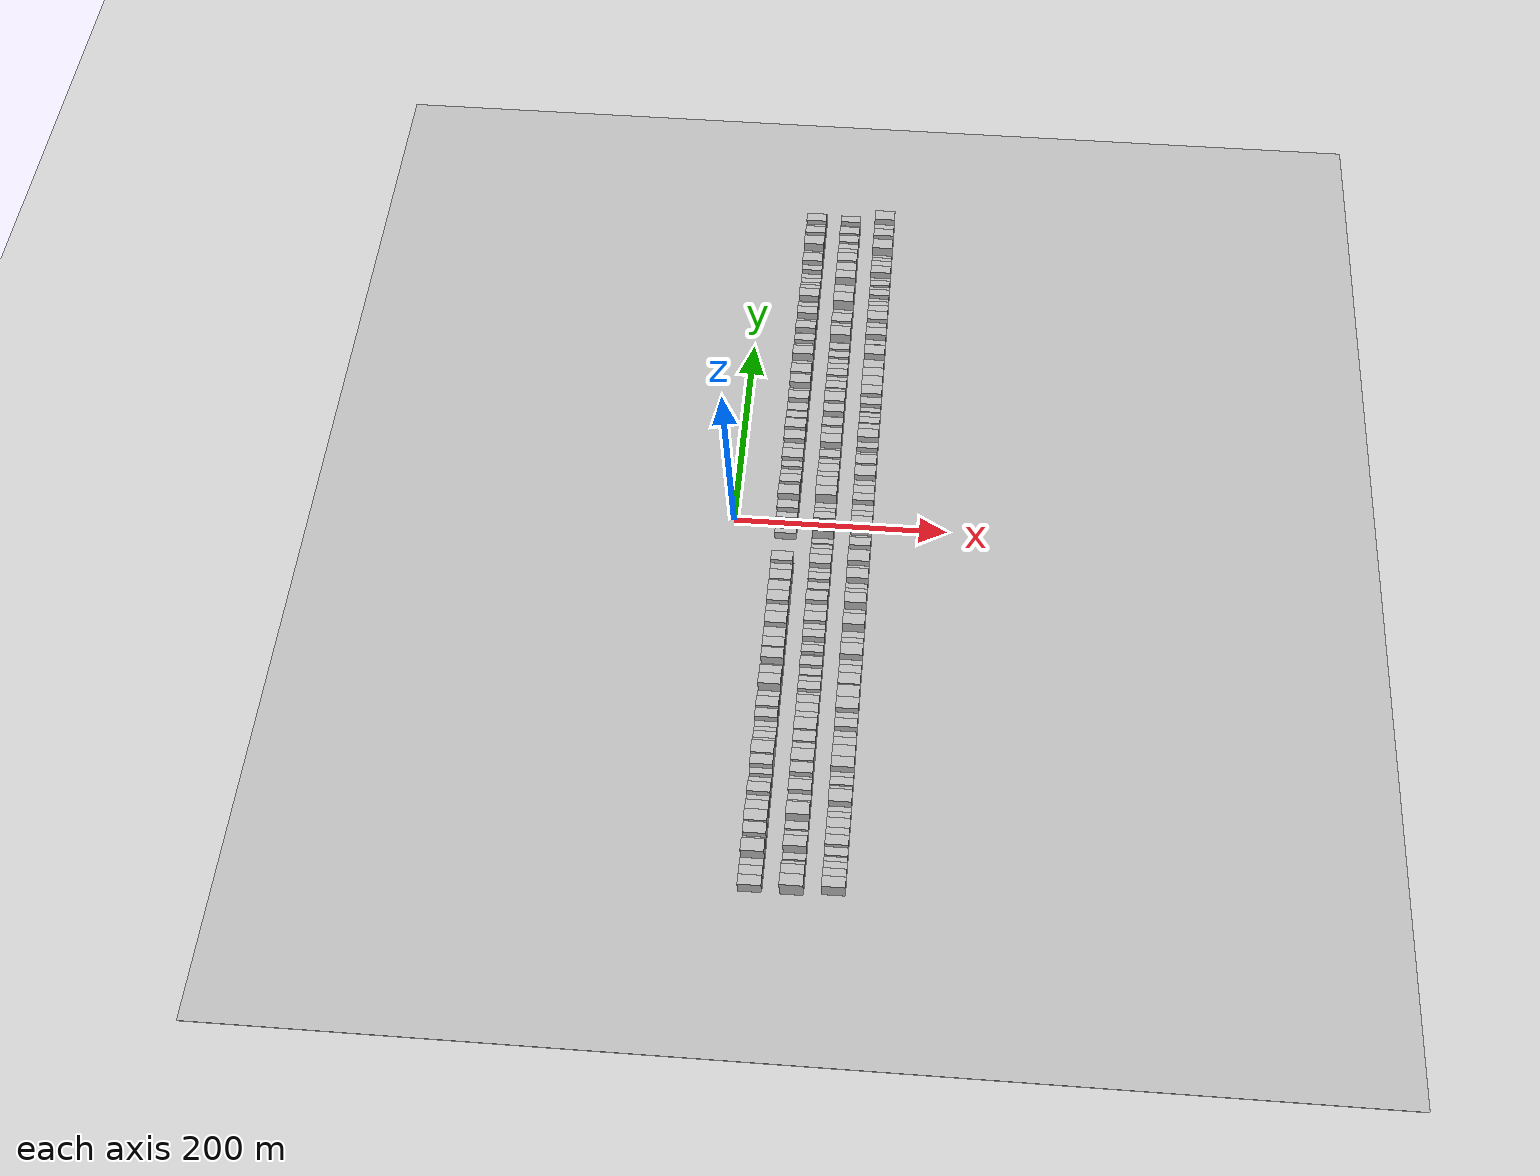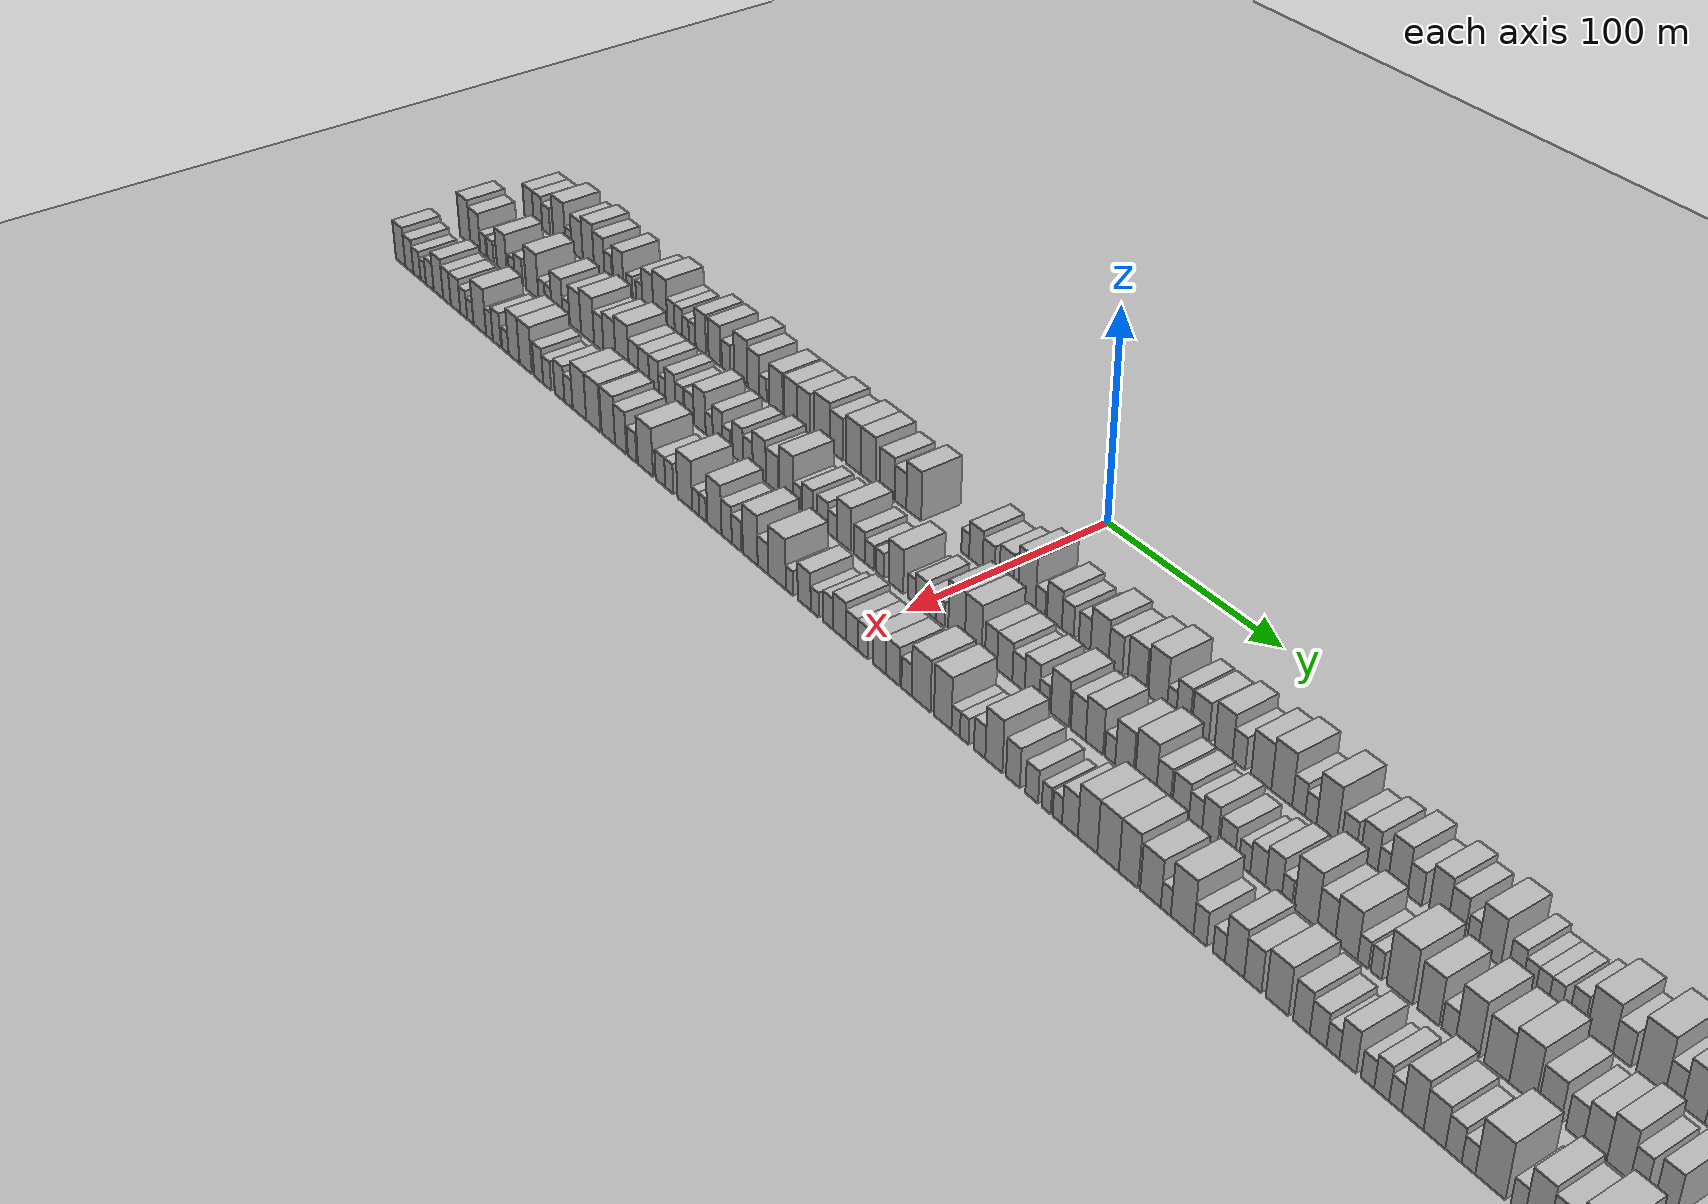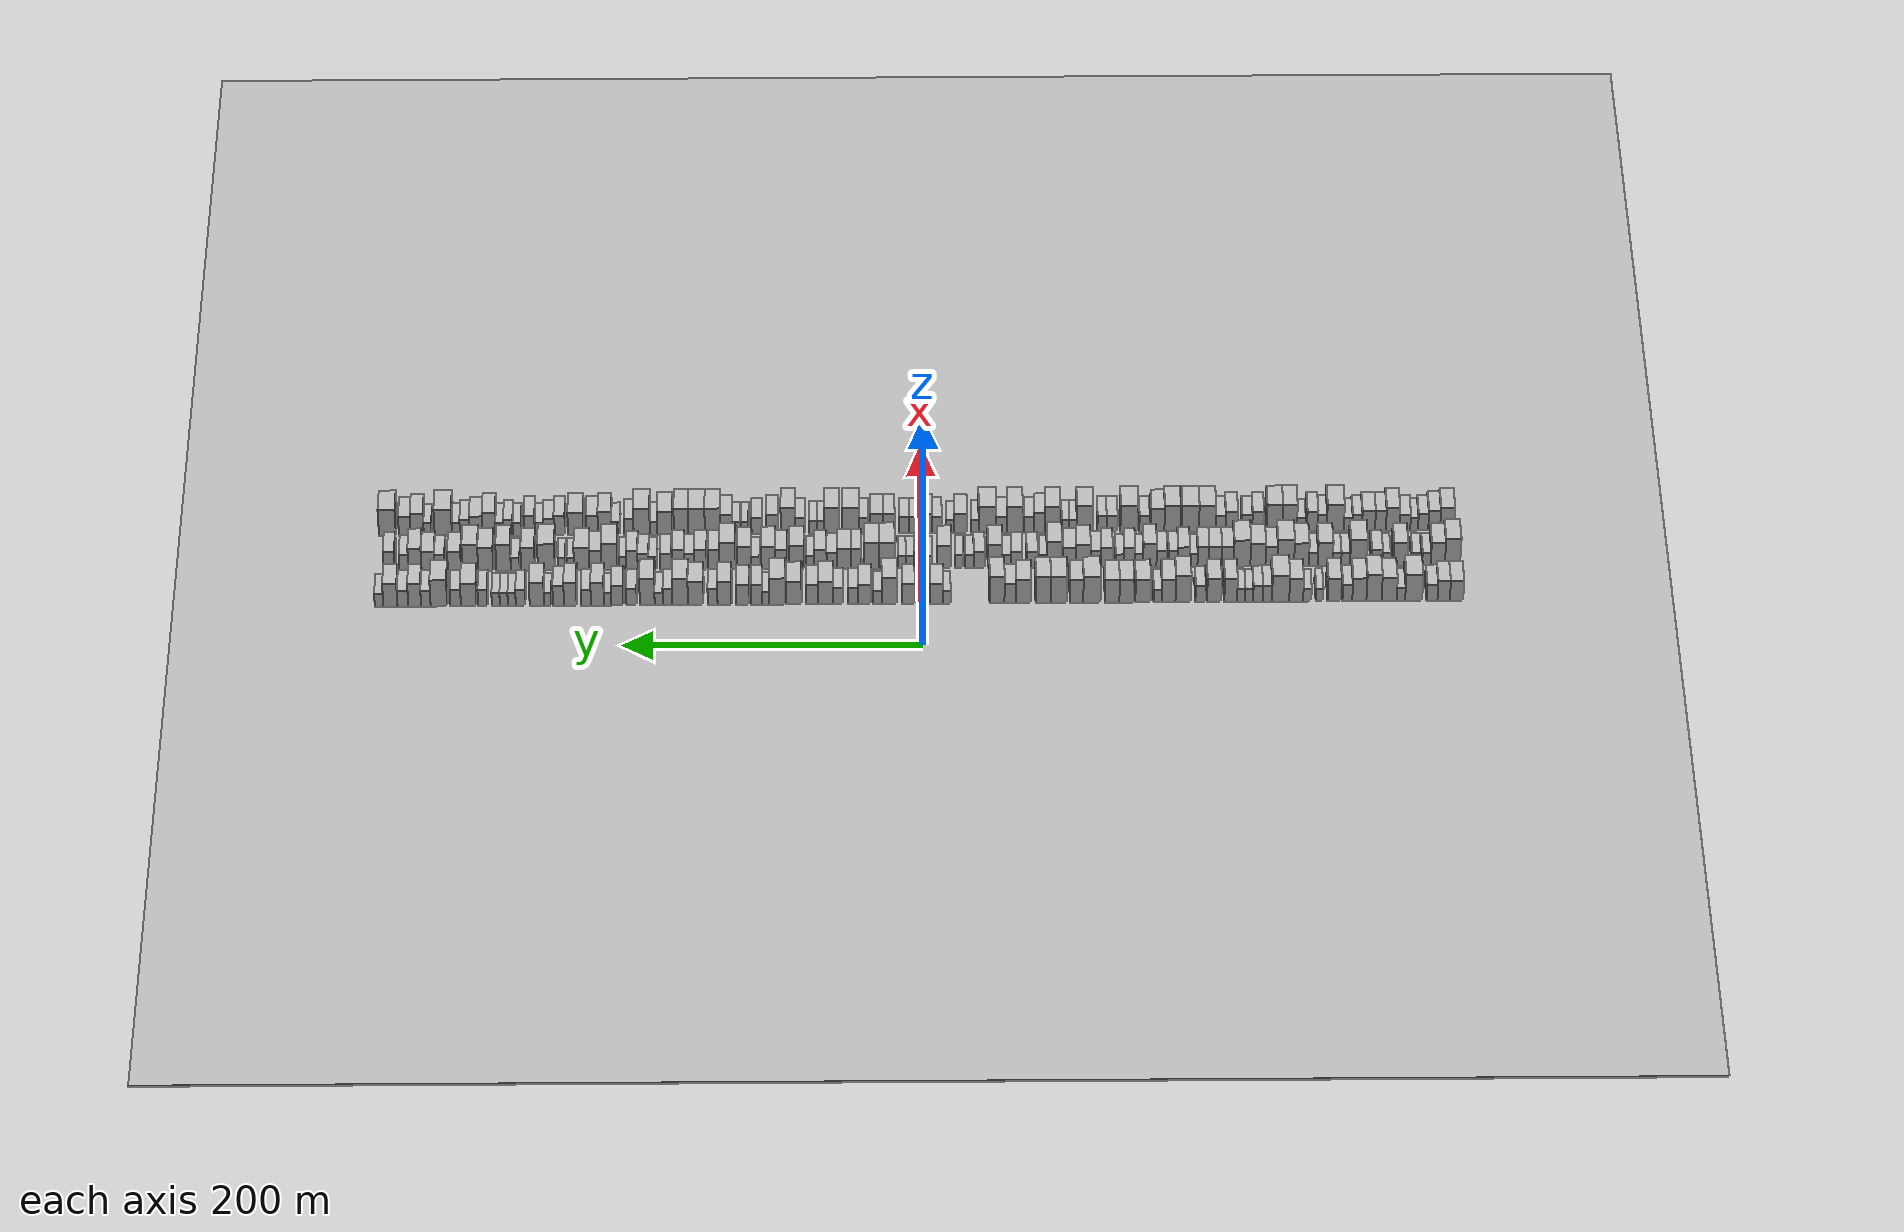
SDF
<?xml version="1.0" encoding="utf-8"?>

<sdf version="1.6">

   <world name="default">

      <gui fullscreen="0">

         <camera name="user_camera">

            <pose>-15 0 4.57585 0 0 0</pose>

            <view_controller>orbit</view_controller>

         </camera>

      </gui>

      <scene>

         <sky>

           <clouds>

             <speed>12</speed>

           </clouds>

         </sky>

         <ambient>0.4 0.4 0.4 1</ambient>

         <background>0.7 0.7 0.7 1</background>

         <shadows>1</shadows>

      </scene>

      <gravity>0 0 -9.8066</gravity>

      <magnetic_field>6e-06 2.3e-05 -4.2e-05</magnetic_field>

      <physics default="0" name="default_physics" type="ode">

         <ode>

            <solver>

               <type>quick</type>

               <iters>10</iters>

               <sor>1.0</sor>

               <use_dynamic_moi_rescaling>0</use_dynamic_moi_rescaling>

            </solver>

            <constraints>

               <cfm>0</cfm>

               <erp>0.2</erp>

               <contact_max_correcting_vel>100</contact_max_correcting_vel>

               <contact_surface_layer>0.001</contact_surface_layer>

            </constraints>

         </ode>

         <max_step_size>0.004</max_step_size>

         <real_time_factor>1</real_time_factor>

         <real_time_update_rate>250</real_time_update_rate>

      </physics>

      <light name="sun" type="directional">

         <cast_shadows>1</cast_shadows>

         <pose>0 0 10 0 0 0</pose>

         <diffuse>0.8 0.8 0.8 1</diffuse>

         <specular>0.2 0.2 0.2 1</specular>

         <attenuation>

            <range>1000</range>

            <constant>0.9</constant>

            <linear>0.01</linear>

            <quadratic>0.001</quadratic>

         </attenuation>

         <direction>-0.5 0.1 -0.9</direction>

      </light>

      <include>

         <name>ground_plane_1</name>

         <uri>model://HANNAS_ground_plane</uri>

         <pose>0 0 0  0 0 0</pose>

      </include>

      <include>

         <name>ground_plane_2</name>

         <uri>model://HANNAS_ground_plane</uri>

         <pose>100 0 0  0 0 0</pose>

      </include>

      <model name="building_1">

         <static>1</static>

         <pose frame="">50.0000 -355.5543 0 0.000000 0.000000 0.000000</pose>

         <link name="link">

            <pose frame="">0 0 9.00 0 0 0</pose>

            <collision name="collision">

               <geometry>

                  <box>

                     <size>20.0000 8.8914 18.0000</size>

                  </box>

               </geometry>

               <max_contacts>10</max_contacts>

               <surface>

                  <contact>

                     <ode/>

                  </contact>

                  <bounce/>

                  <friction>

                     <torsional>

                        <ode/>

                     </torsional>

                     <ode/>

                  </friction>

               </surface>

            </collision>

            <visual name="visual">

               <cast_shadows>0</cast_shadows>

               <geometry>

                  <box>

                     <size>20.0000 8.8914 18.0000</size>

                  </box>

               </geometry>

               <material>

                  <script>

                     <uri>model://HANNAS_wall/materials/scripts</uri>

                     <uri>model://HANNAS_wall/materials/textures</uri>

                     <name>vrc/HANNAS_wall</name>

                  </script>

               </material>

            </visual>

            <self_collide>0</self_collide>

            <enable_wind>0</enable_wind>

            <kinematic>0</kinematic>

         </link>

      </model>

      <model name="building_2">

         <static>1</static>

         <pose frame="">50.0000 -346.9691 0 0.000000 0.000000 0.000000</pose>

         <link name="link">

            <pose frame="">0 0 9.00 0 0 0</pose>

            <collision name="collision">

               <geometry>

                  <box>

                     <size>20.0000 8.2791 18.0000</size>

                  </box>

               </geometry>

               <max_contacts>10</max_contacts>

               <surface>

                  <contact>

                     <ode/>

                  </contact>

                  <bounce/>

                  <friction>

                     <torsional>

                        <ode/>

                     </torsional>

                     <ode/>

                  </friction>

               </surface>

            </collision>

            <visual name="visual">

               <cast_shadows>0</cast_shadows>

               <geometry>

                  <box>

                     <size>20.0000 8.2791 18.0000</size>

                  </box>

               </geometry>

               <material>

                  <script>

                     <uri>model://HANNAS_wall/materials/scripts</uri>

                     <uri>model://HANNAS_wall/materials/textures</uri>

                     <name>vrc/HANNAS_wall</name>

                  </script>

               </material>

            </visual>

            <self_collide>0</self_collide>

            <enable_wind>0</enable_wind>

            <kinematic>0</kinematic>

         </link>

      </model>

      <model name="building_3">

         <static>1</static>

         <pose frame="">50.0000 -339.2189 0 0.000000 0.000000 0.000000</pose>

         <link name="link">

            <pose frame="">0 0 7.50 0 0 0</pose>

            <collision name="collision">

               <geometry>

                  <box>

                     <size>20.0000 7.2212 15.0000</size>

                  </box>

               </geometry>

               <max_contacts>10</max_contacts>

               <surface>

                  <contact>

                     <ode/>

                  </contact>

                  <bounce/>

                  <friction>

                     <torsional>

                        <ode/>

                     </torsional>

                     <ode/>

                  </friction>

               </surface>

            </collision>

            <visual name="visual">

               <cast_shadows>0</cast_shadows>

               <geometry>

                  <box>

                     <size>20.0000 7.2212 15.0000</size>

                  </box>

               </geometry>

               <material>

                  <script>

                     <uri>model://HANNAS_wall/materials/scripts</uri>

                     <uri>model://HANNAS_wall/materials/textures</uri>

                     <name>vrc/HANNAS_wall</name>

                  </script>

               </material>

            </visual>

            <self_collide>0</self_collide>

            <enable_wind>0</enable_wind>

            <kinematic>0</kinematic>

         </link>

      </model>

      <model name="building_4">

         <static>1</static>

         <pose frame="">50.0000 -326.9329 0 0.000000 0.000000 0.000000</pose>

         <link name="link">

            <pose frame="">0 0 12.00 0 0 0</pose>

            <collision name="collision">

               <geometry>

                  <box>

                     <size>20.0000 11.3509 24.0000</size>

                  </box>

               </geometry>

               <max_contacts>10</max_contacts>

               <surface>

                  <contact>

                     <ode/>

                  </contact>

                  <bounce/>

                  <friction>

                     <torsional>

                        <ode/>

                     </torsional>

                     <ode/>

                  </friction>

               </surface>

            </collision>

            <visual name="visual">

               <cast_shadows>0</cast_shadows>

               <geometry>

                  <box>

                     <size>20.0000 11.3509 24.0000</size>

                  </box>

               </geometry>

               <material>

                  <script>

                     <uri>model://HANNAS_wall/materials/scripts</uri>

                     <uri>model://HANNAS_wall/materials/textures</uri>

                     <name>vrc/HANNAS_wall</name>

                  </script>

               </material>

            </visual>

            <self_collide>0</self_collide>

            <enable_wind>0</enable_wind>

            <kinematic>0</kinematic>

         </link>

      </model>

      <model name="building_5">

         <static>1</static>

         <pose frame="">50.0000 -318.4150 0 0.000000 0.000000 0.000000</pose>

         <link name="link">

            <pose frame="">0 0 6.00 0 0 0</pose>

            <collision name="collision">

               <geometry>

                  <box>

                     <size>20.0000 5.6850 12.0000</size>

                  </box>

               </geometry>

               <max_contacts>10</max_contacts>

               <surface>

                  <contact>

                     <ode/>

                  </contact>

                  <bounce/>

                  <friction>

                     <torsional>

                        <ode/>

                     </torsional>

                     <ode/>

                  </friction>

               </surface>

            </collision>

            <visual name="visual">

               <cast_shadows>0</cast_shadows>

               <geometry>

                  <box>

                     <size>20.0000 5.6850 12.0000</size>

                  </box>

               </geometry>

               <material>

                  <script>

                     <uri>model://HANNAS_wall/materials/scripts</uri>

                     <uri>model://HANNAS_wall/materials/textures</uri>

                     <name>vrc/HANNAS_wall</name>

                  </script>

               </material>

            </visual>

            <self_collide>0</self_collide>

            <enable_wind>0</enable_wind>

            <kinematic>0</kinematic>

         </link>

      </model>

      <model name="building_6">

         <static>1</static>

         <pose frame="">50.0000 -310.5477 0 0.000000 0.000000 0.000000</pose>

         <link name="link">

            <pose frame="">0 0 10.50 0 0 0</pose>

            <collision name="collision">

               <geometry>

                  <box>

                     <size>20.0000 10.0495 21.0000</size>

                  </box>

               </geometry>

               <max_contacts>10</max_contacts>

               <surface>

                  <contact>

                     <ode/>

                  </contact>

                  <bounce/>

                  <friction>

                     <torsional>

                        <ode/>

                     </torsional>

                     <ode/>

                  </friction>

               </surface>

            </collision>

            <visual name="visual">

               <cast_shadows>0</cast_shadows>

               <geometry>

                  <box>

                     <size>20.0000 10.0495 21.0000</size>

                  </box>

               </geometry>

               <material>

                  <script>

                     <uri>model://HANNAS_wall/materials/scripts</uri>

                     <uri>model://HANNAS_wall/materials/textures</uri>

                     <name>vrc/HANNAS_wall</name>

                  </script>

               </material>

            </visual>

            <self_collide>0</self_collide>

            <enable_wind>0</enable_wind>

            <kinematic>0</kinematic>

         </link>

      </model>

      <model name="building_7">

         <static>1</static>

         <pose frame="">50.0000 -300.4793 0 0.000000 0.000000 0.000000</pose>

         <link name="link">

            <pose frame="">0 0 12.00 0 0 0</pose>

            <collision name="collision">

               <geometry>

                  <box>

                     <size>20.0000 10.0874 24.0000</size>

                  </box>

               </geometry>

               <max_contacts>10</max_contacts>

               <surface>

                  <contact>

                     <ode/>

                  </contact>

                  <bounce/>

                  <friction>

                     <torsional>

                        <ode/>

                     </torsional>

                     <ode/>

                  </friction>

               </surface>

            </collision>

            <visual name="visual">

               <cast_shadows>0</cast_shadows>

               <geometry>

                  <box>

                     <size>20.0000 10.0874 24.0000</size>

                  </box>

               </geometry>

               <material>

                  <script>

                     <uri>model://HANNAS_wall/materials/scripts</uri>

                     <uri>model://HANNAS_wall/materials/textures</uri>

                     <name>vrc/HANNAS_wall</name>

                  </script>

               </material>

            </visual>

            <self_collide>0</self_collide>

            <enable_wind>0</enable_wind>

            <kinematic>0</kinematic>

         </link>

      </model>

      <model name="building_8">

         <static>1</static>

         <pose frame="">50.0000 -290.7188 0 0.000000 0.000000 0.000000</pose>

         <link name="link">

            <pose frame="">0 0 10.50 0 0 0</pose>

            <collision name="collision">

               <geometry>

                  <box>

                     <size>20.0000 9.4337 21.0000</size>

                  </box>

               </geometry>

               <max_contacts>10</max_contacts>

               <surface>

                  <contact>

                     <ode/>

                  </contact>

                  <bounce/>

                  <friction>

                     <torsional>

                        <ode/>

                     </torsional>

                     <ode/>

                  </friction>

               </surface>

            </collision>

            <visual name="visual">

               <cast_shadows>0</cast_shadows>

               <geometry>

                  <box>

                     <size>20.0000 9.4337 21.0000</size>

                  </box>

               </geometry>

               <material>

                  <script>

                     <uri>model://HANNAS_wall/materials/scripts</uri>

                     <uri>model://HANNAS_wall/materials/textures</uri>

                     <name>vrc/HANNAS_wall</name>

                  </script>

               </material>

            </visual>

            <self_collide>0</self_collide>

            <enable_wind>0</enable_wind>

            <kinematic>0</kinematic>

         </link>

      </model>

      <model name="building_9">

         <static>1</static>

         <pose frame="">50.0000 -282.7231 0 0.000000 0.000000 0.000000</pose>

         <link name="link">

            <pose frame="">0 0 7.50 0 0 0</pose>

            <collision name="collision">

               <geometry>

                  <box>

                     <size>20.0000 6.5577 15.0000</size>

                  </box>

               </geometry>

               <max_contacts>10</max_contacts>

               <surface>

                  <contact>

                     <ode/>

                  </contact>

                  <bounce/>

                  <friction>

                     <torsional>

                        <ode/>

                     </torsional>

                     <ode/>

                  </friction>

               </surface>

            </collision>

            <visual name="visual">

               <cast_shadows>0</cast_shadows>

               <geometry>

                  <box>

                     <size>20.0000 6.5577 15.0000</size>

                  </box>

               </geometry>

               <material>

                  <script>

                     <uri>model://HANNAS_wall/materials/scripts</uri>

                     <uri>model://HANNAS_wall/materials/textures</uri>

                     <name>vrc/HANNAS_wall</name>

                  </script>

               </material>

            </visual>

            <self_collide>0</self_collide>

            <enable_wind>0</enable_wind>

            <kinematic>0</kinematic>

         </link>

      </model>

      <model name="building_10">

         <static>1</static>

         <pose frame="">50.0000 -273.9683 0 0.000000 0.000000 0.000000</pose>

         <link name="link">

            <pose frame="">0 0 10.50 0 0 0</pose>

            <collision name="collision">

               <geometry>

                  <box>

                     <size>20.0000 8.9520 21.0000</size>

                  </box>

               </geometry>

               <max_contacts>10</max_contacts>

               <surface>

                  <contact>

                     <ode/>

                  </contact>

                  <bounce/>

                  <friction>

                     <torsional>

                        <ode/>

                     </torsional>

                     <ode/>

                  </friction>

               </surface>

            </collision>

            <visual name="visual">

               <cast_shadows>0</cast_shadows>

               <geometry>

                  <box>

                     <size>20.0000 8.9520 21.0000</size>

                  </box>

               </geometry>

               <material>

                  <script>

                     <uri>model://HANNAS_wall/materials/scripts</uri>

                     <uri>model://HANNAS_wall/materials/textures</uri>

                     <name>vrc/HANNAS_wall</name>

                  </script>

               </material>

            </visual>

            <self_collide>0</self_collide>

            <enable_wind>0</enable_wind>

            <kinematic>0</kinematic>

         </link>

      </model>

      <model name="building_11">

         <static>1</static>

         <pose frame="">50.0000 -264.0726 0 0.000000 0.000000 0.000000</pose>

         <link name="link">

            <pose frame="">0 0 6.00 0 0 0</pose>

            <collision name="collision">

               <geometry>

                  <box>

                     <size>20.0000 4.8393 12.0000</size>

                  </box>

               </geometry>

               <max_contacts>10</max_contacts>

               <surface>

                  <contact>

                     <ode/>

                  </contact>

                  <bounce/>

                  <friction>

                     <torsional>

                        <ode/>

                     </torsional>

                     <ode/>

                  </friction>

               </surface>

            </collision>

            <visual name="visual">

               <cast_shadows>0</cast_shadows>

               <geometry>

                  <box>

                     <size>20.0000 4.8393 12.0000</size>

                  </box>

               </geometry>

               <material>

                  <script>

                     <uri>model://HANNAS_wall/materials/scripts</uri>

                     <uri>model://HANNAS_wall/materials/textures</uri>

                     <name>vrc/HANNAS_wall</name>

                  </script>

               </material>

            </visual>

            <self_collide>0</self_collide>

            <enable_wind>0</enable_wind>

            <kinematic>0</kinematic>

         </link>

      </model>

      <model name="building_12">

         <static>1</static>

         <pose frame="">50.0000 -255.9314 0 0.000000 0.000000 0.000000</pose>

         <link name="link">

            <pose frame="">0 0 6.00 0 0 0</pose>

            <collision name="collision">

               <geometry>

                  <box>

                     <size>20.0000 5.4432 12.0000</size>

                  </box>

               </geometry>

               <max_contacts>10</max_contacts>

               <surface>

                  <contact>

                     <ode/>

                  </contact>

                  <bounce/>

                  <friction>

                     <torsional>

                        <ode/>

                     </torsional>

                     <ode/>

                  </friction>

               </surface>

            </collision>

            <visual name="visual">

               <cast_shadows>0</cast_shadows>

               <geometry>

                  <box>

                     <size>20.0000 5.4432 12.0000</size>

                  </box>

               </geometry>

               <material>

                  <script>

                     <uri>model://HANNAS_wall/materials/scripts</uri>

                     <uri>model://HANNAS_wall/materials/textures</uri>

                     <name>vrc/HANNAS_wall</name>

                  </script>

               </material>

            </visual>

            <self_collide>0</self_collide>

            <enable_wind>0</enable_wind>

            <kinematic>0</kinematic>

         </link>

      </model>

      <model name="building_13">

         <static>1</static>

         <pose frame="">50.0000 -248.5627 0 0.000000 0.000000 0.000000</pose>

         <link name="link">

            <pose frame="">0 0 10.50 0 0 0</pose>

            <collision name="collision">

               <geometry>

                  <box>

                     <size>20.0000 9.2942 21.0000</size>

                  </box>

               </geometry>

               <max_contacts>10</max_contacts>

               <surface>

                  <contact>

                     <ode/>

                  </contact>

                  <bounce/>

                  <friction>

                     <torsional>

                        <ode/>

                     </torsional>

                     <ode/>

                  </friction>

               </surface>

            </collision>

            <visual name="visual">

               <cast_shadows>0</cast_shadows>

               <geometry>

                  <box>

                     <size>20.0000 9.2942 21.0000</size>

                  </box>

               </geometry>

               <material>

                  <script>

                     <uri>model://HANNAS_wall/materials/scripts</uri>

                     <uri>model://HANNAS_wall/materials/textures</uri>

                     <name>vrc/HANNAS_wall</name>

                  </script>

               </material>

            </visual>

            <self_collide>0</self_collide>

            <enable_wind>0</enable_wind>

            <kinematic>0</kinematic>

         </link>

      </model>

      <model name="building_14">

         <static>1</static>

         <pose frame="">50.0000 -238.1467 0 0.000000 0.000000 0.000000</pose>

         <link name="link">

            <pose frame="">0 0 12.00 0 0 0</pose>

            <collision name="collision">

               <geometry>

                  <box>

                     <size>20.0000 11.5378 24.0000</size>

                  </box>

               </geometry>

               <max_contacts>10</max_contacts>

               <surface>

                  <contact>

                     <ode/>

                  </contact>

                  <bounce/>

                  <friction>

                     <torsional>

                        <ode/>

                     </torsional>

                     <ode/>

                  </friction>

               </surface>

            </collision>

            <visual name="visual">

               <cast_shadows>0</cast_shadows>

               <geometry>

                  <box>

                     <size>20.0000 11.5378 24.0000</size>

                  </box>

               </geometry>

               <material>

                  <script>

                     <uri>model://HANNAS_wall/materials/scripts</uri>

                     <uri>model://HANNAS_wall/materials/textures</uri>

                     <name>vrc/HANNAS_wall</name>

                  </script>

               </material>

            </visual>

            <self_collide>0</self_collide>

            <enable_wind>0</enable_wind>

            <kinematic>0</kinematic>

         </link>

      </model>

      <model name="building_15">

         <static>1</static>

         <pose frame="">50.0000 -229.2953 0 0.000000 0.000000 0.000000</pose>

         <link name="link">

            <pose frame="">0 0 7.50 0 0 0</pose>

            <collision name="collision">

               <geometry>

                  <box>

                     <size>20.0000 6.1651 15.0000</size>

                  </box>

               </geometry>

               <max_contacts>10</max_contacts>

               <surface>

                  <contact>

                     <ode/>

                  </contact>

                  <bounce/>

                  <friction>

                     <torsional>

                        <ode/>

                     </torsional>

                     <ode/>

                  </friction>

               </surface>

            </collision>

            <visual name="visual">

               <cast_shadows>0</cast_shadows>

               <geometry>

                  <box>

                     <size>20.0000 6.1651 15.0000</size>

                  </box>

               </geometry>

               <material>

                  <script>

                     <uri>model://HANNAS_wall/materials/scripts</uri>

                     <uri>model://HANNAS_wall/materials/textures</uri>

                     <name>vrc/HANNAS_wall</name>

                  </script>

               </material>

            </visual>

            <self_collide>0</self_collide>

            <enable_wind>0</enable_wind>

            <kinematic>0</kinematic>

         </link>

      </model>

      <model name="building_16">

         <static>1</static>

         <pose frame="">50.0000 -223.0267 0 0.000000 0.000000 0.000000</pose>

         <link name="link">

            <pose frame="">0 0 7.50 0 0 0</pose>

            <collision name="collision">

               <geometry>

                  <box>

                     <size>20.0000 6.3720 15.0000</size>

                  </box>

               </geometry>

               <max_contacts>10</max_contacts>

               <surface>

                  <contact>

                     <ode/>

                  </contact>

                  <bounce/>

                  <friction>

                     <torsional>

                        <ode/>

                     </torsional>

                     <ode/>

                  </friction>

               </surface>

            </collision>

            <visual name="visual">

               <cast_shadows>0</cast_shadows>

               <geometry>

                  <box>

                     <size>20.0000 6.3720 15.0000</size>

                  </box>

               </geometry>

               <material>

                  <script>

                     <uri>model://HANNAS_wall/materials/scripts</uri>

                     <uri>model://HANNAS_wall/materials/textures</uri>

                     <name>vrc/HANNAS_wall</name>

                  </script>

               </material>

            </visual>

            <self_collide>0</self_collide>

            <enable_wind>0</enable_wind>

            <kinematic>0</kinematic>

         </link>

      </model>

      <model name="building_17">

         <static>1</static>

         <pose frame="">50.0000 -217.1712 0 0.000000 0.000000 0.000000</pose>

         <link name="link">

            <pose frame="">0 0 6.00 0 0 0</pose>

            <collision name="collision">

               <geometry>

                  <box>

                     <size>20.0000 5.3390 12.0000</size>

                  </box>

               </geometry>

               <max_contacts>10</max_contacts>

               <surface>

                  <contact>

                     <ode/>

                  </contact>

                  <bounce/>

                  <friction>

                     <torsional>

                        <ode/>

                     </torsional>

                     <ode/>

                  </friction>

               </surface>

            </collision>

            <visual name="visual">

               <cast_shadows>0</cast_shadows>

               <geometry>

                  <box>

                     <size>20.0000 5.3390 12.0000</size>

                  </box>

               </geometry>

               <material>

                  <script>

                     <uri>model://HANNAS_wall/materials/scripts</uri>

                     <uri>model://HANNAS_wall/materials/textures</uri>

                     <name>vrc/HANNAS_wall</name>

                  </script>

               </material>

            </visual>

            <self_collide>0</self_collide>

            <enable_wind>0</enable_wind>

            <kinematic>0</kinematic>

         </link>

      </model>

      <model name="building_18">

         <static>1</static>

         <pose frame="">50.0000 -211.8315 0 0.000000 0.000000 0.000000</pose>

         <link name="link">

            <pose frame="">0 0 6.00 0 0 0</pose>

            <collision name="collision">

               <geometry>

                  <box>

                     <size>20.0000 5.3403 12.0000</size>

                  </box>

               </geometry>

               <max_contacts>10</max_contacts>

               <surface>

                  <contact>

                     <ode/>

                  </contact>

                  <bounce/>

                  <friction>

                     <torsional>

                        <ode/>

                     </torsional>

                     <ode/>

                  </friction>

               </surface>

            </collision>

            <visual name="visual">

               <cast_shadows>0</cast_shadows>

               <geometry>

                  <box>

                     <size>20.0000 5.3403 12.0000</size>

                  </box>

               </geometry>

               <material>

                  <script>

                     <uri>model://HANNAS_wall/materials/scripts</uri>

                     <uri>model://HANNAS_wall/materials/textures</uri>

                     <name>vrc/HANNAS_wall</name>

                  </script>

               </material>

            </visual>

            <self_collide>0</self_collide>

            <enable_wind>0</enable_wind>

            <kinematic>0</kinematic>

         </link>

      </model>

      <model name="building_19">

         <static>1</static>

         <pose frame="">50.0000 -204.9044 0 0.000000 0.000000 0.000000</pose>

         <link name="link">

            <pose frame="">0 0 10.50 0 0 0</pose>

            <collision name="collision">

               <geometry>

                  <box>

                     <size>20.0000 8.5139 21.0000</size>

                  </box>

               </geometry>

               <max_contacts>10</max_contacts>

               <surface>

                  <contact>

                     <ode/>

                  </contact>

                  <bounce/>

                  <friction>

                     <torsional>

                        <ode/>

                     </torsional>

                     <ode/>

                  </friction>

               </surface>

            </collision>

            <visual name="visual">

               <cast_shadows>0</cast_shadows>

               <geometry>

                  <box>

                     <size>20.0000 8.5139 21.0000</size>

                  </box>

               </geometry>

               <material>

                  <script>

                     <uri>model://HANNAS_wall/materials/scripts</uri>

                     <uri>model://HANNAS_wall/materials/textures</uri>

                     <name>vrc/HANNAS_wall</name>

                  </script>

               </material>

            </visual>

            <self_collide>0</self_collide>

            <enable_wind>0</enable_wind>

            <kinematic>0</kinematic>

         </link>

      </model>

      <model name="building_20">

         <static>1</static>

         <pose frame="">50.0000 -193.8881 0 0.000000 0.000000 0.000000</pose>

         <link name="link">

            <pose frame="">0 0 10.50 0 0 0</pose>

            <collision name="collision">

               <geometry>

                  <box>

                     <size>20.0000 9.5186 21.0000</size>

                  </box>

               </geometry>

               <max_contacts>10</max_contacts>

               <surface>

                  <contact>

                     <ode/>

                  </contact>

                  <bounce/>

                  <friction>

                     <torsional>

                        <ode/>

                     </torsional>

                     <ode/>

                  </friction>

               </surface>

            </collision>

            <visual name="visual">

               <cast_shadows>0</cast_shadows>

               <geometry>

                  <box>

                     <size>20.0000 9.5186 21.0000</size>

                  </box>

               </geometry>

               <material>

                  <script>

                     <uri>model://HANNAS_wall/materials/scripts</uri>

                     <uri>model://HANNAS_wall/materials/textures</uri>

                     <name>vrc/HANNAS_wall</name>

                  </script>

               </material>

            </visual>

            <self_collide>0</self_collide>

            <enable_wind>0</enable_wind>

            <kinematic>0</kinematic>

         </link>

      </model>

      <model name="building_21">

         <static>1</static>

         <pose frame="">50.0000 -184.7525 0 0.000000 0.000000 0.000000</pose>

         <link name="link">

            <pose frame="">0 0 7.50 0 0 0</pose>

            <collision name="collision">

               <geometry>

                  <box>

                     <size>20.0000 6.7527 15.0000</size>

                  </box>

               </geometry>

               <max_contacts>10</max_contacts>

               <surface>

                  <contact>

                     <ode/>

                  </contact>

                  <bounce/>

                  <friction>

                     <torsional>

                        <ode/>

                     </torsional>

                     <ode/>

                  </friction>

               </surface>

            </collision>

            <visual name="visual">

               <cast_shadows>0</cast_shadows>

               <geometry>

                  <box>

                     <size>20.0000 6.7527 15.0000</size>

                  </box>

               </geometry>

               <material>

                  <script>

                     <uri>model://HANNAS_wall/materials/scripts</uri>

                     <uri>model://HANNAS_wall/materials/textures</uri>

                     <name>vrc/HANNAS_wall</name>

                  </script>

               </material>

            </visual>

            <self_collide>0</self_collide>

            <enable_wind>0</enable_wind>

            <kinematic>0</kinematic>

         </link>

      </model>

      <model name="building_22">

         <static>1</static>

         <pose frame="">50.0000 -173.2291 0 0.000000 0.000000 0.000000</pose>

         <link name="link">

            <pose frame="">0 0 12.00 0 0 0</pose>

            <collision name="collision">

               <geometry>

                  <box>

                     <size>20.0000 10.2941 24.0000</size>

                  </box>

               </geometry>

               <max_contacts>10</max_contacts>

               <surface>

                  <contact>

                     <ode/>

                  </contact>

                  <bounce/>

                  <friction>

                     <torsional>

                        <ode/>

                     </torsional>

                     <ode/>

                  </friction>

               </surface>

            </collision>

            <visual name="visual">

               <cast_shadows>0</cast_shadows>

               <geometry>

                  <box>

                     <size>20.0000 10.2941 24.0000</size>

                  </box>

               </geometry>

               <material>

                  <script>

                     <uri>model://HANNAS_wall/materials/scripts</uri>

                     <uri>model://HANNAS_wall/materials/textures</uri>

                     <name>vrc/HANNAS_wall</name>

                  </script>

               </material>

            </visual>

            <self_collide>0</self_collide>

            <enable_wind>0</enable_wind>

            <kinematic>0</kinematic>

         </link>

      </model>

      <model name="building_23">

         <static>1</static>

         <pose frame="">50.0000 -163.5071 0 0.000000 0.000000 0.000000</pose>

         <link name="link">

            <pose frame="">0 0 10.50 0 0 0</pose>

            <collision name="collision">

               <geometry>

                  <box>

                     <size>20.0000 9.1499 21.0000</size>

                  </box>

               </geometry>

               <max_contacts>10</max_contacts>

               <surface>

                  <contact>

                     <ode/>

                  </contact>

                  <bounce/>

                  <friction>

                     <torsional>

                        <ode/>

                     </torsional>

                     <ode/>

                  </friction>

               </surface>

            </collision>

            <visual name="visual">

               <cast_shadows>0</cast_shadows>

               <geometry>

                  <box>

                     <size>20.0000 9.1499 21.0000</size>

                  </box>

               </geometry>

               <material>

                  <script>

                     <uri>model://HANNAS_wall/materials/scripts</uri>

                     <uri>model://HANNAS_wall/materials/textures</uri>

                     <name>vrc/HANNAS_wall</name>

                  </script>

               </material>

            </visual>

            <self_collide>0</self_collide>

            <enable_wind>0</enable_wind>

            <kinematic>0</kinematic>

         </link>

      </model>

      <model name="building_24">

         <static>1</static>

         <pose frame="">50.0000 -156.1976 0 0.000000 0.000000 0.000000</pose>

         <link name="link">

            <pose frame="">0 0 6.00 0 0 0</pose>

            <collision name="collision">

               <geometry>

                  <box>

                     <size>20.0000 5.4691 12.0000</size>

                  </box>

               </geometry>

               <max_contacts>10</max_contacts>

               <surface>

                  <contact>

                     <ode/>

                  </contact>

                  <bounce/>

                  <friction>

                     <torsional>

                        <ode/>

                     </torsional>

                     <ode/>

                  </friction>

               </surface>

            </collision>

            <visual name="visual">

               <cast_shadows>0</cast_shadows>

               <geometry>

                  <box>

                     <size>20.0000 5.4691 12.0000</size>

                  </box>

               </geometry>

               <material>

                  <script>

                     <uri>model://HANNAS_wall/materials/scripts</uri>

                     <uri>model://HANNAS_wall/materials/textures</uri>

                     <name>vrc/HANNAS_wall</name>

                  </script>

               </material>

            </visual>

            <self_collide>0</self_collide>

            <enable_wind>0</enable_wind>

            <kinematic>0</kinematic>

         </link>

      </model>

      <model name="building_25">

         <static>1</static>

         <pose frame="">50.0000 -146.3815 0 0.000000 0.000000 0.000000</pose>

         <link name="link">

            <pose frame="">0 0 10.50 0 0 0</pose>

            <collision name="collision">

               <geometry>

                  <box>

                     <size>20.0000 10.1630 21.0000</size>

                  </box>

               </geometry>

               <max_contacts>10</max_contacts>

               <surface>

                  <contact>

                     <ode/>

                  </contact>

                  <bounce/>

                  <friction>

                     <torsional>

                        <ode/>

                     </torsional>

                     <ode/>

                  </friction>

               </surface>

            </collision>

            <visual name="visual">

               <cast_shadows>0</cast_shadows>

               <geometry>

                  <box>

                     <size>20.0000 10.1630 21.0000</size>

                  </box>

               </geometry>

               <material>

                  <script>

                     <uri>model://HANNAS_wall/materials/scripts</uri>

                     <uri>model://HANNAS_wall/materials/textures</uri>

                     <name>vrc/HANNAS_wall</name>

                  </script>

               </material>

            </visual>

            <self_collide>0</self_collide>

            <enable_wind>0</enable_wind>

            <kinematic>0</kinematic>

         </link>

      </model>

      <model name="building_26">

         <static>1</static>

         <pose frame="">50.0000 -135.4872 0 0.000000 0.000000 0.000000</pose>

         <link name="link">

            <pose frame="">0 0 10.50 0 0 0</pose>

            <collision name="collision">

               <geometry>

                  <box>

                     <size>20.0000 9.6257 21.0000</size>

                  </box>

               </geometry>

               <max_contacts>10</max_contacts>

               <surface>

                  <contact>

                     <ode/>

                  </contact>

                  <bounce/>

                  <friction>

                     <torsional>

                        <ode/>

                     </torsional>

                     <ode/>

                  </friction>

               </surface>

            </collision>

            <visual name="visual">

               <cast_shadows>0</cast_shadows>

               <geometry>

                  <box>

                     <size>20.0000 9.6257 21.0000</size>

                  </box>

               </geometry>

               <material>

                  <script>

                     <uri>model://HANNAS_wall/materials/scripts</uri>

                     <uri>model://HANNAS_wall/materials/textures</uri>

                     <name>vrc/HANNAS_wall</name>

                  </script>

               </material>

            </visual>

            <self_collide>0</self_collide>

            <enable_wind>0</enable_wind>

            <kinematic>0</kinematic>

         </link>

      </model>

      <model name="building_27">

         <static>1</static>

         <pose frame="">50.0000 -125.8723 0 0.000000 0.000000 0.000000</pose>

         <link name="link">

            <pose frame="">0 0 10.50 0 0 0</pose>

            <collision name="collision">

               <geometry>

                  <box>

                     <size>20.0000 9.6040 21.0000</size>

                  </box>

               </geometry>

               <max_contacts>10</max_contacts>

               <surface>

                  <contact>

                     <ode/>

                  </contact>

                  <bounce/>

                  <friction>

                     <torsional>

                        <ode/>

                     </torsional>

                     <ode/>

                  </friction>

               </surface>

            </collision>

            <visual name="visual">

               <cast_shadows>0</cast_shadows>

               <geometry>

                  <box>

                     <size>20.0000 9.6040 21.0000</size>

                  </box>

               </geometry>

               <material>

                  <script>

                     <uri>model://HANNAS_wall/materials/scripts</uri>

                     <uri>model://HANNAS_wall/materials/textures</uri>

                     <name>vrc/HANNAS_wall</name>

                  </script>

               </material>

            </visual>

            <self_collide>0</self_collide>

            <enable_wind>0</enable_wind>

            <kinematic>0</kinematic>

         </link>

      </model>

      <model name="building_28">

         <static>1</static>

         <pose frame="">50.0000 -112.3370 0 0.000000 0.000000 0.000000</pose>

         <link name="link">

            <pose frame="">0 0 12.00 0 0 0</pose>

            <collision name="collision">

               <geometry>

                  <box>

                     <size>20.0000 11.4666 24.0000</size>

                  </box>

               </geometry>

               <max_contacts>10</max_contacts>

               <surface>

                  <contact>

                     <ode/>

                  </contact>

                  <bounce/>

                  <friction>

                     <torsional>

                        <ode/>

                     </torsional>

                     <ode/>

                  </friction>

               </surface>

            </collision>

            <visual name="visual">

               <cast_shadows>0</cast_shadows>

               <geometry>

                  <box>

                     <size>20.0000 11.4666 24.0000</size>

                  </box>

               </geometry>

               <material>

                  <script>

                     <uri>model://HANNAS_wall/materials/scripts</uri>

                     <uri>model://HANNAS_wall/materials/textures</uri>

                     <name>vrc/HANNAS_wall</name>

                  </script>

               </material>

            </visual>

            <self_collide>0</self_collide>

            <enable_wind>0</enable_wind>

            <kinematic>0</kinematic>

         </link>

      </model>

      <model name="building_29">

         <static>1</static>

         <pose frame="">50.0000 -102.1314 0 0.000000 0.000000 0.000000</pose>

         <link name="link">

            <pose frame="">0 0 10.50 0 0 0</pose>

            <collision name="collision">

               <geometry>

                  <box>

                     <size>20.0000 8.9447 21.0000</size>

                  </box>

               </geometry>

               <max_contacts>10</max_contacts>

               <surface>

                  <contact>

                     <ode/>

                  </contact>

                  <bounce/>

                  <friction>

                     <torsional>

                        <ode/>

                     </torsional>

                     <ode/>

                  </friction>

               </surface>

            </collision>

            <visual name="visual">

               <cast_shadows>0</cast_shadows>

               <geometry>

                  <box>

                     <size>20.0000 8.9447 21.0000</size>

                  </box>

               </geometry>

               <material>

                  <script>

                     <uri>model://HANNAS_wall/materials/scripts</uri>

                     <uri>model://HANNAS_wall/materials/textures</uri>

                     <name>vrc/HANNAS_wall</name>

                  </script>

               </material>

            </visual>

            <self_collide>0</self_collide>

            <enable_wind>0</enable_wind>

            <kinematic>0</kinematic>

         </link>

      </model>

      <model name="building_30">

         <static>1</static>

         <pose frame="">50.0000 -90.2336 0 0.000000 0.000000 0.000000</pose>

         <link name="link">

            <pose frame="">0 0 12.00 0 0 0</pose>

            <collision name="collision">

               <geometry>

                  <box>

                     <size>20.0000 10.8509 24.0000</size>

                  </box>

               </geometry>

               <max_contacts>10</max_contacts>

               <surface>

                  <contact>

                     <ode/>

                  </contact>

                  <bounce/>

                  <friction>

                     <torsional>

                        <ode/>

                     </torsional>

                     <ode/>

                  </friction>

               </surface>

            </collision>

            <visual name="visual">

               <cast_shadows>0</cast_shadows>

               <geometry>

                  <box>

                     <size>20.0000 10.8509 24.0000</size>

                  </box>

               </geometry>

               <material>

                  <script>

                     <uri>model://HANNAS_wall/materials/scripts</uri>

                     <uri>model://HANNAS_wall/materials/textures</uri>

                     <name>vrc/HANNAS_wall</name>

                  </script>

               </material>

            </visual>

            <self_collide>0</self_collide>

            <enable_wind>0</enable_wind>

            <kinematic>0</kinematic>

         </link>

      </model>

      <model name="building_31">

         <static>1</static>

         <pose frame="">50.0000 -79.8051 0 0.000000 0.000000 0.000000</pose>

         <link name="link">

            <pose frame="">0 0 12.00 0 0 0</pose>

            <collision name="collision">

               <geometry>

                  <box>

                     <size>20.0000 10.0059 24.0000</size>

                  </box>

               </geometry>

               <max_contacts>10</max_contacts>

               <surface>

                  <contact>

                     <ode/>

                  </contact>

                  <bounce/>

                  <friction>

                     <torsional>

                        <ode/>

                     </torsional>

                     <ode/>

                  </friction>

               </surface>

            </collision>

            <visual name="visual">

               <cast_shadows>0</cast_shadows>

               <geometry>

                  <box>

                     <size>20.0000 10.0059 24.0000</size>

                  </box>

               </geometry>

               <material>

                  <script>

                     <uri>model://HANNAS_wall/materials/scripts</uri>

                     <uri>model://HANNAS_wall/materials/textures</uri>

                     <name>vrc/HANNAS_wall</name>

                  </script>

               </material>

            </visual>

            <self_collide>0</self_collide>

            <enable_wind>0</enable_wind>

            <kinematic>0</kinematic>

         </link>

      </model>

      <model name="building_32">

         <static>1</static>

         <pose frame="">50.0000 -66.7975 0 0.000000 0.000000 0.000000</pose>

         <link name="link">

            <pose frame="">0 0 10.50 0 0 0</pose>

            <collision name="collision">

               <geometry>

                  <box>

                     <size>20.0000 10.0093 21.0000</size>

                  </box>

               </geometry>

               <max_contacts>10</max_contacts>

               <surface>

                  <contact>

                     <ode/>

                  </contact>

                  <bounce/>

                  <friction>

                     <torsional>

                        <ode/>

                     </torsional>

                     <ode/>

                  </friction>

               </surface>

            </collision>

            <visual name="visual">

               <cast_shadows>0</cast_shadows>

               <geometry>

                  <box>

                     <size>20.0000 10.0093 21.0000</size>

                  </box>

               </geometry>

               <material>

                  <script>

                     <uri>model://HANNAS_wall/materials/scripts</uri>

                     <uri>model://HANNAS_wall/materials/textures</uri>

                     <name>vrc/HANNAS_wall</name>

                  </script>

               </material>

            </visual>

            <self_collide>0</self_collide>

            <enable_wind>0</enable_wind>

            <kinematic>0</kinematic>

         </link>

      </model>

      <model name="building_33">

         <static>1</static>

         <pose frame="">50.0000 -57.9215 0 0.000000 0.000000 0.000000</pose>

         <link name="link">

            <pose frame="">0 0 9.00 0 0 0</pose>

            <collision name="collision">

               <geometry>

                  <box>

                     <size>20.0000 7.7427 18.0000</size>

                  </box>

               </geometry>

               <max_contacts>10</max_contacts>

               <surface>

                  <contact>

                     <ode/>

                  </contact>

                  <bounce/>

                  <friction>

                     <torsional>

                        <ode/>

                     </torsional>

                     <ode/>

                  </friction>

               </surface>

            </collision>

            <visual name="visual">

               <cast_shadows>0</cast_shadows>

               <geometry>

                  <box>

                     <size>20.0000 7.7427 18.0000</size>

                  </box>

               </geometry>

               <material>

                  <script>

                     <uri>model://HANNAS_wall/materials/scripts</uri>

                     <uri>model://HANNAS_wall/materials/textures</uri>

                     <name>vrc/HANNAS_wall</name>

                  </script>

               </material>

            </visual>

            <self_collide>0</self_collide>

            <enable_wind>0</enable_wind>

            <kinematic>0</kinematic>

         </link>

      </model>

      <model name="building_34">

         <static>1</static>

         <pose frame="">50.0000 -49.0845 0 0.000000 0.000000 0.000000</pose>

         <link name="link">

            <pose frame="">0 0 12.00 0 0 0</pose>

            <collision name="collision">

               <geometry>

                  <box>

                     <size>20.0000 9.9313 24.0000</size>

                  </box>

               </geometry>

               <max_contacts>10</max_contacts>

               <surface>

                  <contact>

                     <ode/>

                  </contact>

                  <bounce/>

                  <friction>

                     <torsional>

                        <ode/>

                     </torsional>

                     <ode/>

                  </friction>

               </surface>

            </collision>

            <visual name="visual">

               <cast_shadows>0</cast_shadows>

               <geometry>

                  <box>

                     <size>20.0000 9.9313 24.0000</size>

                  </box>

               </geometry>

               <material>

                  <script>

                     <uri>model://HANNAS_wall/materials/scripts</uri>

                     <uri>model://HANNAS_wall/materials/textures</uri>

                     <name>vrc/HANNAS_wall</name>

                  </script>

               </material>

            </visual>

            <self_collide>0</self_collide>

            <enable_wind>0</enable_wind>

            <kinematic>0</kinematic>

         </link>

      </model>

      <model name="building_35">

         <static>1</static>

         <pose frame="">50.0000 -15.6413 0 0.000000 0.000000 0.000000</pose>

         <link name="link">

            <pose frame="">0 0 6.00 0 0 0</pose>

            <collision name="collision">

               <geometry>

                  <box>

                     <size>20.0000 4.9850 12.0000</size>

                  </box>

               </geometry>

               <max_contacts>10</max_contacts>

               <surface>

                  <contact>

                     <ode/>

                  </contact>

                  <bounce/>

                  <friction>

                     <torsional>

                        <ode/>

                     </torsional>

                     <ode/>

                  </friction>

               </surface>

            </collision>

            <visual name="visual">

               <cast_shadows>0</cast_shadows>

               <geometry>

                  <box>

                     <size>20.0000 4.9850 12.0000</size>

                  </box>

               </geometry>

               <material>

                  <script>

                     <uri>model://HANNAS_wall/materials/scripts</uri>

                     <uri>model://HANNAS_wall/materials/textures</uri>

                     <name>vrc/HANNAS_wall</name>

                  </script>

               </material>

            </visual>

            <self_collide>0</self_collide>

            <enable_wind>0</enable_wind>

            <kinematic>0</kinematic>

         </link>

      </model>

      <model name="building_36">

         <static>1</static>

         <pose frame="">50.0000 -8.9011 0 0.000000 0.000000 0.000000</pose>

         <link name="link">

            <pose frame="">0 0 9.00 0 0 0</pose>

            <collision name="collision">

               <geometry>

                  <box>

                     <size>20.0000 8.4952 18.0000</size>

                  </box>

               </geometry>

               <max_contacts>10</max_contacts>

               <surface>

                  <contact>

                     <ode/>

                  </contact>

                  <bounce/>

                  <friction>

                     <torsional>

                        <ode/>

                     </torsional>

                     <ode/>

                  </friction>

               </surface>

            </collision>

            <visual name="visual">

               <cast_shadows>0</cast_shadows>

               <geometry>

                  <box>

                     <size>20.0000 8.4952 18.0000</size>

                  </box>

               </geometry>

               <material>

                  <script>

                     <uri>model://HANNAS_wall/materials/scripts</uri>

                     <uri>model://HANNAS_wall/materials/textures</uri>

                     <name>vrc/HANNAS_wall</name>

                  </script>

               </material>

            </visual>

            <self_collide>0</self_collide>

            <enable_wind>0</enable_wind>

            <kinematic>0</kinematic>

         </link>

      </model>

      <model name="building_37">

         <static>1</static>

         <pose frame="">50.0000 -0.9262 0 0.000000 0.000000 0.000000</pose>

         <link name="link">

            <pose frame="">0 0 7.50 0 0 0</pose>

            <collision name="collision">

               <geometry>

                  <box>

                     <size>20.0000 7.4545 15.0000</size>

                  </box>

               </geometry>

               <max_contacts>10</max_contacts>

               <surface>

                  <contact>

                     <ode/>

                  </contact>

                  <bounce/>

                  <friction>

                     <torsional>

                        <ode/>

                     </torsional>

                     <ode/>

                  </friction>

               </surface>

            </collision>

            <visual name="visual">

               <cast_shadows>0</cast_shadows>

               <geometry>

                  <box>

                     <size>20.0000 7.4545 15.0000</size>

                  </box>

               </geometry>

               <material>

                  <script>

                     <uri>model://HANNAS_wall/materials/scripts</uri>

                     <uri>model://HANNAS_wall/materials/textures</uri>

                     <name>vrc/HANNAS_wall</name>

                  </script>

               </material>

            </visual>

            <self_collide>0</self_collide>

            <enable_wind>0</enable_wind>

            <kinematic>0</kinematic>

         </link>

      </model>

      <model name="building_38">

         <static>1</static>

         <pose frame="">50.0000 10.1009 0 0.000000 0.000000 0.000000</pose>

         <link name="link">

            <pose frame="">0 0 9.00 0 0 0</pose>

            <collision name="collision">

               <geometry>

                  <box>

                     <size>20.0000 8.5998 18.0000</size>

                  </box>

               </geometry>

               <max_contacts>10</max_contacts>

               <surface>

                  <contact>

                     <ode/>

                  </contact>

                  <bounce/>

                  <friction>

                     <torsional>

                        <ode/>

                     </torsional>

                     <ode/>

                  </friction>

               </surface>

            </collision>

            <visual name="visual">

               <cast_shadows>0</cast_shadows>

               <geometry>

                  <box>

                     <size>20.0000 8.5998 18.0000</size>

                  </box>

               </geometry>

               <material>

                  <script>

                     <uri>model://HANNAS_wall/materials/scripts</uri>

                     <uri>model://HANNAS_wall/materials/textures</uri>

                     <name>vrc/HANNAS_wall</name>

                  </script>

               </material>

            </visual>

            <self_collide>0</self_collide>

            <enable_wind>0</enable_wind>

            <kinematic>0</kinematic>

         </link>

      </model>

      <model name="building_39">

         <static>1</static>

         <pose frame="">50.0000 22.5908 0 0.000000 0.000000 0.000000</pose>

         <link name="link">

            <pose frame="">0 0 12.00 0 0 0</pose>

            <collision name="collision">

               <geometry>

                  <box>

                     <size>20.0000 10.3801 24.0000</size>

                  </box>

               </geometry>

               <max_contacts>10</max_contacts>

               <surface>

                  <contact>

                     <ode/>

                  </contact>

                  <bounce/>

                  <friction>

                     <torsional>

                        <ode/>

                     </torsional>

                     <ode/>

                  </friction>

               </surface>

            </collision>

            <visual name="visual">

               <cast_shadows>0</cast_shadows>

               <geometry>

                  <box>

                     <size>20.0000 10.3801 24.0000</size>

                  </box>

               </geometry>

               <material>

                  <script>

                     <uri>model://HANNAS_wall/materials/scripts</uri>

                     <uri>model://HANNAS_wall/materials/textures</uri>

                     <name>vrc/HANNAS_wall</name>

                  </script>

               </material>

            </visual>

            <self_collide>0</self_collide>

            <enable_wind>0</enable_wind>

            <kinematic>0</kinematic>

         </link>

      </model>

      <model name="building_40">

         <static>1</static>

         <pose frame="">50.0000 30.6912 0 0.000000 0.000000 0.000000</pose>

         <link name="link">

            <pose frame="">0 0 6.00 0 0 0</pose>

            <collision name="collision">

               <geometry>

                  <box>

                     <size>20.0000 5.8206 12.0000</size>

                  </box>

               </geometry>

               <max_contacts>10</max_contacts>

               <surface>

                  <contact>

                     <ode/>

                  </contact>

                  <bounce/>

                  <friction>

                     <torsional>

                        <ode/>

                     </torsional>

                     <ode/>

                  </friction>

               </surface>

            </collision>

            <visual name="visual">

               <cast_shadows>0</cast_shadows>

               <geometry>

                  <box>

                     <size>20.0000 5.8206 12.0000</size>

                  </box>

               </geometry>

               <material>

                  <script>

                     <uri>model://HANNAS_wall/materials/scripts</uri>

                     <uri>model://HANNAS_wall/materials/textures</uri>

                     <name>vrc/HANNAS_wall</name>

                  </script>

               </material>

            </visual>

            <self_collide>0</self_collide>

            <enable_wind>0</enable_wind>

            <kinematic>0</kinematic>

         </link>

      </model>

      <model name="building_41">

         <static>1</static>

         <pose frame="">50.0000 39.0023 0 0.000000 0.000000 0.000000</pose>

         <link name="link">

            <pose frame="">0 0 9.00 0 0 0</pose>

            <collision name="collision">

               <geometry>

                  <box>

                     <size>20.0000 8.8015 18.0000</size>

                  </box>

               </geometry>

               <max_contacts>10</max_contacts>

               <surface>

                  <contact>

                     <ode/>

                  </contact>

                  <bounce/>

                  <friction>

                     <torsional>

                        <ode/>

                     </torsional>

                     <ode/>

                  </friction>

               </surface>

            </collision>

            <visual name="visual">

               <cast_shadows>0</cast_shadows>

               <geometry>

                  <box>

                     <size>20.0000 8.8015 18.0000</size>

                  </box>

               </geometry>

               <material>

                  <script>

                     <uri>model://HANNAS_wall/materials/scripts</uri>

                     <uri>model://HANNAS_wall/materials/textures</uri>

                     <name>vrc/HANNAS_wall</name>

                  </script>

               </material>

            </visual>

            <self_collide>0</self_collide>

            <enable_wind>0</enable_wind>

            <kinematic>0</kinematic>

         </link>

      </model>

      <model name="building_42">

         <static>1</static>

         <pose frame="">50.0000 46.8425 0 0.000000 0.000000 0.000000</pose>

         <link name="link">

            <pose frame="">0 0 7.50 0 0 0</pose>

            <collision name="collision">

               <geometry>

                  <box>

                     <size>20.0000 6.8788 15.0000</size>

                  </box>

               </geometry>

               <max_contacts>10</max_contacts>

               <surface>

                  <contact>

                     <ode/>

                  </contact>

                  <bounce/>

                  <friction>

                     <torsional>

                        <ode/>

                     </torsional>

                     <ode/>

                  </friction>

               </surface>

            </collision>

            <visual name="visual">

               <cast_shadows>0</cast_shadows>

               <geometry>

                  <box>

                     <size>20.0000 6.8788 15.0000</size>

                  </box>

               </geometry>

               <material>

                  <script>

                     <uri>model://HANNAS_wall/materials/scripts</uri>

                     <uri>model://HANNAS_wall/materials/textures</uri>

                     <name>vrc/HANNAS_wall</name>

                  </script>

               </material>

            </visual>

            <self_collide>0</self_collide>

            <enable_wind>0</enable_wind>

            <kinematic>0</kinematic>

         </link>

      </model>

      <model name="building_43">

         <static>1</static>

         <pose frame="">50.0000 56.6314 0 0.000000 0.000000 0.000000</pose>

         <link name="link">

            <pose frame="">0 0 7.50 0 0 0</pose>

            <collision name="collision">

               <geometry>

                  <box>

                     <size>20.0000 6.6989 15.0000</size>

                  </box>

               </geometry>

               <max_contacts>10</max_contacts>

               <surface>

                  <contact>

                     <ode/>

                  </contact>

                  <bounce/>

                  <friction>

                     <torsional>

                        <ode/>

                     </torsional>

                     <ode/>

                  </friction>

               </surface>

            </collision>

            <visual name="visual">

               <cast_shadows>0</cast_shadows>

               <geometry>

                  <box>

                     <size>20.0000 6.6989 15.0000</size>

                  </box>

               </geometry>

               <material>

                  <script>

                     <uri>model://HANNAS_wall/materials/scripts</uri>

                     <uri>model://HANNAS_wall/materials/textures</uri>

                     <name>vrc/HANNAS_wall</name>

                  </script>

               </material>

            </visual>

            <self_collide>0</self_collide>

            <enable_wind>0</enable_wind>

            <kinematic>0</kinematic>

         </link>

      </model>

      <model name="building_44">

         <static>1</static>

         <pose frame="">50.0000 65.1340 0 0.000000 0.000000 0.000000</pose>

         <link name="link">

            <pose frame="">0 0 10.50 0 0 0</pose>

            <collision name="collision">

               <geometry>

                  <box>

                     <size>20.0000 10.3063 21.0000</size>

                  </box>

               </geometry>

               <max_contacts>10</max_contacts>

               <surface>

                  <contact>

                     <ode/>

                  </contact>

                  <bounce/>

                  <friction>

                     <torsional>

                        <ode/>

                     </torsional>

                     <ode/>

                  </friction>

               </surface>

            </collision>

            <visual name="visual">

               <cast_shadows>0</cast_shadows>

               <geometry>

                  <box>

                     <size>20.0000 10.3063 21.0000</size>

                  </box>

               </geometry>

               <material>

                  <script>

                     <uri>model://HANNAS_wall/materials/scripts</uri>

                     <uri>model://HANNAS_wall/materials/textures</uri>

                     <name>vrc/HANNAS_wall</name>

                  </script>

               </material>

            </visual>

            <self_collide>0</self_collide>

            <enable_wind>0</enable_wind>

            <kinematic>0</kinematic>

         </link>

      </model>

      <model name="building_45">

         <static>1</static>

         <pose frame="">50.0000 74.1907 0 0.000000 0.000000 0.000000</pose>

         <link name="link">

            <pose frame="">0 0 9.00 0 0 0</pose>

            <collision name="collision">

               <geometry>

                  <box>

                     <size>20.0000 7.8071 18.0000</size>

                  </box>

               </geometry>

               <max_contacts>10</max_contacts>

               <surface>

                  <contact>

                     <ode/>

                  </contact>

                  <bounce/>

                  <friction>

                     <torsional>

                        <ode/>

                     </torsional>

                     <ode/>

                  </friction>

               </surface>

            </collision>

            <visual name="visual">

               <cast_shadows>0</cast_shadows>

               <geometry>

                  <box>

                     <size>20.0000 7.8071 18.0000</size>

                  </box>

               </geometry>

               <material>

                  <script>

                     <uri>model://HANNAS_wall/materials/scripts</uri>

                     <uri>model://HANNAS_wall/materials/textures</uri>

                     <name>vrc/HANNAS_wall</name>

                  </script>

               </material>

            </visual>

            <self_collide>0</self_collide>

            <enable_wind>0</enable_wind>

            <kinematic>0</kinematic>

         </link>

      </model>

      <model name="building_46">

         <static>1</static>

         <pose frame="">50.0000 86.1909 0 0.000000 0.000000 0.000000</pose>

         <link name="link">

            <pose frame="">0 0 10.50 0 0 0</pose>

            <collision name="collision">

               <geometry>

                  <box>

                     <size>20.0000 10.1934 21.0000</size>

                  </box>

               </geometry>

               <max_contacts>10</max_contacts>

               <surface>

                  <contact>

                     <ode/>

                  </contact>

                  <bounce/>

                  <friction>

                     <torsional>

                        <ode/>

                     </torsional>

                     <ode/>

                  </friction>

               </surface>

            </collision>

            <visual name="visual">

               <cast_shadows>0</cast_shadows>

               <geometry>

                  <box>

                     <size>20.0000 10.1934 21.0000</size>

                  </box>

               </geometry>

               <material>

                  <script>

                     <uri>model://HANNAS_wall/materials/scripts</uri>

                     <uri>model://HANNAS_wall/materials/textures</uri>

                     <name>vrc/HANNAS_wall</name>

                  </script>

               </material>

            </visual>

            <self_collide>0</self_collide>

            <enable_wind>0</enable_wind>

            <kinematic>0</kinematic>

         </link>

      </model>

      <model name="building_47">

         <static>1</static>

         <pose frame="">50.0000 97.4486 0 0.000000 0.000000 0.000000</pose>

         <link name="link">

            <pose frame="">0 0 12.00 0 0 0</pose>

            <collision name="collision">

               <geometry>

                  <box>

                     <size>20.0000 10.3219 24.0000</size>

                  </box>

               </geometry>

               <max_contacts>10</max_contacts>

               <surface>

                  <contact>

                     <ode/>

                  </contact>

                  <bounce/>

                  <friction>

                     <torsional>

                        <ode/>

                     </torsional>

                     <ode/>

                  </friction>

               </surface>

            </collision>

            <visual name="visual">

               <cast_shadows>0</cast_shadows>

               <geometry>

                  <box>

                     <size>20.0000 10.3219 24.0000</size>

                  </box>

               </geometry>

               <material>

                  <script>

                     <uri>model://HANNAS_wall/materials/scripts</uri>

                     <uri>model://HANNAS_wall/materials/textures</uri>

                     <name>vrc/HANNAS_wall</name>

                  </script>

               </material>

            </visual>

            <self_collide>0</self_collide>

            <enable_wind>0</enable_wind>

            <kinematic>0</kinematic>

         </link>

      </model>

      <model name="building_48">

         <static>1</static>

         <pose frame="">50.0000 105.1076 0 0.000000 0.000000 0.000000</pose>

         <link name="link">

            <pose frame="">0 0 6.00 0 0 0</pose>

            <collision name="collision">

               <geometry>

                  <box>

                     <size>20.0000 4.9961 12.0000</size>

                  </box>

               </geometry>

               <max_contacts>10</max_contacts>

               <surface>

                  <contact>

                     <ode/>

                  </contact>

                  <bounce/>

                  <friction>

                     <torsional>

                        <ode/>

                     </torsional>

                     <ode/>

                  </friction>

               </surface>

            </collision>

            <visual name="visual">

               <cast_shadows>0</cast_shadows>

               <geometry>

                  <box>

                     <size>20.0000 4.9961 12.0000</size>

                  </box>

               </geometry>

               <material>

                  <script>

                     <uri>model://HANNAS_wall/materials/scripts</uri>

                     <uri>model://HANNAS_wall/materials/textures</uri>

                     <name>vrc/HANNAS_wall</name>

                  </script>

               </material>

            </visual>

            <self_collide>0</self_collide>

            <enable_wind>0</enable_wind>

            <kinematic>0</kinematic>

         </link>

      </model>

      <model name="building_49">

         <static>1</static>

         <pose frame="">50.0000 111.2825 0 0.000000 0.000000 0.000000</pose>

         <link name="link">

            <pose frame="">0 0 9.00 0 0 0</pose>

            <collision name="collision">

               <geometry>

                  <box>

                     <size>20.0000 7.3538 18.0000</size>

                  </box>

               </geometry>

               <max_contacts>10</max_contacts>

               <surface>

                  <contact>

                     <ode/>

                  </contact>

                  <bounce/>

                  <friction>

                     <torsional>

                        <ode/>

                     </torsional>

                     <ode/>

                  </friction>

               </surface>

            </collision>

            <visual name="visual">

               <cast_shadows>0</cast_shadows>

               <geometry>

                  <box>

                     <size>20.0000 7.3538 18.0000</size>

                  </box>

               </geometry>

               <material>

                  <script>

                     <uri>model://HANNAS_wall/materials/scripts</uri>

                     <uri>model://HANNAS_wall/materials/textures</uri>

                     <name>vrc/HANNAS_wall</name>

                  </script>

               </material>

            </visual>

            <self_collide>0</self_collide>

            <enable_wind>0</enable_wind>

            <kinematic>0</kinematic>

         </link>

      </model>

      <model name="building_50">

         <static>1</static>

         <pose frame="">50.0000 120.4251 0 0.000000 0.000000 0.000000</pose>

         <link name="link">

            <pose frame="">0 0 9.00 0 0 0</pose>

            <collision name="collision">

               <geometry>

                  <box>

                     <size>20.0000 8.9313 18.0000</size>

                  </box>

               </geometry>

               <max_contacts>10</max_contacts>

               <surface>

                  <contact>

                     <ode/>

                  </contact>

                  <bounce/>

                  <friction>

                     <torsional>

                        <ode/>

                     </torsional>

                     <ode/>

                  </friction>

               </surface>

            </collision>

            <visual name="visual">

               <cast_shadows>0</cast_shadows>

               <geometry>

                  <box>

                     <size>20.0000 8.9313 18.0000</size>

                  </box>

               </geometry>

               <material>

                  <script>

                     <uri>model://HANNAS_wall/materials/scripts</uri>

                     <uri>model://HANNAS_wall/materials/textures</uri>

                     <name>vrc/HANNAS_wall</name>

                  </script>

               </material>

            </visual>

            <self_collide>0</self_collide>

            <enable_wind>0</enable_wind>

            <kinematic>0</kinematic>

         </link>

      </model>

      <model name="building_51">

         <static>1</static>

         <pose frame="">50.0000 132.5231 0 0.000000 0.000000 0.000000</pose>

         <link name="link">

            <pose frame="">0 0 10.50 0 0 0</pose>

            <collision name="collision">

               <geometry>

                  <box>

                     <size>20.0000 9.2649 21.0000</size>

                  </box>

               </geometry>

               <max_contacts>10</max_contacts>

               <surface>

                  <contact>

                     <ode/>

                  </contact>

                  <bounce/>

                  <friction>

                     <torsional>

                        <ode/>

                     </torsional>

                     <ode/>

                  </friction>

               </surface>

            </collision>

            <visual name="visual">

               <cast_shadows>0</cast_shadows>

               <geometry>

                  <box>

                     <size>20.0000 9.2649 21.0000</size>

                  </box>

               </geometry>

               <material>

                  <script>

                     <uri>model://HANNAS_wall/materials/scripts</uri>

                     <uri>model://HANNAS_wall/materials/textures</uri>

                     <name>vrc/HANNAS_wall</name>

                  </script>

               </material>

            </visual>

            <self_collide>0</self_collide>

            <enable_wind>0</enable_wind>

            <kinematic>0</kinematic>

         </link>

      </model>

      <model name="building_52">

         <static>1</static>

         <pose frame="">50.0000 140.4135 0 0.000000 0.000000 0.000000</pose>

         <link name="link">

            <pose frame="">0 0 7.50 0 0 0</pose>

            <collision name="collision">

               <geometry>

                  <box>

                     <size>20.0000 6.5158 15.0000</size>

                  </box>

               </geometry>

               <max_contacts>10</max_contacts>

               <surface>

                  <contact>

                     <ode/>

                  </contact>

                  <bounce/>

                  <friction>

                     <torsional>

                        <ode/>

                     </torsional>

                     <ode/>

                  </friction>

               </surface>

            </collision>

            <visual name="visual">

               <cast_shadows>0</cast_shadows>

               <geometry>

                  <box>

                     <size>20.0000 6.5158 15.0000</size>

                  </box>

               </geometry>

               <material>

                  <script>

                     <uri>model://HANNAS_wall/materials/scripts</uri>

                     <uri>model://HANNAS_wall/materials/textures</uri>

                     <name>vrc/HANNAS_wall</name>

                  </script>

               </material>

            </visual>

            <self_collide>0</self_collide>

            <enable_wind>0</enable_wind>

            <kinematic>0</kinematic>

         </link>

      </model>

      <model name="building_53">

         <static>1</static>

         <pose frame="">50.0000 151.7754 0 0.000000 0.000000 0.000000</pose>

         <link name="link">

            <pose frame="">0 0 10.50 0 0 0</pose>

            <collision name="collision">

               <geometry>

                  <box>

                     <size>20.0000 10.2081 21.0000</size>

                  </box>

               </geometry>

               <max_contacts>10</max_contacts>

               <surface>

                  <contact>

                     <ode/>

                  </contact>

                  <bounce/>

                  <friction>

                     <torsional>

                        <ode/>

                     </torsional>

                     <ode/>

                  </friction>

               </surface>

            </collision>

            <visual name="visual">

               <cast_shadows>0</cast_shadows>

               <geometry>

                  <box>

                     <size>20.0000 10.2081 21.0000</size>

                  </box>

               </geometry>

               <material>

                  <script>

                     <uri>model://HANNAS_wall/materials/scripts</uri>

                     <uri>model://HANNAS_wall/materials/textures</uri>

                     <name>vrc/HANNAS_wall</name>

                  </script>

               </material>

            </visual>

            <self_collide>0</self_collide>

            <enable_wind>0</enable_wind>

            <kinematic>0</kinematic>

         </link>

      </model>

      <model name="building_54">

         <static>1</static>

         <pose frame="">50.0000 162.0459 0 0.000000 0.000000 0.000000</pose>

         <link name="link">

            <pose frame="">0 0 12.00 0 0 0</pose>

            <collision name="collision">

               <geometry>

                  <box>

                     <size>20.0000 10.3329 24.0000</size>

                  </box>

               </geometry>

               <max_contacts>10</max_contacts>

               <surface>

                  <contact>

                     <ode/>

                  </contact>

                  <bounce/>

                  <friction>

                     <torsional>

                        <ode/>

                     </torsional>

                     <ode/>

                  </friction>

               </surface>

            </collision>

            <visual name="visual">

               <cast_shadows>0</cast_shadows>

               <geometry>

                  <box>

                     <size>20.0000 10.3329 24.0000</size>

                  </box>

               </geometry>

               <material>

                  <script>

                     <uri>model://HANNAS_wall/materials/scripts</uri>

                     <uri>model://HANNAS_wall/materials/textures</uri>

                     <name>vrc/HANNAS_wall</name>

                  </script>

               </material>

            </visual>

            <self_collide>0</self_collide>

            <enable_wind>0</enable_wind>

            <kinematic>0</kinematic>

         </link>

      </model>

      <model name="building_55">

         <static>1</static>

         <pose frame="">50.0000 170.3874 0 0.000000 0.000000 0.000000</pose>

         <link name="link">

            <pose frame="">0 0 7.50 0 0 0</pose>

            <collision name="collision">

               <geometry>

                  <box>

                     <size>20.0000 6.3500 15.0000</size>

                  </box>

               </geometry>

               <max_contacts>10</max_contacts>

               <surface>

                  <contact>

                     <ode/>

                  </contact>

                  <bounce/>

                  <friction>

                     <torsional>

                        <ode/>

                     </torsional>

                     <ode/>

                  </friction>

               </surface>

            </collision>

            <visual name="visual">

               <cast_shadows>0</cast_shadows>

               <geometry>

                  <box>

                     <size>20.0000 6.3500 15.0000</size>

                  </box>

               </geometry>

               <material>

                  <script>

                     <uri>model://HANNAS_wall/materials/scripts</uri>

                     <uri>model://HANNAS_wall/materials/textures</uri>

                     <name>vrc/HANNAS_wall</name>

                  </script>

               </material>

            </visual>

            <self_collide>0</self_collide>

            <enable_wind>0</enable_wind>

            <kinematic>0</kinematic>

         </link>

      </model>

      <model name="building_56">

         <static>1</static>

         <pose frame="">50.0000 176.3052 0 0.000000 0.000000 0.000000</pose>

         <link name="link">

            <pose frame="">0 0 6.00 0 0 0</pose>

            <collision name="collision">

               <geometry>

                  <box>

                     <size>20.0000 5.4856 12.0000</size>

                  </box>

               </geometry>

               <max_contacts>10</max_contacts>

               <surface>

                  <contact>

                     <ode/>

                  </contact>

                  <bounce/>

                  <friction>

                     <torsional>

                        <ode/>

                     </torsional>

                     <ode/>

                  </friction>

               </surface>

            </collision>

            <visual name="visual">

               <cast_shadows>0</cast_shadows>

               <geometry>

                  <box>

                     <size>20.0000 5.4856 12.0000</size>

                  </box>

               </geometry>

               <material>

                  <script>

                     <uri>model://HANNAS_wall/materials/scripts</uri>

                     <uri>model://HANNAS_wall/materials/textures</uri>

                     <name>vrc/HANNAS_wall</name>

                  </script>

               </material>

            </visual>

            <self_collide>0</self_collide>

            <enable_wind>0</enable_wind>

            <kinematic>0</kinematic>

         </link>

      </model>

      <model name="building_57">

         <static>1</static>

         <pose frame="">50.0000 183.9817 0 0.000000 0.000000 0.000000</pose>

         <link name="link">

            <pose frame="">0 0 12.00 0 0 0</pose>

            <collision name="collision">

               <geometry>

                  <box>

                     <size>20.0000 9.8675 24.0000</size>

                  </box>

               </geometry>

               <max_contacts>10</max_contacts>

               <surface>

                  <contact>

                     <ode/>

                  </contact>

                  <bounce/>

                  <friction>

                     <torsional>

                        <ode/>

                     </torsional>

                     <ode/>

                  </friction>

               </surface>

            </collision>

            <visual name="visual">

               <cast_shadows>0</cast_shadows>

               <geometry>

                  <box>

                     <size>20.0000 9.8675 24.0000</size>

                  </box>

               </geometry>

               <material>

                  <script>

                     <uri>model://HANNAS_wall/materials/scripts</uri>

                     <uri>model://HANNAS_wall/materials/textures</uri>

                     <name>vrc/HANNAS_wall</name>

                  </script>

               </material>

            </visual>

            <self_collide>0</self_collide>

            <enable_wind>0</enable_wind>

            <kinematic>0</kinematic>

         </link>

      </model>

      <model name="building_58">

         <static>1</static>

         <pose frame="">50.0000 194.3728 0 0.000000 0.000000 0.000000</pose>

         <link name="link">

            <pose frame="">0 0 7.50 0 0 0</pose>

            <collision name="collision">

               <geometry>

                  <box>

                     <size>20.0000 6.9147 15.0000</size>

                  </box>

               </geometry>

               <max_contacts>10</max_contacts>

               <surface>

                  <contact>

                     <ode/>

                  </contact>

                  <bounce/>

                  <friction>

                     <torsional>

                        <ode/>

                     </torsional>

                     <ode/>

                  </friction>

               </surface>

            </collision>

            <visual name="visual">

               <cast_shadows>0</cast_shadows>

               <geometry>

                  <box>

                     <size>20.0000 6.9147 15.0000</size>

                  </box>

               </geometry>

               <material>

                  <script>

                     <uri>model://HANNAS_wall/materials/scripts</uri>

                     <uri>model://HANNAS_wall/materials/textures</uri>

                     <name>vrc/HANNAS_wall</name>

                  </script>

               </material>

            </visual>

            <self_collide>0</self_collide>

            <enable_wind>0</enable_wind>

            <kinematic>0</kinematic>

         </link>

      </model>

      <model name="building_59">

         <static>1</static>

         <pose frame="">50.0000 203.8726 0 0.000000 0.000000 0.000000</pose>

         <link name="link">

            <pose frame="">0 0 9.00 0 0 0</pose>

            <collision name="collision">

               <geometry>

                  <box>

                     <size>20.0000 8.0849 18.0000</size>

                  </box>

               </geometry>

               <max_contacts>10</max_contacts>

               <surface>

                  <contact>

                     <ode/>

                  </contact>

                  <bounce/>

                  <friction>

                     <torsional>

                        <ode/>

                     </torsional>

                     <ode/>

                  </friction>

               </surface>

            </collision>

            <visual name="visual">

               <cast_shadows>0</cast_shadows>

               <geometry>

                  <box>

                     <size>20.0000 8.0849 18.0000</size>

                  </box>

               </geometry>

               <material>

                  <script>

                     <uri>model://HANNAS_wall/materials/scripts</uri>

                     <uri>model://HANNAS_wall/materials/textures</uri>

                     <name>vrc/HANNAS_wall</name>

                  </script>

               </material>

            </visual>

            <self_collide>0</self_collide>

            <enable_wind>0</enable_wind>

            <kinematic>0</kinematic>

         </link>

      </model>

      <model name="building_60">

         <static>1</static>

         <pose frame="">50.0000 210.3365 0 0.000000 0.000000 0.000000</pose>

         <link name="link">

            <pose frame="">0 0 6.00 0 0 0</pose>

            <collision name="collision">

               <geometry>

                  <box>

                     <size>20.0000 4.8430 12.0000</size>

                  </box>

               </geometry>

               <max_contacts>10</max_contacts>

               <surface>

                  <contact>

                     <ode/>

                  </contact>

                  <bounce/>

                  <friction>

                     <torsional>

                        <ode/>

                     </torsional>

                     <ode/>

                  </friction>

               </surface>

            </collision>

            <visual name="visual">

               <cast_shadows>0</cast_shadows>

               <geometry>

                  <box>

                     <size>20.0000 4.8430 12.0000</size>

                  </box>

               </geometry>

               <material>

                  <script>

                     <uri>model://HANNAS_wall/materials/scripts</uri>

                     <uri>model://HANNAS_wall/materials/textures</uri>

                     <name>vrc/HANNAS_wall</name>

                  </script>

               </material>

            </visual>

            <self_collide>0</self_collide>

            <enable_wind>0</enable_wind>

            <kinematic>0</kinematic>

         </link>

      </model>

      <model name="building_61">

         <static>1</static>

         <pose frame="">50.0000 217.1121 0 0.000000 0.000000 0.000000</pose>

         <link name="link">

            <pose frame="">0 0 10.50 0 0 0</pose>

            <collision name="collision">

               <geometry>

                  <box>

                     <size>20.0000 8.7081 21.0000</size>

                  </box>

               </geometry>

               <max_contacts>10</max_contacts>

               <surface>

                  <contact>

                     <ode/>

                  </contact>

                  <bounce/>

                  <friction>

                     <torsional>

                        <ode/>

                     </torsional>

                     <ode/>

                  </friction>

               </surface>

            </collision>

            <visual name="visual">

               <cast_shadows>0</cast_shadows>

               <geometry>

                  <box>

                     <size>20.0000 8.7081 21.0000</size>

                  </box>

               </geometry>

               <material>

                  <script>

                     <uri>model://HANNAS_wall/materials/scripts</uri>

                     <uri>model://HANNAS_wall/materials/textures</uri>

                     <name>vrc/HANNAS_wall</name>

                  </script>

               </material>

            </visual>

            <self_collide>0</self_collide>

            <enable_wind>0</enable_wind>

            <kinematic>0</kinematic>

         </link>

      </model>

      <model name="building_62">

         <static>1</static>

         <pose frame="">50.0000 224.7363 0 0.000000 0.000000 0.000000</pose>

         <link name="link">

            <pose frame="">0 0 7.50 0 0 0</pose>

            <collision name="collision">

               <geometry>

                  <box>

                     <size>20.0000 6.5404 15.0000</size>

                  </box>

               </geometry>

               <max_contacts>10</max_contacts>

               <surface>

                  <contact>

                     <ode/>

                  </contact>

                  <bounce/>

                  <friction>

                     <torsional>

                        <ode/>

                     </torsional>

                     <ode/>

                  </friction>

               </surface>

            </collision>

            <visual name="visual">

               <cast_shadows>0</cast_shadows>

               <geometry>

                  <box>

                     <size>20.0000 6.5404 15.0000</size>

                  </box>

               </geometry>

               <material>

                  <script>

                     <uri>model://HANNAS_wall/materials/scripts</uri>

                     <uri>model://HANNAS_wall/materials/textures</uri>

                     <name>vrc/HANNAS_wall</name>

                  </script>

               </material>

            </visual>

            <self_collide>0</self_collide>

            <enable_wind>0</enable_wind>

            <kinematic>0</kinematic>

         </link>

      </model>

      <model name="building_63">

         <static>1</static>

         <pose frame="">50.0000 235.2169 0 0.000000 0.000000 0.000000</pose>

         <link name="link">

            <pose frame="">0 0 10.50 0 0 0</pose>

            <collision name="collision">

               <geometry>

                  <box>

                     <size>20.0000 8.4208 21.0000</size>

                  </box>

               </geometry>

               <max_contacts>10</max_contacts>

               <surface>

                  <contact>

                     <ode/>

                  </contact>

                  <bounce/>

                  <friction>

                     <torsional>

                        <ode/>

                     </torsional>

                     <ode/>

                  </friction>

               </surface>

            </collision>

            <visual name="visual">

               <cast_shadows>0</cast_shadows>

               <geometry>

                  <box>

                     <size>20.0000 8.4208 21.0000</size>

                  </box>

               </geometry>

               <material>

                  <script>

                     <uri>model://HANNAS_wall/materials/scripts</uri>

                     <uri>model://HANNAS_wall/materials/textures</uri>

                     <name>vrc/HANNAS_wall</name>

                  </script>

               </material>

            </visual>

            <self_collide>0</self_collide>

            <enable_wind>0</enable_wind>

            <kinematic>0</kinematic>

         </link>

      </model>

      <model name="building_64">

         <static>1</static>

         <pose frame="">50.0000 243.1015 0 0.000000 0.000000 0.000000</pose>

         <link name="link">

            <pose frame="">0 0 9.00 0 0 0</pose>

            <collision name="collision">

               <geometry>

                  <box>

                     <size>20.0000 7.3483 18.0000</size>

                  </box>

               </geometry>

               <max_contacts>10</max_contacts>

               <surface>

                  <contact>

                     <ode/>

                  </contact>

                  <bounce/>

                  <friction>

                     <torsional>

                        <ode/>

                     </torsional>

                     <ode/>

                  </friction>

               </surface>

            </collision>

            <visual name="visual">

               <cast_shadows>0</cast_shadows>

               <geometry>

                  <box>

                     <size>20.0000 7.3483 18.0000</size>

                  </box>

               </geometry>

               <material>

                  <script>

                     <uri>model://HANNAS_wall/materials/scripts</uri>

                     <uri>model://HANNAS_wall/materials/textures</uri>

                     <name>vrc/HANNAS_wall</name>

                  </script>

               </material>

            </visual>

            <self_collide>0</self_collide>

            <enable_wind>0</enable_wind>

            <kinematic>0</kinematic>

         </link>

      </model>

      <model name="building_65">

         <static>1</static>

         <pose frame="">50.0000 250.2090 0 0.000000 0.000000 0.000000</pose>

         <link name="link">

            <pose frame="">0 0 6.00 0 0 0</pose>

            <collision name="collision">

               <geometry>

                  <box>

                     <size>20.0000 4.8668 12.0000</size>

                  </box>

               </geometry>

               <max_contacts>10</max_contacts>

               <surface>

                  <contact>

                     <ode/>

                  </contact>

                  <bounce/>

                  <friction>

                     <torsional>

                        <ode/>

                     </torsional>

                     <ode/>

                  </friction>

               </surface>

            </collision>

            <visual name="visual">

               <cast_shadows>0</cast_shadows>

               <geometry>

                  <box>

                     <size>20.0000 4.8668 12.0000</size>

                  </box>

               </geometry>

               <material>

                  <script>

                     <uri>model://HANNAS_wall/materials/scripts</uri>

                     <uri>model://HANNAS_wall/materials/textures</uri>

                     <name>vrc/HANNAS_wall</name>

                  </script>

               </material>

            </visual>

            <self_collide>0</self_collide>

            <enable_wind>0</enable_wind>

            <kinematic>0</kinematic>

         </link>

      </model>

      <model name="building_66">

         <static>1</static>

         <pose frame="">50.0000 257.4757 0 0.000000 0.000000 0.000000</pose>

         <link name="link">

            <pose frame="">0 0 10.50 0 0 0</pose>

            <collision name="collision">

               <geometry>

                  <box>

                     <size>20.0000 9.6667 21.0000</size>

                  </box>

               </geometry>

               <max_contacts>10</max_contacts>

               <surface>

                  <contact>

                     <ode/>

                  </contact>

                  <bounce/>

                  <friction>

                     <torsional>

                        <ode/>

                     </torsional>

                     <ode/>

                  </friction>

               </surface>

            </collision>

            <visual name="visual">

               <cast_shadows>0</cast_shadows>

               <geometry>

                  <box>

                     <size>20.0000 9.6667 21.0000</size>

                  </box>

               </geometry>

               <material>

                  <script>

                     <uri>model://HANNAS_wall/materials/scripts</uri>

                     <uri>model://HANNAS_wall/materials/textures</uri>

                     <name>vrc/HANNAS_wall</name>

                  </script>

               </material>

            </visual>

            <self_collide>0</self_collide>

            <enable_wind>0</enable_wind>

            <kinematic>0</kinematic>

         </link>

      </model>

      <model name="building_67">

         <static>1</static>

         <pose frame="">50.0000 268.4259 0 0.000000 0.000000 0.000000</pose>

         <link name="link">

            <pose frame="">0 0 7.50 0 0 0</pose>

            <collision name="collision">

               <geometry>

                  <box>

                     <size>20.0000 6.2337 15.0000</size>

                  </box>

               </geometry>

               <max_contacts>10</max_contacts>

               <surface>

                  <contact>

                     <ode/>

                  </contact>

                  <bounce/>

                  <friction>

                     <torsional>

                        <ode/>

                     </torsional>

                     <ode/>

                  </friction>

               </surface>

            </collision>

            <visual name="visual">

               <cast_shadows>0</cast_shadows>

               <geometry>

                  <box>

                     <size>20.0000 6.2337 15.0000</size>

                  </box>

               </geometry>

               <material>

                  <script>

                     <uri>model://HANNAS_wall/materials/scripts</uri>

                     <uri>model://HANNAS_wall/materials/textures</uri>

                     <name>vrc/HANNAS_wall</name>

                  </script>

               </material>

            </visual>

            <self_collide>0</self_collide>

            <enable_wind>0</enable_wind>

            <kinematic>0</kinematic>

         </link>

      </model>

      <model name="building_68">

         <static>1</static>

         <pose frame="">50.0000 274.1723 0 0.000000 0.000000 0.000000</pose>

         <link name="link">

            <pose frame="">0 0 6.00 0 0 0</pose>

            <collision name="collision">

               <geometry>

                  <box>

                     <size>20.0000 5.2593 12.0000</size>

                  </box>

               </geometry>

               <max_contacts>10</max_contacts>

               <surface>

                  <contact>

                     <ode/>

                  </contact>

                  <bounce/>

                  <friction>

                     <torsional>

                        <ode/>

                     </torsional>

                     <ode/>

                  </friction>

               </surface>

            </collision>

            <visual name="visual">

               <cast_shadows>0</cast_shadows>

               <geometry>

                  <box>

                     <size>20.0000 5.2593 12.0000</size>

                  </box>

               </geometry>

               <material>

                  <script>

                     <uri>model://HANNAS_wall/materials/scripts</uri>

                     <uri>model://HANNAS_wall/materials/textures</uri>

                     <name>vrc/HANNAS_wall</name>

                  </script>

               </material>

            </visual>

            <self_collide>0</self_collide>

            <enable_wind>0</enable_wind>

            <kinematic>0</kinematic>

         </link>

      </model>

      <model name="building_69">

         <static>1</static>

         <pose frame="">50.0000 279.4774 0 0.000000 0.000000 0.000000</pose>

         <link name="link">

            <pose frame="">0 0 6.00 0 0 0</pose>

            <collision name="collision">

               <geometry>

                  <box>

                     <size>20.0000 5.3509 12.0000</size>

                  </box>

               </geometry>

               <max_contacts>10</max_contacts>

               <surface>

                  <contact>

                     <ode/>

                  </contact>

                  <bounce/>

                  <friction>

                     <torsional>

                        <ode/>

                     </torsional>

                     <ode/>

                  </friction>

               </surface>

            </collision>

            <visual name="visual">

               <cast_shadows>0</cast_shadows>

               <geometry>

                  <box>

                     <size>20.0000 5.3509 12.0000</size>

                  </box>

               </geometry>

               <material>

                  <script>

                     <uri>model://HANNAS_wall/materials/scripts</uri>

                     <uri>model://HANNAS_wall/materials/textures</uri>

                     <name>vrc/HANNAS_wall</name>

                  </script>

               </material>

            </visual>

            <self_collide>0</self_collide>

            <enable_wind>0</enable_wind>

            <kinematic>0</kinematic>

         </link>

      </model>

      <model name="building_70">

         <static>1</static>

         <pose frame="">50.0000 284.8204 0 0.000000 0.000000 0.000000</pose>

         <link name="link">

            <pose frame="">0 0 6.00 0 0 0</pose>

            <collision name="collision">

               <geometry>

                  <box>

                     <size>20.0000 5.3351 12.0000</size>

                  </box>

               </geometry>

               <max_contacts>10</max_contacts>

               <surface>

                  <contact>

                     <ode/>

                  </contact>

                  <bounce/>

                  <friction>

                     <torsional>

                        <ode/>

                     </torsional>

                     <ode/>

                  </friction>

               </surface>

            </collision>

            <visual name="visual">

               <cast_shadows>0</cast_shadows>

               <geometry>

                  <box>

                     <size>20.0000 5.3351 12.0000</size>

                  </box>

               </geometry>

               <material>

                  <script>

                     <uri>model://HANNAS_wall/materials/scripts</uri>

                     <uri>model://HANNAS_wall/materials/textures</uri>

                     <name>vrc/HANNAS_wall</name>

                  </script>

               </material>

            </visual>

            <self_collide>0</self_collide>

            <enable_wind>0</enable_wind>

            <kinematic>0</kinematic>

         </link>

      </model>

      <model name="building_71">

         <static>1</static>

         <pose frame="">50.0000 293.5836 0 0.000000 0.000000 0.000000</pose>

         <link name="link">

            <pose frame="">0 0 7.50 0 0 0</pose>

            <collision name="collision">

               <geometry>

                  <box>

                     <size>20.0000 6.1914 15.0000</size>

                  </box>

               </geometry>

               <max_contacts>10</max_contacts>

               <surface>

                  <contact>

                     <ode/>

                  </contact>

                  <bounce/>

                  <friction>

                     <torsional>

                        <ode/>

                     </torsional>

                     <ode/>

                  </friction>

               </surface>

            </collision>

            <visual name="visual">

               <cast_shadows>0</cast_shadows>

               <geometry>

                  <box>

                     <size>20.0000 6.1914 15.0000</size>

                  </box>

               </geometry>

               <material>

                  <script>

                     <uri>model://HANNAS_wall/materials/scripts</uri>

                     <uri>model://HANNAS_wall/materials/textures</uri>

                     <name>vrc/HANNAS_wall</name>

                  </script>

               </material>

            </visual>

            <self_collide>0</self_collide>

            <enable_wind>0</enable_wind>

            <kinematic>0</kinematic>

         </link>

      </model>

      <model name="building_72">

         <static>1</static>

         <pose frame="">50.0000 302.9027 0 0.000000 0.000000 0.000000</pose>

         <link name="link">

            <pose frame="">0 0 10.50 0 0 0</pose>

            <collision name="collision">

               <geometry>

                  <box>

                     <size>20.0000 10.4468 21.0000</size>

                  </box>

               </geometry>

               <max_contacts>10</max_contacts>

               <surface>

                  <contact>

                     <ode/>

                  </contact>

                  <bounce/>

                  <friction>

                     <torsional>

                        <ode/>

                     </torsional>

                     <ode/>

                  </friction>

               </surface>

            </collision>

            <visual name="visual">

               <cast_shadows>0</cast_shadows>

               <geometry>

                  <box>

                     <size>20.0000 10.4468 21.0000</size>

                  </box>

               </geometry>

               <material>

                  <script>

                     <uri>model://HANNAS_wall/materials/scripts</uri>

                     <uri>model://HANNAS_wall/materials/textures</uri>

                     <name>vrc/HANNAS_wall</name>

                  </script>

               </material>

            </visual>

            <self_collide>0</self_collide>

            <enable_wind>0</enable_wind>

            <kinematic>0</kinematic>

         </link>

      </model>

      <model name="building_73">

         <static>1</static>

         <pose frame="">50.0000 311.6492 0 0.000000 0.000000 0.000000</pose>

         <link name="link">

            <pose frame="">0 0 7.50 0 0 0</pose>

            <collision name="collision">

               <geometry>

                  <box>

                     <size>20.0000 7.0461 15.0000</size>

                  </box>

               </geometry>

               <max_contacts>10</max_contacts>

               <surface>

                  <contact>

                     <ode/>

                  </contact>

                  <bounce/>

                  <friction>

                     <torsional>

                        <ode/>

                     </torsional>

                     <ode/>

                  </friction>

               </surface>

            </collision>

            <visual name="visual">

               <cast_shadows>0</cast_shadows>

               <geometry>

                  <box>

                     <size>20.0000 7.0461 15.0000</size>

                  </box>

               </geometry>

               <material>

                  <script>

                     <uri>model://HANNAS_wall/materials/scripts</uri>

                     <uri>model://HANNAS_wall/materials/textures</uri>

                     <name>vrc/HANNAS_wall</name>

                  </script>

               </material>

            </visual>

            <self_collide>0</self_collide>

            <enable_wind>0</enable_wind>

            <kinematic>0</kinematic>

         </link>

      </model>

      <model name="building_74">

         <static>1</static>

         <pose frame="">50.0000 322.7267 0 0.000000 0.000000 0.000000</pose>

         <link name="link">

            <pose frame="">0 0 12.00 0 0 0</pose>

            <collision name="collision">

               <geometry>

                  <box>

                     <size>20.0000 11.1089 24.0000</size>

                  </box>

               </geometry>

               <max_contacts>10</max_contacts>

               <surface>

                  <contact>

                     <ode/>

                  </contact>

                  <bounce/>

                  <friction>

                     <torsional>

                        <ode/>

                     </torsional>

                     <ode/>

                  </friction>

               </surface>

            </collision>

            <visual name="visual">

               <cast_shadows>0</cast_shadows>

               <geometry>

                  <box>

                     <size>20.0000 11.1089 24.0000</size>

                  </box>

               </geometry>

               <material>

                  <script>

                     <uri>model://HANNAS_wall/materials/scripts</uri>

                     <uri>model://HANNAS_wall/materials/textures</uri>

                     <name>vrc/HANNAS_wall</name>

                  </script>

               </material>

            </visual>

            <self_collide>0</self_collide>

            <enable_wind>0</enable_wind>

            <kinematic>0</kinematic>

         </link>

      </model>

      <model name="building_75">

         <static>1</static>

         <pose frame="">50.0000 331.4624 0 0.000000 0.000000 0.000000</pose>

         <link name="link">

            <pose frame="">0 0 7.50 0 0 0</pose>

            <collision name="collision">

               <geometry>

                  <box>

                     <size>20.0000 6.3625 15.0000</size>

                  </box>

               </geometry>

               <max_contacts>10</max_contacts>

               <surface>

                  <contact>

                     <ode/>

                  </contact>

                  <bounce/>

                  <friction>

                     <torsional>

                        <ode/>

                     </torsional>

                     <ode/>

                  </friction>

               </surface>

            </collision>

            <visual name="visual">

               <cast_shadows>0</cast_shadows>

               <geometry>

                  <box>

                     <size>20.0000 6.3625 15.0000</size>

                  </box>

               </geometry>

               <material>

                  <script>

                     <uri>model://HANNAS_wall/materials/scripts</uri>

                     <uri>model://HANNAS_wall/materials/textures</uri>

                     <name>vrc/HANNAS_wall</name>

                  </script>

               </material>

            </visual>

            <self_collide>0</self_collide>

            <enable_wind>0</enable_wind>

            <kinematic>0</kinematic>

         </link>

      </model>

      <model name="building_76">

         <static>1</static>

         <pose frame="">50.0000 338.9023 0 0.000000 0.000000 0.000000</pose>

         <link name="link">

            <pose frame="">0 0 10.50 0 0 0</pose>

            <collision name="collision">

               <geometry>

                  <box>

                     <size>20.0000 8.5175 21.0000</size>

                  </box>

               </geometry>

               <max_contacts>10</max_contacts>

               <surface>

                  <contact>

                     <ode/>

                  </contact>

                  <bounce/>

                  <friction>

                     <torsional>

                        <ode/>

                     </torsional>

                     <ode/>

                  </friction>

               </surface>

            </collision>

            <visual name="visual">

               <cast_shadows>0</cast_shadows>

               <geometry>

                  <box>

                     <size>20.0000 8.5175 21.0000</size>

                  </box>

               </geometry>

               <material>

                  <script>

                     <uri>model://HANNAS_wall/materials/scripts</uri>

                     <uri>model://HANNAS_wall/materials/textures</uri>

                     <name>vrc/HANNAS_wall</name>

                  </script>

               </material>

            </visual>

            <self_collide>0</self_collide>

            <enable_wind>0</enable_wind>

            <kinematic>0</kinematic>

         </link>

      </model>

      <model name="building_77">

         <static>1</static>

         <pose frame="">50.0000 346.7569 0 0.000000 0.000000 0.000000</pose>

         <link name="link">

            <pose frame="">0 0 7.50 0 0 0</pose>

            <collision name="collision">

               <geometry>

                  <box>

                     <size>20.0000 7.1917 15.0000</size>

                  </box>

               </geometry>

               <max_contacts>10</max_contacts>

               <surface>

                  <contact>

                     <ode/>

                  </contact>

                  <bounce/>

                  <friction>

                     <torsional>

                        <ode/>

                     </torsional>

                     <ode/>

                  </friction>

               </surface>

            </collision>

            <visual name="visual">

               <cast_shadows>0</cast_shadows>

               <geometry>

                  <box>

                     <size>20.0000 7.1917 15.0000</size>

                  </box>

               </geometry>

               <material>

                  <script>

                     <uri>model://HANNAS_wall/materials/scripts</uri>

                     <uri>model://HANNAS_wall/materials/textures</uri>

                     <name>vrc/HANNAS_wall</name>

                  </script>

               </material>

            </visual>

            <self_collide>0</self_collide>

            <enable_wind>0</enable_wind>

            <kinematic>0</kinematic>

         </link>

      </model>

      <model name="building_78">

         <static>1</static>

         <pose frame="">50.0000 355.0587 0 0.000000 0.000000 0.000000</pose>

         <link name="link">

            <pose frame="">0 0 10.50 0 0 0</pose>

            <collision name="collision">

               <geometry>

                  <box>

                     <size>20.0000 9.4119 21.0000</size>

                  </box>

               </geometry>

               <max_contacts>10</max_contacts>

               <surface>

                  <contact>

                     <ode/>

                  </contact>

                  <bounce/>

                  <friction>

                     <torsional>

                        <ode/>

                     </torsional>

                     <ode/>

                  </friction>

               </surface>

            </collision>

            <visual name="visual">

               <cast_shadows>0</cast_shadows>

               <geometry>

                  <box>

                     <size>20.0000 9.4119 21.0000</size>

                  </box>

               </geometry>

               <material>

                  <script>

                     <uri>model://HANNAS_wall/materials/scripts</uri>

                     <uri>model://HANNAS_wall/materials/textures</uri>

                     <name>vrc/HANNAS_wall</name>

                  </script>

               </material>

            </visual>

            <self_collide>0</self_collide>

            <enable_wind>0</enable_wind>

            <kinematic>0</kinematic>

         </link>

      </model>

      <model name="building_79">

         <static>1</static>

         <pose frame="">50.0000 362.6301 0 0.000000 0.000000 0.000000</pose>

         <link name="link">

            <pose frame="">0 0 6.00 0 0 0</pose>

            <collision name="collision">

               <geometry>

                  <box>

                     <size>20.0000 5.7309 12.0000</size>

                  </box>

               </geometry>

               <max_contacts>10</max_contacts>

               <surface>

                  <contact>

                     <ode/>

                  </contact>

                  <bounce/>

                  <friction>

                     <torsional>

                        <ode/>

                     </torsional>

                     <ode/>

                  </friction>

               </surface>

            </collision>

            <visual name="visual">

               <cast_shadows>0</cast_shadows>

               <geometry>

                  <box>

                     <size>20.0000 5.7309 12.0000</size>

                  </box>

               </geometry>

               <material>

                  <script>

                     <uri>model://HANNAS_wall/materials/scripts</uri>

                     <uri>model://HANNAS_wall/materials/textures</uri>

                     <name>vrc/HANNAS_wall</name>

                  </script>

               </material>

            </visual>

            <self_collide>0</self_collide>

            <enable_wind>0</enable_wind>

            <kinematic>0</kinematic>

         </link>

      </model>

      <model name="building_80">

         <static>1</static>

         <pose frame="">85.0000 -354.8889 0 0.000000 0.000000 0.000000</pose>

         <link name="link">

            <pose frame="">0 0 12.00 0 0 0</pose>

            <collision name="collision">

               <geometry>

                  <box>

                     <size>20.0000 10.2222 24.0000</size>

                  </box>

               </geometry>

               <max_contacts>10</max_contacts>

               <surface>

                  <contact>

                     <ode/>

                  </contact>

                  <bounce/>

                  <friction>

                     <torsional>

                        <ode/>

                     </torsional>

                     <ode/>

                  </friction>

               </surface>

            </collision>

            <visual name="visual">

               <cast_shadows>0</cast_shadows>

               <geometry>

                  <box>

                     <size>20.0000 10.2222 24.0000</size>

                  </box>

               </geometry>

               <material>

                  <script>

                     <uri>model://HANNAS_wall/materials/scripts</uri>

                     <uri>model://HANNAS_wall/materials/textures</uri>

                     <name>vrc/HANNAS_wall</name>

                  </script>

               </material>

            </visual>

            <self_collide>0</self_collide>

            <enable_wind>0</enable_wind>

            <kinematic>0</kinematic>

         </link>

      </model>

      <model name="building_81">

         <static>1</static>

         <pose frame="">85.0000 -345.0413 0 0.000000 0.000000 0.000000</pose>

         <link name="link">

            <pose frame="">0 0 10.50 0 0 0</pose>

            <collision name="collision">

               <geometry>

                  <box>

                     <size>20.0000 9.4729 21.0000</size>

                  </box>

               </geometry>

               <max_contacts>10</max_contacts>

               <surface>

                  <contact>

                     <ode/>

                  </contact>

                  <bounce/>

                  <friction>

                     <torsional>

                        <ode/>

                     </torsional>

                     <ode/>

                  </friction>

               </surface>

            </collision>

            <visual name="visual">

               <cast_shadows>0</cast_shadows>

               <geometry>

                  <box>

                     <size>20.0000 9.4729 21.0000</size>

                  </box>

               </geometry>

               <material>

                  <script>

                     <uri>model://HANNAS_wall/materials/scripts</uri>

                     <uri>model://HANNAS_wall/materials/textures</uri>

                     <name>vrc/HANNAS_wall</name>

                  </script>

               </material>

            </visual>

            <self_collide>0</self_collide>

            <enable_wind>0</enable_wind>

            <kinematic>0</kinematic>

         </link>

      </model>

      <model name="building_82">

         <static>1</static>

         <pose frame="">85.0000 -337.4258 0 0.000000 0.000000 0.000000</pose>

         <link name="link">

            <pose frame="">0 0 6.00 0 0 0</pose>

            <collision name="collision">

               <geometry>

                  <box>

                     <size>20.0000 5.7582 12.0000</size>

                  </box>

               </geometry>

               <max_contacts>10</max_contacts>

               <surface>

                  <contact>

                     <ode/>

                  </contact>

                  <bounce/>

                  <friction>

                     <torsional>

                        <ode/>

                     </torsional>

                     <ode/>

                  </friction>

               </surface>

            </collision>

            <visual name="visual">

               <cast_shadows>0</cast_shadows>

               <geometry>

                  <box>

                     <size>20.0000 5.7582 12.0000</size>

                  </box>

               </geometry>

               <material>

                  <script>

                     <uri>model://HANNAS_wall/materials/scripts</uri>

                     <uri>model://HANNAS_wall/materials/textures</uri>

                     <name>vrc/HANNAS_wall</name>

                  </script>

               </material>

            </visual>

            <self_collide>0</self_collide>

            <enable_wind>0</enable_wind>

            <kinematic>0</kinematic>

         </link>

      </model>

      <model name="building_83">

         <static>1</static>

         <pose frame="">85.0000 -330.5669 0 0.000000 0.000000 0.000000</pose>

         <link name="link">

            <pose frame="">0 0 6.00 0 0 0</pose>

            <collision name="collision">

               <geometry>

                  <box>

                     <size>20.0000 5.9597 12.0000</size>

                  </box>

               </geometry>

               <max_contacts>10</max_contacts>

               <surface>

                  <contact>

                     <ode/>

                  </contact>

                  <bounce/>

                  <friction>

                     <torsional>

                        <ode/>

                     </torsional>

                     <ode/>

                  </friction>

               </surface>

            </collision>

            <visual name="visual">

               <cast_shadows>0</cast_shadows>

               <geometry>

                  <box>

                     <size>20.0000 5.9597 12.0000</size>

                  </box>

               </geometry>

               <material>

                  <script>

                     <uri>model://HANNAS_wall/materials/scripts</uri>

                     <uri>model://HANNAS_wall/materials/textures</uri>

                     <name>vrc/HANNAS_wall</name>

                  </script>

               </material>

            </visual>

            <self_collide>0</self_collide>

            <enable_wind>0</enable_wind>

            <kinematic>0</kinematic>

         </link>

      </model>

      <model name="building_84">

         <static>1</static>

         <pose frame="">85.0000 -319.8763 0 0.000000 0.000000 0.000000</pose>

         <link name="link">

            <pose frame="">0 0 10.50 0 0 0</pose>

            <collision name="collision">

               <geometry>

                  <box>

                     <size>20.0000 9.4215 21.0000</size>

                  </box>

               </geometry>

               <max_contacts>10</max_contacts>

               <surface>

                  <contact>

                     <ode/>

                  </contact>

                  <bounce/>

                  <friction>

                     <torsional>

                        <ode/>

                     </torsional>

                     <ode/>

                  </friction>

               </surface>

            </collision>

            <visual name="visual">

               <cast_shadows>0</cast_shadows>

               <geometry>

                  <box>

                     <size>20.0000 9.4215 21.0000</size>

                  </box>

               </geometry>

               <material>

                  <script>

                     <uri>model://HANNAS_wall/materials/scripts</uri>

                     <uri>model://HANNAS_wall/materials/textures</uri>

                     <name>vrc/HANNAS_wall</name>

                  </script>

               </material>

            </visual>

            <self_collide>0</self_collide>

            <enable_wind>0</enable_wind>

            <kinematic>0</kinematic>

         </link>

      </model>

      <model name="building_85">

         <static>1</static>

         <pose frame="">85.0000 -310.4702 0 0.000000 0.000000 0.000000</pose>

         <link name="link">

            <pose frame="">0 0 6.00 0 0 0</pose>

            <collision name="collision">

               <geometry>

                  <box>

                     <size>20.0000 5.3906 12.0000</size>

                  </box>

               </geometry>

               <max_contacts>10</max_contacts>

               <surface>

                  <contact>

                     <ode/>

                  </contact>

                  <bounce/>

                  <friction>

                     <torsional>

                        <ode/>

                     </torsional>

                     <ode/>

                  </friction>

               </surface>

            </collision>

            <visual name="visual">

               <cast_shadows>0</cast_shadows>

               <geometry>

                  <box>

                     <size>20.0000 5.3906 12.0000</size>

                  </box>

               </geometry>

               <material>

                  <script>

                     <uri>model://HANNAS_wall/materials/scripts</uri>

                     <uri>model://HANNAS_wall/materials/textures</uri>

                     <name>vrc/HANNAS_wall</name>

                  </script>

               </material>

            </visual>

            <self_collide>0</self_collide>

            <enable_wind>0</enable_wind>

            <kinematic>0</kinematic>

         </link>

      </model>

      <model name="building_86">

         <static>1</static>

         <pose frame="">85.0000 -304.1264 0 0.000000 0.000000 0.000000</pose>

         <link name="link">

            <pose frame="">0 0 7.50 0 0 0</pose>

            <collision name="collision">

               <geometry>

                  <box>

                     <size>20.0000 7.2970 15.0000</size>

                  </box>

               </geometry>

               <max_contacts>10</max_contacts>

               <surface>

                  <contact>

                     <ode/>

                  </contact>

                  <bounce/>

                  <friction>

                     <torsional>

                        <ode/>

                     </torsional>

                     <ode/>

                  </friction>

               </surface>

            </collision>

            <visual name="visual">

               <cast_shadows>0</cast_shadows>

               <geometry>

                  <box>

                     <size>20.0000 7.2970 15.0000</size>

                  </box>

               </geometry>

               <material>

                  <script>

                     <uri>model://HANNAS_wall/materials/scripts</uri>

                     <uri>model://HANNAS_wall/materials/textures</uri>

                     <name>vrc/HANNAS_wall</name>

                  </script>

               </material>

            </visual>

            <self_collide>0</self_collide>

            <enable_wind>0</enable_wind>

            <kinematic>0</kinematic>

         </link>

      </model>

      <model name="building_87">

         <static>1</static>

         <pose frame="">85.0000 -291.8405 0 0.000000 0.000000 0.000000</pose>

         <link name="link">

            <pose frame="">0 0 12.00 0 0 0</pose>

            <collision name="collision">

               <geometry>

                  <box>

                     <size>20.0000 11.2748 24.0000</size>

                  </box>

               </geometry>

               <max_contacts>10</max_contacts>

               <surface>

                  <contact>

                     <ode/>

                  </contact>

                  <bounce/>

                  <friction>

                     <torsional>

                        <ode/>

                     </torsional>

                     <ode/>

                  </friction>

               </surface>

            </collision>

            <visual name="visual">

               <cast_shadows>0</cast_shadows>

               <geometry>

                  <box>

                     <size>20.0000 11.2748 24.0000</size>

                  </box>

               </geometry>

               <material>

                  <script>

                     <uri>model://HANNAS_wall/materials/scripts</uri>

                     <uri>model://HANNAS_wall/materials/textures</uri>

                     <name>vrc/HANNAS_wall</name>

                  </script>

               </material>

            </visual>

            <self_collide>0</self_collide>

            <enable_wind>0</enable_wind>

            <kinematic>0</kinematic>

         </link>

      </model>

      <model name="building_88">

         <static>1</static>

         <pose frame="">85.0000 -283.2173 0 0.000000 0.000000 0.000000</pose>

         <link name="link">

            <pose frame="">0 0 6.00 0 0 0</pose>

            <collision name="collision">

               <geometry>

                  <box>

                     <size>20.0000 5.9716 12.0000</size>

                  </box>

               </geometry>

               <max_contacts>10</max_contacts>

               <surface>

                  <contact>

                     <ode/>

                  </contact>

                  <bounce/>

                  <friction>

                     <torsional>

                        <ode/>

                     </torsional>

                     <ode/>

                  </friction>

               </surface>

            </collision>

            <visual name="visual">

               <cast_shadows>0</cast_shadows>

               <geometry>

                  <box>

                     <size>20.0000 5.9716 12.0000</size>

                  </box>

               </geometry>

               <material>

                  <script>

                     <uri>model://HANNAS_wall/materials/scripts</uri>

                     <uri>model://HANNAS_wall/materials/textures</uri>

                     <name>vrc/HANNAS_wall</name>

                  </script>

               </material>

            </visual>

            <self_collide>0</self_collide>

            <enable_wind>0</enable_wind>

            <kinematic>0</kinematic>

         </link>

      </model>

      <model name="building_89">

         <static>1</static>

         <pose frame="">85.0000 -277.3785 0 0.000000 0.000000 0.000000</pose>

         <link name="link">

            <pose frame="">0 0 6.00 0 0 0</pose>

            <collision name="collision">

               <geometry>

                  <box>

                     <size>20.0000 5.7058 12.0000</size>

                  </box>

               </geometry>

               <max_contacts>10</max_contacts>

               <surface>

                  <contact>

                     <ode/>

                  </contact>

                  <bounce/>

                  <friction>

                     <torsional>

                        <ode/>

                     </torsional>

                     <ode/>

                  </friction>

               </surface>

            </collision>

            <visual name="visual">

               <cast_shadows>0</cast_shadows>

               <geometry>

                  <box>

                     <size>20.0000 5.7058 12.0000</size>

                  </box>

               </geometry>

               <material>

                  <script>

                     <uri>model://HANNAS_wall/materials/scripts</uri>

                     <uri>model://HANNAS_wall/materials/textures</uri>

                     <name>vrc/HANNAS_wall</name>

                  </script>

               </material>

            </visual>

            <self_collide>0</self_collide>

            <enable_wind>0</enable_wind>

            <kinematic>0</kinematic>

         </link>

      </model>

      <model name="building_90">

         <static>1</static>

         <pose frame="">85.0000 -269.5263 0 0.000000 0.000000 0.000000</pose>

         <link name="link">

            <pose frame="">0 0 10.50 0 0 0</pose>

            <collision name="collision">

               <geometry>

                  <box>

                     <size>20.0000 9.9986 21.0000</size>

                  </box>

               </geometry>

               <max_contacts>10</max_contacts>

               <surface>

                  <contact>

                     <ode/>

                  </contact>

                  <bounce/>

                  <friction>

                     <torsional>

                        <ode/>

                     </torsional>

                     <ode/>

                  </friction>

               </surface>

            </collision>

            <visual name="visual">

               <cast_shadows>0</cast_shadows>

               <geometry>

                  <box>

                     <size>20.0000 9.9986 21.0000</size>

                  </box>

               </geometry>

               <material>

                  <script>

                     <uri>model://HANNAS_wall/materials/scripts</uri>

                     <uri>model://HANNAS_wall/materials/textures</uri>

                     <name>vrc/HANNAS_wall</name>

                  </script>

               </material>

            </visual>

            <self_collide>0</self_collide>

            <enable_wind>0</enable_wind>

            <kinematic>0</kinematic>

         </link>

      </model>

      <model name="building_91">

         <static>1</static>

         <pose frame="">85.0000 -261.5423 0 0.000000 0.000000 0.000000</pose>

         <link name="link">

            <pose frame="">0 0 6.00 0 0 0</pose>

            <collision name="collision">

               <geometry>

                  <box>

                     <size>20.0000 5.9695 12.0000</size>

                  </box>

               </geometry>

               <max_contacts>10</max_contacts>

               <surface>

                  <contact>

                     <ode/>

                  </contact>

                  <bounce/>

                  <friction>

                     <torsional>

                        <ode/>

                     </torsional>

                     <ode/>

                  </friction>

               </surface>

            </collision>

            <visual name="visual">

               <cast_shadows>0</cast_shadows>

               <geometry>

                  <box>

                     <size>20.0000 5.9695 12.0000</size>

                  </box>

               </geometry>

               <material>

                  <script>

                     <uri>model://HANNAS_wall/materials/scripts</uri>

                     <uri>model://HANNAS_wall/materials/textures</uri>

                     <name>vrc/HANNAS_wall</name>

                  </script>

               </material>

            </visual>

            <self_collide>0</self_collide>

            <enable_wind>0</enable_wind>

            <kinematic>0</kinematic>

         </link>

      </model>

      <model name="building_92">

         <static>1</static>

         <pose frame="">85.0000 -253.6168 0 0.000000 0.000000 0.000000</pose>

         <link name="link">

            <pose frame="">0 0 10.50 0 0 0</pose>

            <collision name="collision">

               <geometry>

                  <box>

                     <size>20.0000 9.8814 21.0000</size>

                  </box>

               </geometry>

               <max_contacts>10</max_contacts>

               <surface>

                  <contact>

                     <ode/>

                  </contact>

                  <bounce/>

                  <friction>

                     <torsional>

                        <ode/>

                     </torsional>

                     <ode/>

                  </friction>

               </surface>

            </collision>

            <visual name="visual">

               <cast_shadows>0</cast_shadows>

               <geometry>

                  <box>

                     <size>20.0000 9.8814 21.0000</size>

                  </box>

               </geometry>

               <material>

                  <script>

                     <uri>model://HANNAS_wall/materials/scripts</uri>

                     <uri>model://HANNAS_wall/materials/textures</uri>

                     <name>vrc/HANNAS_wall</name>

                  </script>

               </material>

            </visual>

            <self_collide>0</self_collide>

            <enable_wind>0</enable_wind>

            <kinematic>0</kinematic>

         </link>

      </model>

      <model name="building_93">

         <static>1</static>

         <pose frame="">85.0000 -243.0681 0 0.000000 0.000000 0.000000</pose>

         <link name="link">

            <pose frame="">0 0 12.00 0 0 0</pose>

            <collision name="collision">

               <geometry>

                  <box>

                     <size>20.0000 11.2159 24.0000</size>

                  </box>

               </geometry>

               <max_contacts>10</max_contacts>

               <surface>

                  <contact>

                     <ode/>

                  </contact>

                  <bounce/>

                  <friction>

                     <torsional>

                        <ode/>

                     </torsional>

                     <ode/>

                  </friction>

               </surface>

            </collision>

            <visual name="visual">

               <cast_shadows>0</cast_shadows>

               <geometry>

                  <box>

                     <size>20.0000 11.2159 24.0000</size>

                  </box>

               </geometry>

               <material>

                  <script>

                     <uri>model://HANNAS_wall/materials/scripts</uri>

                     <uri>model://HANNAS_wall/materials/textures</uri>

                     <name>vrc/HANNAS_wall</name>

                  </script>

               </material>

            </visual>

            <self_collide>0</self_collide>

            <enable_wind>0</enable_wind>

            <kinematic>0</kinematic>

         </link>

      </model>

      <model name="building_94">

         <static>1</static>

         <pose frame="">85.0000 -233.4861 0 0.000000 0.000000 0.000000</pose>

         <link name="link">

            <pose frame="">0 0 9.00 0 0 0</pose>

            <collision name="collision">

               <geometry>

                  <box>

                     <size>20.0000 7.9481 18.0000</size>

                  </box>

               </geometry>

               <max_contacts>10</max_contacts>

               <surface>

                  <contact>

                     <ode/>

                  </contact>

                  <bounce/>

                  <friction>

                     <torsional>

                        <ode/>

                     </torsional>

                     <ode/>

                  </friction>

               </surface>

            </collision>

            <visual name="visual">

               <cast_shadows>0</cast_shadows>

               <geometry>

                  <box>

                     <size>20.0000 7.9481 18.0000</size>

                  </box>

               </geometry>

               <material>

                  <script>

                     <uri>model://HANNAS_wall/materials/scripts</uri>

                     <uri>model://HANNAS_wall/materials/textures</uri>

                     <name>vrc/HANNAS_wall</name>

                  </script>

               </material>

            </visual>

            <self_collide>0</self_collide>

            <enable_wind>0</enable_wind>

            <kinematic>0</kinematic>

         </link>

      </model>

      <model name="building_95">

         <static>1</static>

         <pose frame="">85.0000 -224.4454 0 0.000000 0.000000 0.000000</pose>

         <link name="link">

            <pose frame="">0 0 10.50 0 0 0</pose>

            <collision name="collision">

               <geometry>

                  <box>

                     <size>20.0000 10.1334 21.0000</size>

                  </box>

               </geometry>

               <max_contacts>10</max_contacts>

               <surface>

                  <contact>

                     <ode/>

                  </contact>

                  <bounce/>

                  <friction>

                     <torsional>

                        <ode/>

                     </torsional>

                     <ode/>

                  </friction>

               </surface>

            </collision>

            <visual name="visual">

               <cast_shadows>0</cast_shadows>

               <geometry>

                  <box>

                     <size>20.0000 10.1334 21.0000</size>

                  </box>

               </geometry>

               <material>

                  <script>

                     <uri>model://HANNAS_wall/materials/scripts</uri>

                     <uri>model://HANNAS_wall/materials/textures</uri>

                     <name>vrc/HANNAS_wall</name>

                  </script>

               </material>

            </visual>

            <self_collide>0</self_collide>

            <enable_wind>0</enable_wind>

            <kinematic>0</kinematic>

         </link>

      </model>

      <model name="building_96">

         <static>1</static>

         <pose frame="">85.0000 -213.8210 0 0.000000 0.000000 0.000000</pose>

         <link name="link">

            <pose frame="">0 0 12.00 0 0 0</pose>

            <collision name="collision">

               <geometry>

                  <box>

                     <size>20.0000 11.1152 24.0000</size>

                  </box>

               </geometry>

               <max_contacts>10</max_contacts>

               <surface>

                  <contact>

                     <ode/>

                  </contact>

                  <bounce/>

                  <friction>

                     <torsional>

                        <ode/>

                     </torsional>

                     <ode/>

                  </friction>

               </surface>

            </collision>

            <visual name="visual">

               <cast_shadows>0</cast_shadows>

               <geometry>

                  <box>

                     <size>20.0000 11.1152 24.0000</size>

                  </box>

               </geometry>

               <material>

                  <script>

                     <uri>model://HANNAS_wall/materials/scripts</uri>

                     <uri>model://HANNAS_wall/materials/textures</uri>

                     <name>vrc/HANNAS_wall</name>

                  </script>

               </material>

            </visual>

            <self_collide>0</self_collide>

            <enable_wind>0</enable_wind>

            <kinematic>0</kinematic>

         </link>

      </model>

      <model name="building_97">

         <static>1</static>

         <pose frame="">85.0000 -204.2113 0 0.000000 0.000000 0.000000</pose>

         <link name="link">

            <pose frame="">0 0 9.00 0 0 0</pose>

            <collision name="collision">

               <geometry>

                  <box>

                     <size>20.0000 8.1043 18.0000</size>

                  </box>

               </geometry>

               <max_contacts>10</max_contacts>

               <surface>

                  <contact>

                     <ode/>

                  </contact>

                  <bounce/>

                  <friction>

                     <torsional>

                        <ode/>

                     </torsional>

                     <ode/>

                  </friction>

               </surface>

            </collision>

            <visual name="visual">

               <cast_shadows>0</cast_shadows>

               <geometry>

                  <box>

                     <size>20.0000 8.1043 18.0000</size>

                  </box>

               </geometry>

               <material>

                  <script>

                     <uri>model://HANNAS_wall/materials/scripts</uri>

                     <uri>model://HANNAS_wall/materials/textures</uri>

                     <name>vrc/HANNAS_wall</name>

                  </script>

               </material>

            </visual>

            <self_collide>0</self_collide>

            <enable_wind>0</enable_wind>

            <kinematic>0</kinematic>

         </link>

      </model>

      <model name="building_98">

         <static>1</static>

         <pose frame="">85.0000 -195.8893 0 0.000000 0.000000 0.000000</pose>

         <link name="link">

            <pose frame="">0 0 9.00 0 0 0</pose>

            <collision name="collision">

               <geometry>

                  <box>

                     <size>20.0000 8.5395 18.0000</size>

                  </box>

               </geometry>

               <max_contacts>10</max_contacts>

               <surface>

                  <contact>

                     <ode/>

                  </contact>

                  <bounce/>

                  <friction>

                     <torsional>

                        <ode/>

                     </torsional>

                     <ode/>

                  </friction>

               </surface>

            </collision>

            <visual name="visual">

               <cast_shadows>0</cast_shadows>

               <geometry>

                  <box>

                     <size>20.0000 8.5395 18.0000</size>

                  </box>

               </geometry>

               <material>

                  <script>

                     <uri>model://HANNAS_wall/materials/scripts</uri>

                     <uri>model://HANNAS_wall/materials/textures</uri>

                     <name>vrc/HANNAS_wall</name>

                  </script>

               </material>

            </visual>

            <self_collide>0</self_collide>

            <enable_wind>0</enable_wind>

            <kinematic>0</kinematic>

         </link>

      </model>

      <model name="building_99">

         <static>1</static>

         <pose frame="">85.0000 -187.7762 0 0.000000 0.000000 0.000000</pose>

         <link name="link">

            <pose frame="">0 0 9.00 0 0 0</pose>

            <collision name="collision">

               <geometry>

                  <box>

                     <size>20.0000 7.6868 18.0000</size>

                  </box>

               </geometry>

               <max_contacts>10</max_contacts>

               <surface>

                  <contact>

                     <ode/>

                  </contact>

                  <bounce/>

                  <friction>

                     <torsional>

                        <ode/>

                     </torsional>

                     <ode/>

                  </friction>

               </surface>

            </collision>

            <visual name="visual">

               <cast_shadows>0</cast_shadows>

               <geometry>

                  <box>

                     <size>20.0000 7.6868 18.0000</size>

                  </box>

               </geometry>

               <material>

                  <script>

                     <uri>model://HANNAS_wall/materials/scripts</uri>

                     <uri>model://HANNAS_wall/materials/textures</uri>

                     <name>vrc/HANNAS_wall</name>

                  </script>

               </material>

            </visual>

            <self_collide>0</self_collide>

            <enable_wind>0</enable_wind>

            <kinematic>0</kinematic>

         </link>

      </model>

      <model name="building_100">

         <static>1</static>

         <pose frame="">85.0000 -181.3125 0 0.000000 0.000000 0.000000</pose>

         <link name="link">

            <pose frame="">0 0 6.00 0 0 0</pose>

            <collision name="collision">

               <geometry>

                  <box>

                     <size>20.0000 5.2404 12.0000</size>

                  </box>

               </geometry>

               <max_contacts>10</max_contacts>

               <surface>

                  <contact>

                     <ode/>

                  </contact>

                  <bounce/>

                  <friction>

                     <torsional>

                        <ode/>

                     </torsional>

                     <ode/>

                  </friction>

               </surface>

            </collision>

            <visual name="visual">

               <cast_shadows>0</cast_shadows>

               <geometry>

                  <box>

                     <size>20.0000 5.2404 12.0000</size>

                  </box>

               </geometry>

               <material>

                  <script>

                     <uri>model://HANNAS_wall/materials/scripts</uri>

                     <uri>model://HANNAS_wall/materials/textures</uri>

                     <name>vrc/HANNAS_wall</name>

                  </script>

               </material>

            </visual>

            <self_collide>0</self_collide>

            <enable_wind>0</enable_wind>

            <kinematic>0</kinematic>

         </link>

      </model>

      <model name="building_101">

         <static>1</static>

         <pose frame="">85.0000 -174.7684 0 0.000000 0.000000 0.000000</pose>

         <link name="link">

            <pose frame="">0 0 9.00 0 0 0</pose>

            <collision name="collision">

               <geometry>

                  <box>

                     <size>20.0000 7.8477 18.0000</size>

                  </box>

               </geometry>

               <max_contacts>10</max_contacts>

               <surface>

                  <contact>

                     <ode/>

                  </contact>

                  <bounce/>

                  <friction>

                     <torsional>

                        <ode/>

                     </torsional>

                     <ode/>

                  </friction>

               </surface>

            </collision>

            <visual name="visual">

               <cast_shadows>0</cast_shadows>

               <geometry>

                  <box>

                     <size>20.0000 7.8477 18.0000</size>

                  </box>

               </geometry>

               <material>

                  <script>

                     <uri>model://HANNAS_wall/materials/scripts</uri>

                     <uri>model://HANNAS_wall/materials/textures</uri>

                     <name>vrc/HANNAS_wall</name>

                  </script>

               </material>

            </visual>

            <self_collide>0</self_collide>

            <enable_wind>0</enable_wind>

            <kinematic>0</kinematic>

         </link>

      </model>

      <model name="building_102">

         <static>1</static>

         <pose frame="">85.0000 -167.6820 0 0.000000 0.000000 0.000000</pose>

         <link name="link">

            <pose frame="">0 0 7.50 0 0 0</pose>

            <collision name="collision">

               <geometry>

                  <box>

                     <size>20.0000 6.3252 15.0000</size>

                  </box>

               </geometry>

               <max_contacts>10</max_contacts>

               <surface>

                  <contact>

                     <ode/>

                  </contact>

                  <bounce/>

                  <friction>

                     <torsional>

                        <ode/>

                     </torsional>

                     <ode/>

                  </friction>

               </surface>

            </collision>

            <visual name="visual">

               <cast_shadows>0</cast_shadows>

               <geometry>

                  <box>

                     <size>20.0000 6.3252 15.0000</size>

                  </box>

               </geometry>

               <material>

                  <script>

                     <uri>model://HANNAS_wall/materials/scripts</uri>

                     <uri>model://HANNAS_wall/materials/textures</uri>

                     <name>vrc/HANNAS_wall</name>

                  </script>

               </material>

            </visual>

            <self_collide>0</self_collide>

            <enable_wind>0</enable_wind>

            <kinematic>0</kinematic>

         </link>

      </model>

      <model name="building_103">

         <static>1</static>

         <pose frame="">85.0000 -159.9859 0 0.000000 0.000000 0.000000</pose>

         <link name="link">

            <pose frame="">0 0 7.50 0 0 0</pose>

            <collision name="collision">

               <geometry>

                  <box>

                     <size>20.0000 7.0670 15.0000</size>

                  </box>

               </geometry>

               <max_contacts>10</max_contacts>

               <surface>

                  <contact>

                     <ode/>

                  </contact>

                  <bounce/>

                  <friction>

                     <torsional>

                        <ode/>

                     </torsional>

                     <ode/>

                  </friction>

               </surface>

            </collision>

            <visual name="visual">

               <cast_shadows>0</cast_shadows>

               <geometry>

                  <box>

                     <size>20.0000 7.0670 15.0000</size>

                  </box>

               </geometry>

               <material>

                  <script>

                     <uri>model://HANNAS_wall/materials/scripts</uri>

                     <uri>model://HANNAS_wall/materials/textures</uri>

                     <name>vrc/HANNAS_wall</name>

                  </script>

               </material>

            </visual>

            <self_collide>0</self_collide>

            <enable_wind>0</enable_wind>

            <kinematic>0</kinematic>

         </link>

      </model>

      <model name="building_104">

         <static>1</static>

         <pose frame="">85.0000 -151.9677 0 0.000000 0.000000 0.000000</pose>

         <link name="link">

            <pose frame="">0 0 10.50 0 0 0</pose>

            <collision name="collision">

               <geometry>

                  <box>

                     <size>20.0000 8.9695 21.0000</size>

                  </box>

               </geometry>

               <max_contacts>10</max_contacts>

               <surface>

                  <contact>

                     <ode/>

                  </contact>

                  <bounce/>

                  <friction>

                     <torsional>

                        <ode/>

                     </torsional>

                     <ode/>

                  </friction>

               </surface>

            </collision>

            <visual name="visual">

               <cast_shadows>0</cast_shadows>

               <geometry>

                  <box>

                     <size>20.0000 8.9695 21.0000</size>

                  </box>

               </geometry>

               <material>

                  <script>

                     <uri>model://HANNAS_wall/materials/scripts</uri>

                     <uri>model://HANNAS_wall/materials/textures</uri>

                     <name>vrc/HANNAS_wall</name>

                  </script>

               </material>

            </visual>

            <self_collide>0</self_collide>

            <enable_wind>0</enable_wind>

            <kinematic>0</kinematic>

         </link>

      </model>

      <model name="building_105">

         <static>1</static>

         <pose frame="">85.0000 -144.7261 0 0.000000 0.000000 0.000000</pose>

         <link name="link">

            <pose frame="">0 0 6.00 0 0 0</pose>

            <collision name="collision">

               <geometry>

                  <box>

                     <size>20.0000 5.5137 12.0000</size>

                  </box>

               </geometry>

               <max_contacts>10</max_contacts>

               <surface>

                  <contact>

                     <ode/>

                  </contact>

                  <bounce/>

                  <friction>

                     <torsional>

                        <ode/>

                     </torsional>

                     <ode/>

                  </friction>

               </surface>

            </collision>

            <visual name="visual">

               <cast_shadows>0</cast_shadows>

               <geometry>

                  <box>

                     <size>20.0000 5.5137 12.0000</size>

                  </box>

               </geometry>

               <material>

                  <script>

                     <uri>model://HANNAS_wall/materials/scripts</uri>

                     <uri>model://HANNAS_wall/materials/textures</uri>

                     <name>vrc/HANNAS_wall</name>

                  </script>

               </material>

            </visual>

            <self_collide>0</self_collide>

            <enable_wind>0</enable_wind>

            <kinematic>0</kinematic>

         </link>

      </model>

      <model name="building_106">

         <static>1</static>

         <pose frame="">85.0000 -138.3611 0 0.000000 0.000000 0.000000</pose>

         <link name="link">

            <pose frame="">0 0 9.00 0 0 0</pose>

            <collision name="collision">

               <geometry>

                  <box>

                     <size>20.0000 7.2162 18.0000</size>

                  </box>

               </geometry>

               <max_contacts>10</max_contacts>

               <surface>

                  <contact>

                     <ode/>

                  </contact>

                  <bounce/>

                  <friction>

                     <torsional>

                        <ode/>

                     </torsional>

                     <ode/>

                  </friction>

               </surface>

            </collision>

            <visual name="visual">

               <cast_shadows>0</cast_shadows>

               <geometry>

                  <box>

                     <size>20.0000 7.2162 18.0000</size>

                  </box>

               </geometry>

               <material>

                  <script>

                     <uri>model://HANNAS_wall/materials/scripts</uri>

                     <uri>model://HANNAS_wall/materials/textures</uri>

                     <name>vrc/HANNAS_wall</name>

                  </script>

               </material>

            </visual>

            <self_collide>0</self_collide>

            <enable_wind>0</enable_wind>

            <kinematic>0</kinematic>

         </link>

      </model>

      <model name="building_107">

         <static>1</static>

         <pose frame="">85.0000 -131.8904 0 0.000000 0.000000 0.000000</pose>

         <link name="link">

            <pose frame="">0 0 6.00 0 0 0</pose>

            <collision name="collision">

               <geometry>

                  <box>

                     <size>20.0000 5.7251 12.0000</size>

                  </box>

               </geometry>

               <max_contacts>10</max_contacts>

               <surface>

                  <contact>

                     <ode/>

                  </contact>

                  <bounce/>

                  <friction>

                     <torsional>

                        <ode/>

                     </torsional>

                     <ode/>

                  </friction>

               </surface>

            </collision>

            <visual name="visual">

               <cast_shadows>0</cast_shadows>

               <geometry>

                  <box>

                     <size>20.0000 5.7251 12.0000</size>

                  </box>

               </geometry>

               <material>

                  <script>

                     <uri>model://HANNAS_wall/materials/scripts</uri>

                     <uri>model://HANNAS_wall/materials/textures</uri>

                     <name>vrc/HANNAS_wall</name>

                  </script>

               </material>

            </visual>

            <self_collide>0</self_collide>

            <enable_wind>0</enable_wind>

            <kinematic>0</kinematic>

         </link>

      </model>

      <model name="building_108">

         <static>1</static>

         <pose frame="">85.0000 -123.1505 0 0.000000 0.000000 0.000000</pose>

         <link name="link">

            <pose frame="">0 0 9.00 0 0 0</pose>

            <collision name="collision">

               <geometry>

                  <box>

                     <size>20.0000 7.7548 18.0000</size>

                  </box>

               </geometry>

               <max_contacts>10</max_contacts>

               <surface>

                  <contact>

                     <ode/>

                  </contact>

                  <bounce/>

                  <friction>

                     <torsional>

                        <ode/>

                     </torsional>

                     <ode/>

                  </friction>

               </surface>

            </collision>

            <visual name="visual">

               <cast_shadows>0</cast_shadows>

               <geometry>

                  <box>

                     <size>20.0000 7.7548 18.0000</size>

                  </box>

               </geometry>

               <material>

                  <script>

                     <uri>model://HANNAS_wall/materials/scripts</uri>

                     <uri>model://HANNAS_wall/materials/textures</uri>

                     <name>vrc/HANNAS_wall</name>

                  </script>

               </material>

            </visual>

            <self_collide>0</self_collide>

            <enable_wind>0</enable_wind>

            <kinematic>0</kinematic>

         </link>

      </model>

      <model name="building_109">

         <static>1</static>

         <pose frame="">85.0000 -115.7322 0 0.000000 0.000000 0.000000</pose>

         <link name="link">

            <pose frame="">0 0 7.50 0 0 0</pose>

            <collision name="collision">

               <geometry>

                  <box>

                     <size>20.0000 7.0819 15.0000</size>

                  </box>

               </geometry>

               <max_contacts>10</max_contacts>

               <surface>

                  <contact>

                     <ode/>

                  </contact>

                  <bounce/>

                  <friction>

                     <torsional>

                        <ode/>

                     </torsional>

                     <ode/>

                  </friction>

               </surface>

            </collision>

            <visual name="visual">

               <cast_shadows>0</cast_shadows>

               <geometry>

                  <box>

                     <size>20.0000 7.0819 15.0000</size>

                  </box>

               </geometry>

               <material>

                  <script>

                     <uri>model://HANNAS_wall/materials/scripts</uri>

                     <uri>model://HANNAS_wall/materials/textures</uri>

                     <name>vrc/HANNAS_wall</name>

                  </script>

               </material>

            </visual>

            <self_collide>0</self_collide>

            <enable_wind>0</enable_wind>

            <kinematic>0</kinematic>

         </link>

      </model>

      <model name="building_110">

         <static>1</static>

         <pose frame="">85.0000 -107.3983 0 0.000000 0.000000 0.000000</pose>

         <link name="link">

            <pose frame="">0 0 10.50 0 0 0</pose>

            <collision name="collision">

               <geometry>

                  <box>

                     <size>20.0000 9.5858 21.0000</size>

                  </box>

               </geometry>

               <max_contacts>10</max_contacts>

               <surface>

                  <contact>

                     <ode/>

                  </contact>

                  <bounce/>

                  <friction>

                     <torsional>

                        <ode/>

                     </torsional>

                     <ode/>

                  </friction>

               </surface>

            </collision>

            <visual name="visual">

               <cast_shadows>0</cast_shadows>

               <geometry>

                  <box>

                     <size>20.0000 9.5858 21.0000</size>

                  </box>

               </geometry>

               <material>

                  <script>

                     <uri>model://HANNAS_wall/materials/scripts</uri>

                     <uri>model://HANNAS_wall/materials/textures</uri>

                     <name>vrc/HANNAS_wall</name>

                  </script>

               </material>

            </visual>

            <self_collide>0</self_collide>

            <enable_wind>0</enable_wind>

            <kinematic>0</kinematic>

         </link>

      </model>

      <model name="building_111">

         <static>1</static>

         <pose frame="">85.0000 -98.2823 0 0.000000 0.000000 0.000000</pose>

         <link name="link">

            <pose frame="">0 0 9.00 0 0 0</pose>

            <collision name="collision">

               <geometry>

                  <box>

                     <size>20.0000 8.6464 18.0000</size>

                  </box>

               </geometry>

               <max_contacts>10</max_contacts>

               <surface>

                  <contact>

                     <ode/>

                  </contact>

                  <bounce/>

                  <friction>

                     <torsional>

                        <ode/>

                     </torsional>

                     <ode/>

                  </friction>

               </surface>

            </collision>

            <visual name="visual">

               <cast_shadows>0</cast_shadows>

               <geometry>

                  <box>

                     <size>20.0000 8.6464 18.0000</size>

                  </box>

               </geometry>

               <material>

                  <script>

                     <uri>model://HANNAS_wall/materials/scripts</uri>

                     <uri>model://HANNAS_wall/materials/textures</uri>

                     <name>vrc/HANNAS_wall</name>

                  </script>

               </material>

            </visual>

            <self_collide>0</self_collide>

            <enable_wind>0</enable_wind>

            <kinematic>0</kinematic>

         </link>

      </model>

      <model name="building_112">

         <static>1</static>

         <pose frame="">85.0000 -87.9550 0 0.000000 0.000000 0.000000</pose>

         <link name="link">

            <pose frame="">0 0 12.00 0 0 0</pose>

            <collision name="collision">

               <geometry>

                  <box>

                     <size>20.0000 10.0081 24.0000</size>

                  </box>

               </geometry>

               <max_contacts>10</max_contacts>

               <surface>

                  <contact>

                     <ode/>

                  </contact>

                  <bounce/>

                  <friction>

                     <torsional>

                        <ode/>

                     </torsional>

                     <ode/>

                  </friction>

               </surface>

            </collision>

            <visual name="visual">

               <cast_shadows>0</cast_shadows>

               <geometry>

                  <box>

                     <size>20.0000 10.0081 24.0000</size>

                  </box>

               </geometry>

               <material>

                  <script>

                     <uri>model://HANNAS_wall/materials/scripts</uri>

                     <uri>model://HANNAS_wall/materials/textures</uri>

                     <name>vrc/HANNAS_wall</name>

                  </script>

               </material>

            </visual>

            <self_collide>0</self_collide>

            <enable_wind>0</enable_wind>

            <kinematic>0</kinematic>

         </link>

      </model>

      <model name="building_113">

         <static>1</static>

         <pose frame="">85.0000 -80.3990 0 0.000000 0.000000 0.000000</pose>

         <link name="link">

            <pose frame="">0 0 6.00 0 0 0</pose>

            <collision name="collision">

               <geometry>

                  <box>

                     <size>20.0000 5.1041 12.0000</size>

                  </box>

               </geometry>

               <max_contacts>10</max_contacts>

               <surface>

                  <contact>

                     <ode/>

                  </contact>

                  <bounce/>

                  <friction>

                     <torsional>

                        <ode/>

                     </torsional>

                     <ode/>

                  </friction>

               </surface>

            </collision>

            <visual name="visual">

               <cast_shadows>0</cast_shadows>

               <geometry>

                  <box>

                     <size>20.0000 5.1041 12.0000</size>

                  </box>

               </geometry>

               <material>

                  <script>

                     <uri>model://HANNAS_wall/materials/scripts</uri>

                     <uri>model://HANNAS_wall/materials/textures</uri>

                     <name>vrc/HANNAS_wall</name>

                  </script>

               </material>

            </visual>

            <self_collide>0</self_collide>

            <enable_wind>0</enable_wind>

            <kinematic>0</kinematic>

         </link>

      </model>

      <model name="building_114">

         <static>1</static>

         <pose frame="">85.0000 -73.1239 0 0.000000 0.000000 0.000000</pose>

         <link name="link">

            <pose frame="">0 0 7.50 0 0 0</pose>

            <collision name="collision">

               <geometry>

                  <box>

                     <size>20.0000 7.4460 15.0000</size>

                  </box>

               </geometry>

               <max_contacts>10</max_contacts>

               <surface>

                  <contact>

                     <ode/>

                  </contact>

                  <bounce/>

                  <friction>

                     <torsional>

                        <ode/>

                     </torsional>

                     <ode/>

                  </friction>

               </surface>

            </collision>

            <visual name="visual">

               <cast_shadows>0</cast_shadows>

               <geometry>

                  <box>

                     <size>20.0000 7.4460 15.0000</size>

                  </box>

               </geometry>

               <material>

                  <script>

                     <uri>model://HANNAS_wall/materials/scripts</uri>

                     <uri>model://HANNAS_wall/materials/textures</uri>

                     <name>vrc/HANNAS_wall</name>

                  </script>

               </material>

            </visual>

            <self_collide>0</self_collide>

            <enable_wind>0</enable_wind>

            <kinematic>0</kinematic>

         </link>

      </model>

      <model name="building_115">

         <static>1</static>

         <pose frame="">85.0000 -62.7270 0 0.000000 0.000000 0.000000</pose>

         <link name="link">

            <pose frame="">0 0 7.50 0 0 0</pose>

            <collision name="collision">

               <geometry>

                  <box>

                     <size>20.0000 7.3480 15.0000</size>

                  </box>

               </geometry>

               <max_contacts>10</max_contacts>

               <surface>

                  <contact>

                     <ode/>

                  </contact>

                  <bounce/>

                  <friction>

                     <torsional>

                        <ode/>

                     </torsional>

                     <ode/>

                  </friction>

               </surface>

            </collision>

            <visual name="visual">

               <cast_shadows>0</cast_shadows>

               <geometry>

                  <box>

                     <size>20.0000 7.3480 15.0000</size>

                  </box>

               </geometry>

               <material>

                  <script>

                     <uri>model://HANNAS_wall/materials/scripts</uri>

                     <uri>model://HANNAS_wall/materials/textures</uri>

                     <name>vrc/HANNAS_wall</name>

                  </script>

               </material>

            </visual>

            <self_collide>0</self_collide>

            <enable_wind>0</enable_wind>

            <kinematic>0</kinematic>

         </link>

      </model>

      <model name="building_116">

         <static>1</static>

         <pose frame="">85.0000 -56.0540 0 0.000000 0.000000 0.000000</pose>

         <link name="link">

            <pose frame="">0 0 6.00 0 0 0</pose>

            <collision name="collision">

               <geometry>

                  <box>

                     <size>20.0000 5.9980 12.0000</size>

                  </box>

               </geometry>

               <max_contacts>10</max_contacts>

               <surface>

                  <contact>

                     <ode/>

                  </contact>

                  <bounce/>

                  <friction>

                     <torsional>

                        <ode/>

                     </torsional>

                     <ode/>

                  </friction>

               </surface>

            </collision>

            <visual name="visual">

               <cast_shadows>0</cast_shadows>

               <geometry>

                  <box>

                     <size>20.0000 5.9980 12.0000</size>

                  </box>

               </geometry>

               <material>

                  <script>

                     <uri>model://HANNAS_wall/materials/scripts</uri>

                     <uri>model://HANNAS_wall/materials/textures</uri>

                     <name>vrc/HANNAS_wall</name>

                  </script>

               </material>

            </visual>

            <self_collide>0</self_collide>

            <enable_wind>0</enable_wind>

            <kinematic>0</kinematic>

         </link>

      </model>

      <model name="building_117">

         <static>1</static>

         <pose frame="">85.0000 -48.2228 0 0.000000 0.000000 0.000000</pose>

         <link name="link">

            <pose frame="">0 0 10.50 0 0 0</pose>

            <collision name="collision">

               <geometry>

                  <box>

                     <size>20.0000 9.6644 21.0000</size>

                  </box>

               </geometry>

               <max_contacts>10</max_contacts>

               <surface>

                  <contact>

                     <ode/>

                  </contact>

                  <bounce/>

                  <friction>

                     <torsional>

                        <ode/>

                     </torsional>

                     <ode/>

                  </friction>

               </surface>

            </collision>

            <visual name="visual">

               <cast_shadows>0</cast_shadows>

               <geometry>

                  <box>

                     <size>20.0000 9.6644 21.0000</size>

                  </box>

               </geometry>

               <material>

                  <script>

                     <uri>model://HANNAS_wall/materials/scripts</uri>

                     <uri>model://HANNAS_wall/materials/textures</uri>

                     <name>vrc/HANNAS_wall</name>

                  </script>

               </material>

            </visual>

            <self_collide>0</self_collide>

            <enable_wind>0</enable_wind>

            <kinematic>0</kinematic>

         </link>

      </model>

      <model name="building_118">

         <static>1</static>

         <pose frame="">85.0000 -37.6933 0 0.000000 0.000000 0.000000</pose>

         <link name="link">

            <pose frame="">0 0 7.50 0 0 0</pose>

            <collision name="collision">

               <geometry>

                  <box>

                     <size>20.0000 7.3948 15.0000</size>

                  </box>

               </geometry>

               <max_contacts>10</max_contacts>

               <surface>

                  <contact>

                     <ode/>

                  </contact>

                  <bounce/>

                  <friction>

                     <torsional>

                        <ode/>

                     </torsional>

                     <ode/>

                  </friction>

               </surface>

            </collision>

            <visual name="visual">

               <cast_shadows>0</cast_shadows>

               <geometry>

                  <box>

                     <size>20.0000 7.3948 15.0000</size>

                  </box>

               </geometry>

               <material>

                  <script>

                     <uri>model://HANNAS_wall/materials/scripts</uri>

                     <uri>model://HANNAS_wall/materials/textures</uri>

                     <name>vrc/HANNAS_wall</name>

                  </script>

               </material>

            </visual>

            <self_collide>0</self_collide>

            <enable_wind>0</enable_wind>

            <kinematic>0</kinematic>

         </link>

      </model>

      <model name="building_119">

         <static>1</static>

         <pose frame="">85.0000 -31.0190 0 0.000000 0.000000 0.000000</pose>

         <link name="link">

            <pose frame="">0 0 6.00 0 0 0</pose>

            <collision name="collision">

               <geometry>

                  <box>

                     <size>20.0000 5.9538 12.0000</size>

                  </box>

               </geometry>

               <max_contacts>10</max_contacts>

               <surface>

                  <contact>

                     <ode/>

                  </contact>

                  <bounce/>

                  <friction>

                     <torsional>

                        <ode/>

                     </torsional>

                     <ode/>

                  </friction>

               </surface>

            </collision>

            <visual name="visual">

               <cast_shadows>0</cast_shadows>

               <geometry>

                  <box>

                     <size>20.0000 5.9538 12.0000</size>

                  </box>

               </geometry>

               <material>

                  <script>

                     <uri>model://HANNAS_wall/materials/scripts</uri>

                     <uri>model://HANNAS_wall/materials/textures</uri>

                     <name>vrc/HANNAS_wall</name>

                  </script>

               </material>

            </visual>

            <self_collide>0</self_collide>

            <enable_wind>0</enable_wind>

            <kinematic>0</kinematic>

         </link>

      </model>

      <model name="building_120">

         <static>1</static>

         <pose frame="">85.0000 -24.3767 0 0.000000 0.000000 0.000000</pose>

         <link name="link">

            <pose frame="">0 0 6.00 0 0 0</pose>

            <collision name="collision">

               <geometry>

                  <box>

                     <size>20.0000 5.3307 12.0000</size>

                  </box>

               </geometry>

               <max_contacts>10</max_contacts>

               <surface>

                  <contact>

                     <ode/>

                  </contact>

                  <bounce/>

                  <friction>

                     <torsional>

                        <ode/>

                     </torsional>

                     <ode/>

                  </friction>

               </surface>

            </collision>

            <visual name="visual">

               <cast_shadows>0</cast_shadows>

               <geometry>

                  <box>

                     <size>20.0000 5.3307 12.0000</size>

                  </box>

               </geometry>

               <material>

                  <script>

                     <uri>model://HANNAS_wall/materials/scripts</uri>

                     <uri>model://HANNAS_wall/materials/textures</uri>

                     <name>vrc/HANNAS_wall</name>

                  </script>

               </material>

            </visual>

            <self_collide>0</self_collide>

            <enable_wind>0</enable_wind>

            <kinematic>0</kinematic>

         </link>

      </model>

      <model name="building_121">

         <static>1</static>

         <pose frame="">85.0000 -14.0023 0 0.000000 0.000000 0.000000</pose>

         <link name="link">

            <pose frame="">0 0 10.50 0 0 0</pose>

            <collision name="collision">

               <geometry>

                  <box>

                     <size>20.0000 9.4181 21.0000</size>

                  </box>

               </geometry>

               <max_contacts>10</max_contacts>

               <surface>

                  <contact>

                     <ode/>

                  </contact>

                  <bounce/>

                  <friction>

                     <torsional>

                        <ode/>

                     </torsional>

                     <ode/>

                  </friction>

               </surface>

            </collision>

            <visual name="visual">

               <cast_shadows>0</cast_shadows>

               <geometry>

                  <box>

                     <size>20.0000 9.4181 21.0000</size>

                  </box>

               </geometry>

               <material>

                  <script>

                     <uri>model://HANNAS_wall/materials/scripts</uri>

                     <uri>model://HANNAS_wall/materials/textures</uri>

                     <name>vrc/HANNAS_wall</name>

                  </script>

               </material>

            </visual>

            <self_collide>0</self_collide>

            <enable_wind>0</enable_wind>

            <kinematic>0</kinematic>

         </link>

      </model>

      <model name="building_122">

         <static>1</static>

         <pose frame="">85.0000 -3.8847 0 0.000000 0.000000 0.000000</pose>

         <link name="link">

            <pose frame="">0 0 6.00 0 0 0</pose>

            <collision name="collision">

               <geometry>

                  <box>

                     <size>20.0000 4.8173 12.0000</size>

                  </box>

               </geometry>

               <max_contacts>10</max_contacts>

               <surface>

                  <contact>

                     <ode/>

                  </contact>

                  <bounce/>

                  <friction>

                     <torsional>

                        <ode/>

                     </torsional>

                     <ode/>

                  </friction>

               </surface>

            </collision>

            <visual name="visual">

               <cast_shadows>0</cast_shadows>

               <geometry>

                  <box>

                     <size>20.0000 4.8173 12.0000</size>

                  </box>

               </geometry>

               <material>

                  <script>

                     <uri>model://HANNAS_wall/materials/scripts</uri>

                     <uri>model://HANNAS_wall/materials/textures</uri>

                     <name>vrc/HANNAS_wall</name>

                  </script>

               </material>

            </visual>

            <self_collide>0</self_collide>

            <enable_wind>0</enable_wind>

            <kinematic>0</kinematic>

         </link>

      </model>

      <model name="building_123">

         <static>1</static>

         <pose frame="">85.0000 2.1303 0 0.000000 0.000000 0.000000</pose>

         <link name="link">

            <pose frame="">0 0 7.50 0 0 0</pose>

            <collision name="collision">

               <geometry>

                  <box>

                     <size>20.0000 7.2125 15.0000</size>

                  </box>

               </geometry>

               <max_contacts>10</max_contacts>

               <surface>

                  <contact>

                     <ode/>

                  </contact>

                  <bounce/>

                  <friction>

                     <torsional>

                        <ode/>

                     </torsional>

                     <ode/>

                  </friction>

               </surface>

            </collision>

            <visual name="visual">

               <cast_shadows>0</cast_shadows>

               <geometry>

                  <box>

                     <size>20.0000 7.2125 15.0000</size>

                  </box>

               </geometry>

               <material>

                  <script>

                     <uri>model://HANNAS_wall/materials/scripts</uri>

                     <uri>model://HANNAS_wall/materials/textures</uri>

                     <name>vrc/HANNAS_wall</name>

                  </script>

               </material>

            </visual>

            <self_collide>0</self_collide>

            <enable_wind>0</enable_wind>

            <kinematic>0</kinematic>

         </link>

      </model>

      <model name="building_124">

         <static>1</static>

         <pose frame="">85.0000 8.6486 0 0.000000 0.000000 0.000000</pose>

         <link name="link">

            <pose frame="">0 0 6.00 0 0 0</pose>

            <collision name="collision">

               <geometry>

                  <box>

                     <size>20.0000 5.8241 12.0000</size>

                  </box>

               </geometry>

               <max_contacts>10</max_contacts>

               <surface>

                  <contact>

                     <ode/>

                  </contact>

                  <bounce/>

                  <friction>

                     <torsional>

                        <ode/>

                     </torsional>

                     <ode/>

                  </friction>

               </surface>

            </collision>

            <visual name="visual">

               <cast_shadows>0</cast_shadows>

               <geometry>

                  <box>

                     <size>20.0000 5.8241 12.0000</size>

                  </box>

               </geometry>

               <material>

                  <script>

                     <uri>model://HANNAS_wall/materials/scripts</uri>

                     <uri>model://HANNAS_wall/materials/textures</uri>

                     <name>vrc/HANNAS_wall</name>

                  </script>

               </material>

            </visual>

            <self_collide>0</self_collide>

            <enable_wind>0</enable_wind>

            <kinematic>0</kinematic>

         </link>

      </model>

      <model name="building_125">

         <static>1</static>

         <pose frame="">85.0000 14.2326 0 0.000000 0.000000 0.000000</pose>

         <link name="link">

            <pose frame="">0 0 6.00 0 0 0</pose>

            <collision name="collision">

               <geometry>

                  <box>

                     <size>20.0000 5.3440 12.0000</size>

                  </box>

               </geometry>

               <max_contacts>10</max_contacts>

               <surface>

                  <contact>

                     <ode/>

                  </contact>

                  <bounce/>

                  <friction>

                     <torsional>

                        <ode/>

                     </torsional>

                     <ode/>

                  </friction>

               </surface>

            </collision>

            <visual name="visual">

               <cast_shadows>0</cast_shadows>

               <geometry>

                  <box>

                     <size>20.0000 5.3440 12.0000</size>

                  </box>

               </geometry>

               <material>

                  <script>

                     <uri>model://HANNAS_wall/materials/scripts</uri>

                     <uri>model://HANNAS_wall/materials/textures</uri>

                     <name>vrc/HANNAS_wall</name>

                  </script>

               </material>

            </visual>

            <self_collide>0</self_collide>

            <enable_wind>0</enable_wind>

            <kinematic>0</kinematic>

         </link>

      </model>

      <model name="building_126">

         <static>1</static>

         <pose frame="">85.0000 24.0007 0 0.000000 0.000000 0.000000</pose>

         <link name="link">

            <pose frame="">0 0 12.00 0 0 0</pose>

            <collision name="collision">

               <geometry>

                  <box>

                     <size>20.0000 10.1921 24.0000</size>

                  </box>

               </geometry>

               <max_contacts>10</max_contacts>

               <surface>

                  <contact>

                     <ode/>

                  </contact>

                  <bounce/>

                  <friction>

                     <torsional>

                        <ode/>

                     </torsional>

                     <ode/>

                  </friction>

               </surface>

            </collision>

            <visual name="visual">

               <cast_shadows>0</cast_shadows>

               <geometry>

                  <box>

                     <size>20.0000 10.1921 24.0000</size>

                  </box>

               </geometry>

               <material>

                  <script>

                     <uri>model://HANNAS_wall/materials/scripts</uri>

                     <uri>model://HANNAS_wall/materials/textures</uri>

                     <name>vrc/HANNAS_wall</name>

                  </script>

               </material>

            </visual>

            <self_collide>0</self_collide>

            <enable_wind>0</enable_wind>

            <kinematic>0</kinematic>

         </link>

      </model>

      <model name="building_127">

         <static>1</static>

         <pose frame="">85.0000 34.1132 0 0.000000 0.000000 0.000000</pose>

         <link name="link">

            <pose frame="">0 0 12.00 0 0 0</pose>

            <collision name="collision">

               <geometry>

                  <box>

                     <size>20.0000 10.0329 24.0000</size>

                  </box>

               </geometry>

               <max_contacts>10</max_contacts>

               <surface>

                  <contact>

                     <ode/>

                  </contact>

                  <bounce/>

                  <friction>

                     <torsional>

                        <ode/>

                     </torsional>

                     <ode/>

                  </friction>

               </surface>

            </collision>

            <visual name="visual">

               <cast_shadows>0</cast_shadows>

               <geometry>

                  <box>

                     <size>20.0000 10.0329 24.0000</size>

                  </box>

               </geometry>

               <material>

                  <script>

                     <uri>model://HANNAS_wall/materials/scripts</uri>

                     <uri>model://HANNAS_wall/materials/textures</uri>

                     <name>vrc/HANNAS_wall</name>

                  </script>

               </material>

            </visual>

            <self_collide>0</self_collide>

            <enable_wind>0</enable_wind>

            <kinematic>0</kinematic>

         </link>

      </model>

      <model name="building_128">

         <static>1</static>

         <pose frame="">85.0000 44.7408 0 0.000000 0.000000 0.000000</pose>

         <link name="link">

            <pose frame="">0 0 9.00 0 0 0</pose>

            <collision name="collision">

               <geometry>

                  <box>

                     <size>20.0000 7.2222 18.0000</size>

                  </box>

               </geometry>

               <max_contacts>10</max_contacts>

               <surface>

                  <contact>

                     <ode/>

                  </contact>

                  <bounce/>

                  <friction>

                     <torsional>

                        <ode/>

                     </torsional>

                     <ode/>

                  </friction>

               </surface>

            </collision>

            <visual name="visual">

               <cast_shadows>0</cast_shadows>

               <geometry>

                  <box>

                     <size>20.0000 7.2222 18.0000</size>

                  </box>

               </geometry>

               <material>

                  <script>

                     <uri>model://HANNAS_wall/materials/scripts</uri>

                     <uri>model://HANNAS_wall/materials/textures</uri>

                     <name>vrc/HANNAS_wall</name>

                  </script>

               </material>

            </visual>

            <self_collide>0</self_collide>

            <enable_wind>0</enable_wind>

            <kinematic>0</kinematic>

         </link>

      </model>

      <model name="building_129">

         <static>1</static>

         <pose frame="">85.0000 52.8256 0 0.000000 0.000000 0.000000</pose>

         <link name="link">

            <pose frame="">0 0 9.00 0 0 0</pose>

            <collision name="collision">

               <geometry>

                  <box>

                     <size>20.0000 8.9473 18.0000</size>

                  </box>

               </geometry>

               <max_contacts>10</max_contacts>

               <surface>

                  <contact>

                     <ode/>

                  </contact>

                  <bounce/>

                  <friction>

                     <torsional>

                        <ode/>

                     </torsional>

                     <ode/>

                  </friction>

               </surface>

            </collision>

            <visual name="visual">

               <cast_shadows>0</cast_shadows>

               <geometry>

                  <box>

                     <size>20.0000 8.9473 18.0000</size>

                  </box>

               </geometry>

               <material>

                  <script>

                     <uri>model://HANNAS_wall/materials/scripts</uri>

                     <uri>model://HANNAS_wall/materials/textures</uri>

                     <name>vrc/HANNAS_wall</name>

                  </script>

               </material>

            </visual>

            <self_collide>0</self_collide>

            <enable_wind>0</enable_wind>

            <kinematic>0</kinematic>

         </link>

      </model>

      <model name="building_130">

         <static>1</static>

         <pose frame="">85.0000 60.8961 0 0.000000 0.000000 0.000000</pose>

         <link name="link">

            <pose frame="">0 0 7.50 0 0 0</pose>

            <collision name="collision">

               <geometry>

                  <box>

                     <size>20.0000 7.1937 15.0000</size>

                  </box>

               </geometry>

               <max_contacts>10</max_contacts>

               <surface>

                  <contact>

                     <ode/>

                  </contact>

                  <bounce/>

                  <friction>

                     <torsional>

                        <ode/>

                     </torsional>

                     <ode/>

                  </friction>

               </surface>

            </collision>

            <visual name="visual">

               <cast_shadows>0</cast_shadows>

               <geometry>

                  <box>

                     <size>20.0000 7.1937 15.0000</size>

                  </box>

               </geometry>

               <material>

                  <script>

                     <uri>model://HANNAS_wall/materials/scripts</uri>

                     <uri>model://HANNAS_wall/materials/textures</uri>

                     <name>vrc/HANNAS_wall</name>

                  </script>

               </material>

            </visual>

            <self_collide>0</self_collide>

            <enable_wind>0</enable_wind>

            <kinematic>0</kinematic>

         </link>

      </model>

      <model name="building_131">

         <static>1</static>

         <pose frame="">85.0000 68.7031 0 0.000000 0.000000 0.000000</pose>

         <link name="link">

            <pose frame="">0 0 9.00 0 0 0</pose>

            <collision name="collision">

               <geometry>

                  <box>

                     <size>20.0000 8.4203 18.0000</size>

                  </box>

               </geometry>

               <max_contacts>10</max_contacts>

               <surface>

                  <contact>

                     <ode/>

                  </contact>

                  <bounce/>

                  <friction>

                     <torsional>

                        <ode/>

                     </torsional>

                     <ode/>

                  </friction>

               </surface>

            </collision>

            <visual name="visual">

               <cast_shadows>0</cast_shadows>

               <geometry>

                  <box>

                     <size>20.0000 8.4203 18.0000</size>

                  </box>

               </geometry>

               <material>

                  <script>

                     <uri>model://HANNAS_wall/materials/scripts</uri>

                     <uri>model://HANNAS_wall/materials/textures</uri>

                     <name>vrc/HANNAS_wall</name>

                  </script>

               </material>

            </visual>

            <self_collide>0</self_collide>

            <enable_wind>0</enable_wind>

            <kinematic>0</kinematic>

         </link>

      </model>

      <model name="building_132">

         <static>1</static>

         <pose frame="">85.0000 75.6144 0 0.000000 0.000000 0.000000</pose>

         <link name="link">

            <pose frame="">0 0 6.00 0 0 0</pose>

            <collision name="collision">

               <geometry>

                  <box>

                     <size>20.0000 5.4023 12.0000</size>

                  </box>

               </geometry>

               <max_contacts>10</max_contacts>

               <surface>

                  <contact>

                     <ode/>

                  </contact>

                  <bounce/>

                  <friction>

                     <torsional>

                        <ode/>

                     </torsional>

                     <ode/>

                  </friction>

               </surface>

            </collision>

            <visual name="visual">

               <cast_shadows>0</cast_shadows>

               <geometry>

                  <box>

                     <size>20.0000 5.4023 12.0000</size>

                  </box>

               </geometry>

               <material>

                  <script>

                     <uri>model://HANNAS_wall/materials/scripts</uri>

                     <uri>model://HANNAS_wall/materials/textures</uri>

                     <name>vrc/HANNAS_wall</name>

                  </script>

               </material>

            </visual>

            <self_collide>0</self_collide>

            <enable_wind>0</enable_wind>

            <kinematic>0</kinematic>

         </link>

      </model>

      <model name="building_133">

         <static>1</static>

         <pose frame="">85.0000 84.4628 0 0.000000 0.000000 0.000000</pose>

         <link name="link">

            <pose frame="">0 0 10.50 0 0 0</pose>

            <collision name="collision">

               <geometry>

                  <box>

                     <size>20.0000 10.2947 21.0000</size>

                  </box>

               </geometry>

               <max_contacts>10</max_contacts>

               <surface>

                  <contact>

                     <ode/>

                  </contact>

                  <bounce/>

                  <friction>

                     <torsional>

                        <ode/>

                     </torsional>

                     <ode/>

                  </friction>

               </surface>

            </collision>

            <visual name="visual">

               <cast_shadows>0</cast_shadows>

               <geometry>

                  <box>

                     <size>20.0000 10.2947 21.0000</size>

                  </box>

               </geometry>

               <material>

                  <script>

                     <uri>model://HANNAS_wall/materials/scripts</uri>

                     <uri>model://HANNAS_wall/materials/textures</uri>

                     <name>vrc/HANNAS_wall</name>

                  </script>

               </material>

            </visual>

            <self_collide>0</self_collide>

            <enable_wind>0</enable_wind>

            <kinematic>0</kinematic>

         </link>

      </model>

      <model name="building_134">

         <static>1</static>

         <pose frame="">85.0000 94.7069 0 0.000000 0.000000 0.000000</pose>

         <link name="link">

            <pose frame="">0 0 9.00 0 0 0</pose>

            <collision name="collision">

               <geometry>

                  <box>

                     <size>20.0000 8.1934 18.0000</size>

                  </box>

               </geometry>

               <max_contacts>10</max_contacts>

               <surface>

                  <contact>

                     <ode/>

                  </contact>

                  <bounce/>

                  <friction>

                     <torsional>

                        <ode/>

                     </torsional>

                     <ode/>

                  </friction>

               </surface>

            </collision>

            <visual name="visual">

               <cast_shadows>0</cast_shadows>

               <geometry>

                  <box>

                     <size>20.0000 8.1934 18.0000</size>

                  </box>

               </geometry>

               <material>

                  <script>

                     <uri>model://HANNAS_wall/materials/scripts</uri>

                     <uri>model://HANNAS_wall/materials/textures</uri>

                     <name>vrc/HANNAS_wall</name>

                  </script>

               </material>

            </visual>

            <self_collide>0</self_collide>

            <enable_wind>0</enable_wind>

            <kinematic>0</kinematic>

         </link>

      </model>

      <model name="building_135">

         <static>1</static>

         <pose frame="">85.0000 103.5654 0 0.000000 0.000000 0.000000</pose>

         <link name="link">

            <pose frame="">0 0 10.50 0 0 0</pose>

            <collision name="collision">

               <geometry>

                  <box>

                     <size>20.0000 9.5238 21.0000</size>

                  </box>

               </geometry>

               <max_contacts>10</max_contacts>

               <surface>

                  <contact>

                     <ode/>

                  </contact>

                  <bounce/>

                  <friction>

                     <torsional>

                        <ode/>

                     </torsional>

                     <ode/>

                  </friction>

               </surface>

            </collision>

            <visual name="visual">

               <cast_shadows>0</cast_shadows>

               <geometry>

                  <box>

                     <size>20.0000 9.5238 21.0000</size>

                  </box>

               </geometry>

               <material>

                  <script>

                     <uri>model://HANNAS_wall/materials/scripts</uri>

                     <uri>model://HANNAS_wall/materials/textures</uri>

                     <name>vrc/HANNAS_wall</name>

                  </script>

               </material>

            </visual>

            <self_collide>0</self_collide>

            <enable_wind>0</enable_wind>

            <kinematic>0</kinematic>

         </link>

      </model>

      <model name="building_136">

         <static>1</static>

         <pose frame="">85.0000 112.0860 0 0.000000 0.000000 0.000000</pose>

         <link name="link">

            <pose frame="">0 0 6.00 0 0 0</pose>

            <collision name="collision">

               <geometry>

                  <box>

                     <size>20.0000 5.5174 12.0000</size>

                  </box>

               </geometry>

               <max_contacts>10</max_contacts>

               <surface>

                  <contact>

                     <ode/>

                  </contact>

                  <bounce/>

                  <friction>

                     <torsional>

                        <ode/>

                     </torsional>

                     <ode/>

                  </friction>

               </surface>

            </collision>

            <visual name="visual">

               <cast_shadows>0</cast_shadows>

               <geometry>

                  <box>

                     <size>20.0000 5.5174 12.0000</size>

                  </box>

               </geometry>

               <material>

                  <script>

                     <uri>model://HANNAS_wall/materials/scripts</uri>

                     <uri>model://HANNAS_wall/materials/textures</uri>

                     <name>vrc/HANNAS_wall</name>

                  </script>

               </material>

            </visual>

            <self_collide>0</self_collide>

            <enable_wind>0</enable_wind>

            <kinematic>0</kinematic>

         </link>

      </model>

      <model name="building_137">

         <static>1</static>

         <pose frame="">85.0000 119.6228 0 0.000000 0.000000 0.000000</pose>

         <link name="link">

            <pose frame="">0 0 10.50 0 0 0</pose>

            <collision name="collision">

               <geometry>

                  <box>

                     <size>20.0000 9.5562 21.0000</size>

                  </box>

               </geometry>

               <max_contacts>10</max_contacts>

               <surface>

                  <contact>

                     <ode/>

                  </contact>

                  <bounce/>

                  <friction>

                     <torsional>

                        <ode/>

                     </torsional>

                     <ode/>

                  </friction>

               </surface>

            </collision>

            <visual name="visual">

               <cast_shadows>0</cast_shadows>

               <geometry>

                  <box>

                     <size>20.0000 9.5562 21.0000</size>

                  </box>

               </geometry>

               <material>

                  <script>

                     <uri>model://HANNAS_wall/materials/scripts</uri>

                     <uri>model://HANNAS_wall/materials/textures</uri>

                     <name>vrc/HANNAS_wall</name>

                  </script>

               </material>

            </visual>

            <self_collide>0</self_collide>

            <enable_wind>0</enable_wind>

            <kinematic>0</kinematic>

         </link>

      </model>

      <model name="building_138">

         <static>1</static>

         <pose frame="">85.0000 130.8989 0 0.000000 0.000000 0.000000</pose>

         <link name="link">

            <pose frame="">0 0 12.00 0 0 0</pose>

            <collision name="collision">

               <geometry>

                  <box>

                     <size>20.0000 10.9958 24.0000</size>

                  </box>

               </geometry>

               <max_contacts>10</max_contacts>

               <surface>

                  <contact>

                     <ode/>

                  </contact>

                  <bounce/>

                  <friction>

                     <torsional>

                        <ode/>

                     </torsional>

                     <ode/>

                  </friction>

               </surface>

            </collision>

            <visual name="visual">

               <cast_shadows>0</cast_shadows>

               <geometry>

                  <box>

                     <size>20.0000 10.9958 24.0000</size>

                  </box>

               </geometry>

               <material>

                  <script>

                     <uri>model://HANNAS_wall/materials/scripts</uri>

                     <uri>model://HANNAS_wall/materials/textures</uri>

                     <name>vrc/HANNAS_wall</name>

                  </script>

               </material>

            </visual>

            <self_collide>0</self_collide>

            <enable_wind>0</enable_wind>

            <kinematic>0</kinematic>

         </link>

      </model>

      <model name="building_139">

         <static>1</static>

         <pose frame="">85.0000 140.0787 0 0.000000 0.000000 0.000000</pose>

         <link name="link">

            <pose frame="">0 0 9.00 0 0 0</pose>

            <collision name="collision">

               <geometry>

                  <box>

                     <size>20.0000 7.3638 18.0000</size>

                  </box>

               </geometry>

               <max_contacts>10</max_contacts>

               <surface>

                  <contact>

                     <ode/>

                  </contact>

                  <bounce/>

                  <friction>

                     <torsional>

                        <ode/>

                     </torsional>

                     <ode/>

                  </friction>

               </surface>

            </collision>

            <visual name="visual">

               <cast_shadows>0</cast_shadows>

               <geometry>

                  <box>

                     <size>20.0000 7.3638 18.0000</size>

                  </box>

               </geometry>

               <material>

                  <script>

                     <uri>model://HANNAS_wall/materials/scripts</uri>

                     <uri>model://HANNAS_wall/materials/textures</uri>

                     <name>vrc/HANNAS_wall</name>

                  </script>

               </material>

            </visual>

            <self_collide>0</self_collide>

            <enable_wind>0</enable_wind>

            <kinematic>0</kinematic>

         </link>

      </model>

      <model name="building_140">

         <static>1</static>

         <pose frame="">85.0000 148.9376 0 0.000000 0.000000 0.000000</pose>

         <link name="link">

            <pose frame="">0 0 9.00 0 0 0</pose>

            <collision name="collision">

               <geometry>

                  <box>

                     <size>20.0000 8.3540 18.0000</size>

                  </box>

               </geometry>

               <max_contacts>10</max_contacts>

               <surface>

                  <contact>

                     <ode/>

                  </contact>

                  <bounce/>

                  <friction>

                     <torsional>

                        <ode/>

                     </torsional>

                     <ode/>

                  </friction>

               </surface>

            </collision>

            <visual name="visual">

               <cast_shadows>0</cast_shadows>

               <geometry>

                  <box>

                     <size>20.0000 8.3540 18.0000</size>

                  </box>

               </geometry>

               <material>

                  <script>

                     <uri>model://HANNAS_wall/materials/scripts</uri>

                     <uri>model://HANNAS_wall/materials/textures</uri>

                     <name>vrc/HANNAS_wall</name>

                  </script>

               </material>

            </visual>

            <self_collide>0</self_collide>

            <enable_wind>0</enable_wind>

            <kinematic>0</kinematic>

         </link>

      </model>

      <model name="building_141">

         <static>1</static>

         <pose frame="">85.0000 156.4639 0 0.000000 0.000000 0.000000</pose>

         <link name="link">

            <pose frame="">0 0 7.50 0 0 0</pose>

            <collision name="collision">

               <geometry>

                  <box>

                     <size>20.0000 6.6986 15.0000</size>

                  </box>

               </geometry>

               <max_contacts>10</max_contacts>

               <surface>

                  <contact>

                     <ode/>

                  </contact>

                  <bounce/>

                  <friction>

                     <torsional>

                        <ode/>

                     </torsional>

                     <ode/>

                  </friction>

               </surface>

            </collision>

            <visual name="visual">

               <cast_shadows>0</cast_shadows>

               <geometry>

                  <box>

                     <size>20.0000 6.6986 15.0000</size>

                  </box>

               </geometry>

               <material>

                  <script>

                     <uri>model://HANNAS_wall/materials/scripts</uri>

                     <uri>model://HANNAS_wall/materials/textures</uri>

                     <name>vrc/HANNAS_wall</name>

                  </script>

               </material>

            </visual>

            <self_collide>0</self_collide>

            <enable_wind>0</enable_wind>

            <kinematic>0</kinematic>

         </link>

      </model>

      <model name="building_142">

         <static>1</static>

         <pose frame="">85.0000 163.7423 0 0.000000 0.000000 0.000000</pose>

         <link name="link">

            <pose frame="">0 0 9.00 0 0 0</pose>

            <collision name="collision">

               <geometry>

                  <box>

                     <size>20.0000 7.8582 18.0000</size>

                  </box>

               </geometry>

               <max_contacts>10</max_contacts>

               <surface>

                  <contact>

                     <ode/>

                  </contact>

                  <bounce/>

                  <friction>

                     <torsional>

                        <ode/>

                     </torsional>

                     <ode/>

                  </friction>

               </surface>

            </collision>

            <visual name="visual">

               <cast_shadows>0</cast_shadows>

               <geometry>

                  <box>

                     <size>20.0000 7.8582 18.0000</size>

                  </box>

               </geometry>

               <material>

                  <script>

                     <uri>model://HANNAS_wall/materials/scripts</uri>

                     <uri>model://HANNAS_wall/materials/textures</uri>

                     <name>vrc/HANNAS_wall</name>

                  </script>

               </material>

            </visual>

            <self_collide>0</self_collide>

            <enable_wind>0</enable_wind>

            <kinematic>0</kinematic>

         </link>

      </model>

      <model name="building_143">

         <static>1</static>

         <pose frame="">85.0000 172.3974 0 0.000000 0.000000 0.000000</pose>

         <link name="link">

            <pose frame="">0 0 7.50 0 0 0</pose>

            <collision name="collision">

               <geometry>

                  <box>

                     <size>20.0000 7.4520 15.0000</size>

                  </box>

               </geometry>

               <max_contacts>10</max_contacts>

               <surface>

                  <contact>

                     <ode/>

                  </contact>

                  <bounce/>

                  <friction>

                     <torsional>

                        <ode/>

                     </torsional>

                     <ode/>

                  </friction>

               </surface>

            </collision>

            <visual name="visual">

               <cast_shadows>0</cast_shadows>

               <geometry>

                  <box>

                     <size>20.0000 7.4520 15.0000</size>

                  </box>

               </geometry>

               <material>

                  <script>

                     <uri>model://HANNAS_wall/materials/scripts</uri>

                     <uri>model://HANNAS_wall/materials/textures</uri>

                     <name>vrc/HANNAS_wall</name>

                  </script>

               </material>

            </visual>

            <self_collide>0</self_collide>

            <enable_wind>0</enable_wind>

            <kinematic>0</kinematic>

         </link>

      </model>

      <model name="building_144">

         <static>1</static>

         <pose frame="">85.0000 180.8884 0 0.000000 0.000000 0.000000</pose>

         <link name="link">

            <pose frame="">0 0 6.00 0 0 0</pose>

            <collision name="collision">

               <geometry>

                  <box>

                     <size>20.0000 5.5300 12.0000</size>

                  </box>

               </geometry>

               <max_contacts>10</max_contacts>

               <surface>

                  <contact>

                     <ode/>

                  </contact>

                  <bounce/>

                  <friction>

                     <torsional>

                        <ode/>

                     </torsional>

                     <ode/>

                  </friction>

               </surface>

            </collision>

            <visual name="visual">

               <cast_shadows>0</cast_shadows>

               <geometry>

                  <box>

                     <size>20.0000 5.5300 12.0000</size>

                  </box>

               </geometry>

               <material>

                  <script>

                     <uri>model://HANNAS_wall/materials/scripts</uri>

                     <uri>model://HANNAS_wall/materials/textures</uri>

                     <name>vrc/HANNAS_wall</name>

                  </script>

               </material>

            </visual>

            <self_collide>0</self_collide>

            <enable_wind>0</enable_wind>

            <kinematic>0</kinematic>

         </link>

      </model>

      <model name="building_145">

         <static>1</static>

         <pose frame="">85.0000 187.3260 0 0.000000 0.000000 0.000000</pose>

         <link name="link">

            <pose frame="">0 0 7.50 0 0 0</pose>

            <collision name="collision">

               <geometry>

                  <box>

                     <size>20.0000 7.3452 15.0000</size>

                  </box>

               </geometry>

               <max_contacts>10</max_contacts>

               <surface>

                  <contact>

                     <ode/>

                  </contact>

                  <bounce/>

                  <friction>

                     <torsional>

                        <ode/>

                     </torsional>

                     <ode/>

                  </friction>

               </surface>

            </collision>

            <visual name="visual">

               <cast_shadows>0</cast_shadows>

               <geometry>

                  <box>

                     <size>20.0000 7.3452 15.0000</size>

                  </box>

               </geometry>

               <material>

                  <script>

                     <uri>model://HANNAS_wall/materials/scripts</uri>

                     <uri>model://HANNAS_wall/materials/textures</uri>

                     <name>vrc/HANNAS_wall</name>

                  </script>

               </material>

            </visual>

            <self_collide>0</self_collide>

            <enable_wind>0</enable_wind>

            <kinematic>0</kinematic>

         </link>

      </model>

      <model name="building_146">

         <static>1</static>

         <pose frame="">85.0000 194.8193 0 0.000000 0.000000 0.000000</pose>

         <link name="link">

            <pose frame="">0 0 9.00 0 0 0</pose>

            <collision name="collision">

               <geometry>

                  <box>

                     <size>20.0000 7.6414 18.0000</size>

                  </box>

               </geometry>

               <max_contacts>10</max_contacts>

               <surface>

                  <contact>

                     <ode/>

                  </contact>

                  <bounce/>

                  <friction>

                     <torsional>

                        <ode/>

                     </torsional>

                     <ode/>

                  </friction>

               </surface>

            </collision>

            <visual name="visual">

               <cast_shadows>0</cast_shadows>

               <geometry>

                  <box>

                     <size>20.0000 7.6414 18.0000</size>

                  </box>

               </geometry>

               <material>

                  <script>

                     <uri>model://HANNAS_wall/materials/scripts</uri>

                     <uri>model://HANNAS_wall/materials/textures</uri>

                     <name>vrc/HANNAS_wall</name>

                  </script>

               </material>

            </visual>

            <self_collide>0</self_collide>

            <enable_wind>0</enable_wind>

            <kinematic>0</kinematic>

         </link>

      </model>

      <model name="building_147">

         <static>1</static>

         <pose frame="">85.0000 201.0676 0 0.000000 0.000000 0.000000</pose>

         <link name="link">

            <pose frame="">0 0 6.00 0 0 0</pose>

            <collision name="collision">

               <geometry>

                  <box>

                     <size>20.0000 4.8550 12.0000</size>

                  </box>

               </geometry>

               <max_contacts>10</max_contacts>

               <surface>

                  <contact>

                     <ode/>

                  </contact>

                  <bounce/>

                  <friction>

                     <torsional>

                        <ode/>

                     </torsional>

                     <ode/>

                  </friction>

               </surface>

            </collision>

            <visual name="visual">

               <cast_shadows>0</cast_shadows>

               <geometry>

                  <box>

                     <size>20.0000 4.8550 12.0000</size>

                  </box>

               </geometry>

               <material>

                  <script>

                     <uri>model://HANNAS_wall/materials/scripts</uri>

                     <uri>model://HANNAS_wall/materials/textures</uri>

                     <name>vrc/HANNAS_wall</name>

                  </script>

               </material>

            </visual>

            <self_collide>0</self_collide>

            <enable_wind>0</enable_wind>

            <kinematic>0</kinematic>

         </link>

      </model>

      <model name="building_148">

         <static>1</static>

         <pose frame="">85.0000 209.8922 0 0.000000 0.000000 0.000000</pose>

         <link name="link">

            <pose frame="">0 0 12.00 0 0 0</pose>

            <collision name="collision">

               <geometry>

                  <box>

                     <size>20.0000 10.7941 24.0000</size>

                  </box>

               </geometry>

               <max_contacts>10</max_contacts>

               <surface>

                  <contact>

                     <ode/>

                  </contact>

                  <bounce/>

                  <friction>

                     <torsional>

                        <ode/>

                     </torsional>

                     <ode/>

                  </friction>

               </surface>

            </collision>

            <visual name="visual">

               <cast_shadows>0</cast_shadows>

               <geometry>

                  <box>

                     <size>20.0000 10.7941 24.0000</size>

                  </box>

               </geometry>

               <material>

                  <script>

                     <uri>model://HANNAS_wall/materials/scripts</uri>

                     <uri>model://HANNAS_wall/materials/textures</uri>

                     <name>vrc/HANNAS_wall</name>

                  </script>

               </material>

            </visual>

            <self_collide>0</self_collide>

            <enable_wind>0</enable_wind>

            <kinematic>0</kinematic>

         </link>

      </model>

      <model name="building_149">

         <static>1</static>

         <pose frame="">85.0000 219.2916 0 0.000000 0.000000 0.000000</pose>

         <link name="link">

            <pose frame="">0 0 9.00 0 0 0</pose>

            <collision name="collision">

               <geometry>

                  <box>

                     <size>20.0000 8.0048 18.0000</size>

                  </box>

               </geometry>

               <max_contacts>10</max_contacts>

               <surface>

                  <contact>

                     <ode/>

                  </contact>

                  <bounce/>

                  <friction>

                     <torsional>

                        <ode/>

                     </torsional>

                     <ode/>

                  </friction>

               </surface>

            </collision>

            <visual name="visual">

               <cast_shadows>0</cast_shadows>

               <geometry>

                  <box>

                     <size>20.0000 8.0048 18.0000</size>

                  </box>

               </geometry>

               <material>

                  <script>

                     <uri>model://HANNAS_wall/materials/scripts</uri>

                     <uri>model://HANNAS_wall/materials/textures</uri>

                     <name>vrc/HANNAS_wall</name>

                  </script>

               </material>

            </visual>

            <self_collide>0</self_collide>

            <enable_wind>0</enable_wind>

            <kinematic>0</kinematic>

         </link>

      </model>

      <model name="building_150">

         <static>1</static>

         <pose frame="">85.0000 228.4277 0 0.000000 0.000000 0.000000</pose>

         <link name="link">

            <pose frame="">0 0 10.50 0 0 0</pose>

            <collision name="collision">

               <geometry>

                  <box>

                     <size>20.0000 10.2674 21.0000</size>

                  </box>

               </geometry>

               <max_contacts>10</max_contacts>

               <surface>

                  <contact>

                     <ode/>

                  </contact>

                  <bounce/>

                  <friction>

                     <torsional>

                        <ode/>

                     </torsional>

                     <ode/>

                  </friction>

               </surface>

            </collision>

            <visual name="visual">

               <cast_shadows>0</cast_shadows>

               <geometry>

                  <box>

                     <size>20.0000 10.2674 21.0000</size>

                  </box>

               </geometry>

               <material>

                  <script>

                     <uri>model://HANNAS_wall/materials/scripts</uri>

                     <uri>model://HANNAS_wall/materials/textures</uri>

                     <name>vrc/HANNAS_wall</name>

                  </script>

               </material>

            </visual>

            <self_collide>0</self_collide>

            <enable_wind>0</enable_wind>

            <kinematic>0</kinematic>

         </link>

      </model>

      <model name="building_151">

         <static>1</static>

         <pose frame="">85.0000 235.9817 0 0.000000 0.000000 0.000000</pose>

         <link name="link">

            <pose frame="">0 0 6.00 0 0 0</pose>

            <collision name="collision">

               <geometry>

                  <box>

                     <size>20.0000 4.8405 12.0000</size>

                  </box>

               </geometry>

               <max_contacts>10</max_contacts>

               <surface>

                  <contact>

                     <ode/>

                  </contact>

                  <bounce/>

                  <friction>

                     <torsional>

                        <ode/>

                     </torsional>

                     <ode/>

                  </friction>

               </surface>

            </collision>

            <visual name="visual">

               <cast_shadows>0</cast_shadows>

               <geometry>

                  <box>

                     <size>20.0000 4.8405 12.0000</size>

                  </box>

               </geometry>

               <material>

                  <script>

                     <uri>model://HANNAS_wall/materials/scripts</uri>

                     <uri>model://HANNAS_wall/materials/textures</uri>

                     <name>vrc/HANNAS_wall</name>

                  </script>

               </material>

            </visual>

            <self_collide>0</self_collide>

            <enable_wind>0</enable_wind>

            <kinematic>0</kinematic>

         </link>

      </model>

      <model name="building_152">

         <static>1</static>

         <pose frame="">85.0000 241.9017 0 0.000000 0.000000 0.000000</pose>

         <link name="link">

            <pose frame="">0 0 6.00 0 0 0</pose>

            <collision name="collision">

               <geometry>

                  <box>

                     <size>20.0000 4.9996 12.0000</size>

                  </box>

               </geometry>

               <max_contacts>10</max_contacts>

               <surface>

                  <contact>

                     <ode/>

                  </contact>

                  <bounce/>

                  <friction>

                     <torsional>

                        <ode/>

                     </torsional>

                     <ode/>

                  </friction>

               </surface>

            </collision>

            <visual name="visual">

               <cast_shadows>0</cast_shadows>

               <geometry>

                  <box>

                     <size>20.0000 4.9996 12.0000</size>

                  </box>

               </geometry>

               <material>

                  <script>

                     <uri>model://HANNAS_wall/materials/scripts</uri>

                     <uri>model://HANNAS_wall/materials/textures</uri>

                     <name>vrc/HANNAS_wall</name>

                  </script>

               </material>

            </visual>

            <self_collide>0</self_collide>

            <enable_wind>0</enable_wind>

            <kinematic>0</kinematic>

         </link>

      </model>

      <model name="building_153">

         <static>1</static>

         <pose frame="">85.0000 252.0933 0 0.000000 0.000000 0.000000</pose>

         <link name="link">

            <pose frame="">0 0 12.00 0 0 0</pose>

            <collision name="collision">

               <geometry>

                  <box>

                     <size>20.0000 11.3835 24.0000</size>

                  </box>

               </geometry>

               <max_contacts>10</max_contacts>

               <surface>

                  <contact>

                     <ode/>

                  </contact>

                  <bounce/>

                  <friction>

                     <torsional>

                        <ode/>

                     </torsional>

                     <ode/>

                  </friction>

               </surface>

            </collision>

            <visual name="visual">

               <cast_shadows>0</cast_shadows>

               <geometry>

                  <box>

                     <size>20.0000 11.3835 24.0000</size>

                  </box>

               </geometry>

               <material>

                  <script>

                     <uri>model://HANNAS_wall/materials/scripts</uri>

                     <uri>model://HANNAS_wall/materials/textures</uri>

                     <name>vrc/HANNAS_wall</name>

                  </script>

               </material>

            </visual>

            <self_collide>0</self_collide>

            <enable_wind>0</enable_wind>

            <kinematic>0</kinematic>

         </link>

      </model>

      <model name="building_154">

         <static>1</static>

         <pose frame="">85.0000 264.3814 0 0.000000 0.000000 0.000000</pose>

         <link name="link">

            <pose frame="">0 0 10.50 0 0 0</pose>

            <collision name="collision">

               <geometry>

                  <box>

                     <size>20.0000 9.1925 21.0000</size>

                  </box>

               </geometry>

               <max_contacts>10</max_contacts>

               <surface>

                  <contact>

                     <ode/>

                  </contact>

                  <bounce/>

                  <friction>

                     <torsional>

                        <ode/>

                     </torsional>

                     <ode/>

                  </friction>

               </surface>

            </collision>

            <visual name="visual">

               <cast_shadows>0</cast_shadows>

               <geometry>

                  <box>

                     <size>20.0000 9.1925 21.0000</size>

                  </box>

               </geometry>

               <material>

                  <script>

                     <uri>model://HANNAS_wall/materials/scripts</uri>

                     <uri>model://HANNAS_wall/materials/textures</uri>

                     <name>vrc/HANNAS_wall</name>

                  </script>

               </material>

            </visual>

            <self_collide>0</self_collide>

            <enable_wind>0</enable_wind>

            <kinematic>0</kinematic>

         </link>

      </model>

      <model name="building_155">

         <static>1</static>

         <pose frame="">85.0000 272.9328 0 0.000000 0.000000 0.000000</pose>

         <link name="link">

            <pose frame="">0 0 6.00 0 0 0</pose>

            <collision name="collision">

               <geometry>

                  <box>

                     <size>20.0000 5.9103 12.0000</size>

                  </box>

               </geometry>

               <max_contacts>10</max_contacts>

               <surface>

                  <contact>

                     <ode/>

                  </contact>

                  <bounce/>

                  <friction>

                     <torsional>

                        <ode/>

                     </torsional>

                     <ode/>

                  </friction>

               </surface>

            </collision>

            <visual name="visual">

               <cast_shadows>0</cast_shadows>

               <geometry>

                  <box>

                     <size>20.0000 5.9103 12.0000</size>

                  </box>

               </geometry>

               <material>

                  <script>

                     <uri>model://HANNAS_wall/materials/scripts</uri>

                     <uri>model://HANNAS_wall/materials/textures</uri>

                     <name>vrc/HANNAS_wall</name>

                  </script>

               </material>

            </visual>

            <self_collide>0</self_collide>

            <enable_wind>0</enable_wind>

            <kinematic>0</kinematic>

         </link>

      </model>

      <model name="building_156">

         <static>1</static>

         <pose frame="">85.0000 280.7438 0 0.000000 0.000000 0.000000</pose>

         <link name="link">

            <pose frame="">0 0 12.00 0 0 0</pose>

            <collision name="collision">

               <geometry>

                  <box>

                     <size>20.0000 9.7118 24.0000</size>

                  </box>

               </geometry>

               <max_contacts>10</max_contacts>

               <surface>

                  <contact>

                     <ode/>

                  </contact>

                  <bounce/>

                  <friction>

                     <torsional>

                        <ode/>

                     </torsional>

                     <ode/>

                  </friction>

               </surface>

            </collision>

            <visual name="visual">

               <cast_shadows>0</cast_shadows>

               <geometry>

                  <box>

                     <size>20.0000 9.7118 24.0000</size>

                  </box>

               </geometry>

               <material>

                  <script>

                     <uri>model://HANNAS_wall/materials/scripts</uri>

                     <uri>model://HANNAS_wall/materials/textures</uri>

                     <name>vrc/HANNAS_wall</name>

                  </script>

               </material>

            </visual>

            <self_collide>0</self_collide>

            <enable_wind>0</enable_wind>

            <kinematic>0</kinematic>

         </link>

      </model>

      <model name="building_157">

         <static>1</static>

         <pose frame="">85.0000 292.6881 0 0.000000 0.000000 0.000000</pose>

         <link name="link">

            <pose frame="">0 0 10.50 0 0 0</pose>

            <collision name="collision">

               <geometry>

                  <box>

                     <size>20.0000 10.1768 21.0000</size>

                  </box>

               </geometry>

               <max_contacts>10</max_contacts>

               <surface>

                  <contact>

                     <ode/>

                  </contact>

                  <bounce/>

                  <friction>

                     <torsional>

                        <ode/>

                     </torsional>

                     <ode/>

                  </friction>

               </surface>

            </collision>

            <visual name="visual">

               <cast_shadows>0</cast_shadows>

               <geometry>

                  <box>

                     <size>20.0000 10.1768 21.0000</size>

                  </box>

               </geometry>

               <material>

                  <script>

                     <uri>model://HANNAS_wall/materials/scripts</uri>

                     <uri>model://HANNAS_wall/materials/textures</uri>

                     <name>vrc/HANNAS_wall</name>

                  </script>

               </material>

            </visual>

            <self_collide>0</self_collide>

            <enable_wind>0</enable_wind>

            <kinematic>0</kinematic>

         </link>

      </model>

      <model name="building_158">

         <static>1</static>

         <pose frame="">85.0000 303.0024 0 0.000000 0.000000 0.000000</pose>

         <link name="link">

            <pose frame="">0 0 12.00 0 0 0</pose>

            <collision name="collision">

               <geometry>

                  <box>

                     <size>20.0000 10.4519 24.0000</size>

                  </box>

               </geometry>

               <max_contacts>10</max_contacts>

               <surface>

                  <contact>

                     <ode/>

                  </contact>

                  <bounce/>

                  <friction>

                     <torsional>

                        <ode/>

                     </torsional>

                     <ode/>

                  </friction>

               </surface>

            </collision>

            <visual name="visual">

               <cast_shadows>0</cast_shadows>

               <geometry>

                  <box>

                     <size>20.0000 10.4519 24.0000</size>

                  </box>

               </geometry>

               <material>

                  <script>

                     <uri>model://HANNAS_wall/materials/scripts</uri>

                     <uri>model://HANNAS_wall/materials/textures</uri>

                     <name>vrc/HANNAS_wall</name>

                  </script>

               </material>

            </visual>

            <self_collide>0</self_collide>

            <enable_wind>0</enable_wind>

            <kinematic>0</kinematic>

         </link>

      </model>

      <model name="building_159">

         <static>1</static>

         <pose frame="">85.0000 313.6577 0 0.000000 0.000000 0.000000</pose>

         <link name="link">

            <pose frame="">0 0 9.00 0 0 0</pose>

            <collision name="collision">

               <geometry>

                  <box>

                     <size>20.0000 8.8586 18.0000</size>

                  </box>

               </geometry>

               <max_contacts>10</max_contacts>

               <surface>

                  <contact>

                     <ode/>

                  </contact>

                  <bounce/>

                  <friction>

                     <torsional>

                        <ode/>

                     </torsional>

                     <ode/>

                  </friction>

               </surface>

            </collision>

            <visual name="visual">

               <cast_shadows>0</cast_shadows>

               <geometry>

                  <box>

                     <size>20.0000 8.8586 18.0000</size>

                  </box>

               </geometry>

               <material>

                  <script>

                     <uri>model://HANNAS_wall/materials/scripts</uri>

                     <uri>model://HANNAS_wall/materials/textures</uri>

                     <name>vrc/HANNAS_wall</name>

                  </script>

               </material>

            </visual>

            <self_collide>0</self_collide>

            <enable_wind>0</enable_wind>

            <kinematic>0</kinematic>

         </link>

      </model>

      <model name="building_160">

         <static>1</static>

         <pose frame="">85.0000 323.5166 0 0.000000 0.000000 0.000000</pose>

         <link name="link">

            <pose frame="">0 0 7.50 0 0 0</pose>

            <collision name="collision">

               <geometry>

                  <box>

                     <size>20.0000 6.8592 15.0000</size>

                  </box>

               </geometry>

               <max_contacts>10</max_contacts>

               <surface>

                  <contact>

                     <ode/>

                  </contact>

                  <bounce/>

                  <friction>

                     <torsional>

                        <ode/>

                     </torsional>

                     <ode/>

                  </friction>

               </surface>

            </collision>

            <visual name="visual">

               <cast_shadows>0</cast_shadows>

               <geometry>

                  <box>

                     <size>20.0000 6.8592 15.0000</size>

                  </box>

               </geometry>

               <material>

                  <script>

                     <uri>model://HANNAS_wall/materials/scripts</uri>

                     <uri>model://HANNAS_wall/materials/textures</uri>

                     <name>vrc/HANNAS_wall</name>

                  </script>

               </material>

            </visual>

            <self_collide>0</self_collide>

            <enable_wind>0</enable_wind>

            <kinematic>0</kinematic>

         </link>

      </model>

      <model name="building_161">

         <static>1</static>

         <pose frame="">85.0000 331.3080 0 0.000000 0.000000 0.000000</pose>

         <link name="link">

            <pose frame="">0 0 9.00 0 0 0</pose>

            <collision name="collision">

               <geometry>

                  <box>

                     <size>20.0000 8.7237 18.0000</size>

                  </box>

               </geometry>

               <max_contacts>10</max_contacts>

               <surface>

                  <contact>

                     <ode/>

                  </contact>

                  <bounce/>

                  <friction>

                     <torsional>

                        <ode/>

                     </torsional>

                     <ode/>

                  </friction>

               </surface>

            </collision>

            <visual name="visual">

               <cast_shadows>0</cast_shadows>

               <geometry>

                  <box>

                     <size>20.0000 8.7237 18.0000</size>

                  </box>

               </geometry>

               <material>

                  <script>

                     <uri>model://HANNAS_wall/materials/scripts</uri>

                     <uri>model://HANNAS_wall/materials/textures</uri>

                     <name>vrc/HANNAS_wall</name>

                  </script>

               </material>

            </visual>

            <self_collide>0</self_collide>

            <enable_wind>0</enable_wind>

            <kinematic>0</kinematic>

         </link>

      </model>

      <model name="building_162">

         <static>1</static>

         <pose frame="">85.0000 340.0414 0 0.000000 0.000000 0.000000</pose>

         <link name="link">

            <pose frame="">0 0 10.50 0 0 0</pose>

            <collision name="collision">

               <geometry>

                  <box>

                     <size>20.0000 8.7431 21.0000</size>

                  </box>

               </geometry>

               <max_contacts>10</max_contacts>

               <surface>

                  <contact>

                     <ode/>

                  </contact>

                  <bounce/>

                  <friction>

                     <torsional>

                        <ode/>

                     </torsional>

                     <ode/>

                  </friction>

               </surface>

            </collision>

            <visual name="visual">

               <cast_shadows>0</cast_shadows>

               <geometry>

                  <box>

                     <size>20.0000 8.7431 21.0000</size>

                  </box>

               </geometry>

               <material>

                  <script>

                     <uri>model://HANNAS_wall/materials/scripts</uri>

                     <uri>model://HANNAS_wall/materials/textures</uri>

                     <name>vrc/HANNAS_wall</name>

                  </script>

               </material>

            </visual>

            <self_collide>0</self_collide>

            <enable_wind>0</enable_wind>

            <kinematic>0</kinematic>

         </link>

      </model>

      <model name="building_163">

         <static>1</static>

         <pose frame="">85.0000 347.4585 0 0.000000 0.000000 0.000000</pose>

         <link name="link">

            <pose frame="">0 0 7.50 0 0 0</pose>

            <collision name="collision">

               <geometry>

                  <box>

                     <size>20.0000 6.0912 15.0000</size>

                  </box>

               </geometry>

               <max_contacts>10</max_contacts>

               <surface>

                  <contact>

                     <ode/>

                  </contact>

                  <bounce/>

                  <friction>

                     <torsional>

                        <ode/>

                     </torsional>

                     <ode/>

                  </friction>

               </surface>

            </collision>

            <visual name="visual">

               <cast_shadows>0</cast_shadows>

               <geometry>

                  <box>

                     <size>20.0000 6.0912 15.0000</size>

                  </box>

               </geometry>

               <material>

                  <script>

                     <uri>model://HANNAS_wall/materials/scripts</uri>

                     <uri>model://HANNAS_wall/materials/textures</uri>

                     <name>vrc/HANNAS_wall</name>

                  </script>

               </material>

            </visual>

            <self_collide>0</self_collide>

            <enable_wind>0</enable_wind>

            <kinematic>0</kinematic>

         </link>

      </model>

      <model name="building_164">

         <static>1</static>

         <pose frame="">85.0000 357.2922 0 0.000000 0.000000 0.000000</pose>

         <link name="link">

            <pose frame="">0 0 9.00 0 0 0</pose>

            <collision name="collision">

               <geometry>

                  <box>

                     <size>20.0000 7.5762 18.0000</size>

                  </box>

               </geometry>

               <max_contacts>10</max_contacts>

               <surface>

                  <contact>

                     <ode/>

                  </contact>

                  <bounce/>

                  <friction>

                     <torsional>

                        <ode/>

                     </torsional>

                     <ode/>

                  </friction>

               </surface>

            </collision>

            <visual name="visual">

               <cast_shadows>0</cast_shadows>

               <geometry>

                  <box>

                     <size>20.0000 7.5762 18.0000</size>

                  </box>

               </geometry>

               <material>

                  <script>

                     <uri>model://HANNAS_wall/materials/scripts</uri>

                     <uri>model://HANNAS_wall/materials/textures</uri>

                     <name>vrc/HANNAS_wall</name>

                  </script>

               </material>

            </visual>

            <self_collide>0</self_collide>

            <enable_wind>0</enable_wind>

            <kinematic>0</kinematic>

         </link>

      </model>

      <model name="building_165">

         <static>1</static>

         <pose frame="">120.0000 -353.2977 0 0.000000 0.000000 0.000000</pose>

         <link name="link">

            <pose frame="">0 0 10.50 0 0 0</pose>

            <collision name="collision">

               <geometry>

                  <box>

                     <size>20.0000 9.4045 21.0000</size>

                  </box>

               </geometry>

               <max_contacts>10</max_contacts>

               <surface>

                  <contact>

                     <ode/>

                  </contact>

                  <bounce/>

                  <friction>

                     <torsional>

                        <ode/>

                     </torsional>

                     <ode/>

                  </friction>

               </surface>

            </collision>

            <visual name="visual">

               <cast_shadows>0</cast_shadows>

               <geometry>

                  <box>

                     <size>20.0000 9.4045 21.0000</size>

                  </box>

               </geometry>

               <material>

                  <script>

                     <uri>model://HANNAS_wall/materials/scripts</uri>

                     <uri>model://HANNAS_wall/materials/textures</uri>

                     <name>vrc/HANNAS_wall</name>

                  </script>

               </material>

            </visual>

            <self_collide>0</self_collide>

            <enable_wind>0</enable_wind>

            <kinematic>0</kinematic>

         </link>

      </model>

      <model name="building_166">

         <static>1</static>

         <pose frame="">120.0000 -344.6159 0 0.000000 0.000000 0.000000</pose>

         <link name="link">

            <pose frame="">0 0 9.00 0 0 0</pose>

            <collision name="collision">

               <geometry>

                  <box>

                     <size>20.0000 7.9591 18.0000</size>

                  </box>

               </geometry>

               <max_contacts>10</max_contacts>

               <surface>

                  <contact>

                     <ode/>

                  </contact>

                  <bounce/>

                  <friction>

                     <torsional>

                        <ode/>

                     </torsional>

                     <ode/>

                  </friction>

               </surface>

            </collision>

            <visual name="visual">

               <cast_shadows>0</cast_shadows>

               <geometry>

                  <box>

                     <size>20.0000 7.9591 18.0000</size>

                  </box>

               </geometry>

               <material>

                  <script>

                     <uri>model://HANNAS_wall/materials/scripts</uri>

                     <uri>model://HANNAS_wall/materials/textures</uri>

                     <name>vrc/HANNAS_wall</name>

                  </script>

               </material>

            </visual>

            <self_collide>0</self_collide>

            <enable_wind>0</enable_wind>

            <kinematic>0</kinematic>

         </link>

      </model>

      <model name="building_167">

         <static>1</static>

         <pose frame="">120.0000 -337.1858 0 0.000000 0.000000 0.000000</pose>

         <link name="link">

            <pose frame="">0 0 7.50 0 0 0</pose>

            <collision name="collision">

               <geometry>

                  <box>

                     <size>20.0000 6.9013 15.0000</size>

                  </box>

               </geometry>

               <max_contacts>10</max_contacts>

               <surface>

                  <contact>

                     <ode/>

                  </contact>

                  <bounce/>

                  <friction>

                     <torsional>

                        <ode/>

                     </torsional>

                     <ode/>

                  </friction>

               </surface>

            </collision>

            <visual name="visual">

               <cast_shadows>0</cast_shadows>

               <geometry>

                  <box>

                     <size>20.0000 6.9013 15.0000</size>

                  </box>

               </geometry>

               <material>

                  <script>

                     <uri>model://HANNAS_wall/materials/scripts</uri>

                     <uri>model://HANNAS_wall/materials/textures</uri>

                     <name>vrc/HANNAS_wall</name>

                  </script>

               </material>

            </visual>

            <self_collide>0</self_collide>

            <enable_wind>0</enable_wind>

            <kinematic>0</kinematic>

         </link>

      </model>

      <model name="building_168">

         <static>1</static>

         <pose frame="">120.0000 -331.1263 0 0.000000 0.000000 0.000000</pose>

         <link name="link">

            <pose frame="">0 0 6.00 0 0 0</pose>

            <collision name="collision">

               <geometry>

                  <box>

                     <size>20.0000 5.2177 12.0000</size>

                  </box>

               </geometry>

               <max_contacts>10</max_contacts>

               <surface>

                  <contact>

                     <ode/>

                  </contact>

                  <bounce/>

                  <friction>

                     <torsional>

                        <ode/>

                     </torsional>

                     <ode/>

                  </friction>

               </surface>

            </collision>

            <visual name="visual">

               <cast_shadows>0</cast_shadows>

               <geometry>

                  <box>

                     <size>20.0000 5.2177 12.0000</size>

                  </box>

               </geometry>

               <material>

                  <script>

                     <uri>model://HANNAS_wall/materials/scripts</uri>

                     <uri>model://HANNAS_wall/materials/textures</uri>

                     <name>vrc/HANNAS_wall</name>

                  </script>

               </material>

            </visual>

            <self_collide>0</self_collide>

            <enable_wind>0</enable_wind>

            <kinematic>0</kinematic>

         </link>

      </model>

      <model name="building_169">

         <static>1</static>

         <pose frame="">120.0000 -324.7947 0 0.000000 0.000000 0.000000</pose>

         <link name="link">

            <pose frame="">0 0 7.50 0 0 0</pose>

            <collision name="collision">

               <geometry>

                  <box>

                     <size>20.0000 7.4456 15.0000</size>

                  </box>

               </geometry>

               <max_contacts>10</max_contacts>

               <surface>

                  <contact>

                     <ode/>

                  </contact>

                  <bounce/>

                  <friction>

                     <torsional>

                        <ode/>

                     </torsional>

                     <ode/>

                  </friction>

               </surface>

            </collision>

            <visual name="visual">

               <cast_shadows>0</cast_shadows>

               <geometry>

                  <box>

                     <size>20.0000 7.4456 15.0000</size>

                  </box>

               </geometry>

               <material>

                  <script>

                     <uri>model://HANNAS_wall/materials/scripts</uri>

                     <uri>model://HANNAS_wall/materials/textures</uri>

                     <name>vrc/HANNAS_wall</name>

                  </script>

               </material>

            </visual>

            <self_collide>0</self_collide>

            <enable_wind>0</enable_wind>

            <kinematic>0</kinematic>

         </link>

      </model>

      <model name="building_170">

         <static>1</static>

         <pose frame="">120.0000 -316.5774 0 0.000000 0.000000 0.000000</pose>

         <link name="link">

            <pose frame="">0 0 10.50 0 0 0</pose>

            <collision name="collision">

               <geometry>

                  <box>

                     <size>20.0000 8.9890 21.0000</size>

                  </box>

               </geometry>

               <max_contacts>10</max_contacts>

               <surface>

                  <contact>

                     <ode/>

                  </contact>

                  <bounce/>

                  <friction>

                     <torsional>

                        <ode/>

                     </torsional>

                     <ode/>

                  </friction>

               </surface>

            </collision>

            <visual name="visual">

               <cast_shadows>0</cast_shadows>

               <geometry>

                  <box>

                     <size>20.0000 8.9890 21.0000</size>

                  </box>

               </geometry>

               <material>

                  <script>

                     <uri>model://HANNAS_wall/materials/scripts</uri>

                     <uri>model://HANNAS_wall/materials/textures</uri>

                     <name>vrc/HANNAS_wall</name>

                  </script>

               </material>

            </visual>

            <self_collide>0</self_collide>

            <enable_wind>0</enable_wind>

            <kinematic>0</kinematic>

         </link>

      </model>

      <model name="building_171">

         <static>1</static>

         <pose frame="">120.0000 -308.4353 0 0.000000 0.000000 0.000000</pose>

         <link name="link">

            <pose frame="">0 0 9.00 0 0 0</pose>

            <collision name="collision">

               <geometry>

                  <box>

                     <size>20.0000 7.2953 18.0000</size>

                  </box>

               </geometry>

               <max_contacts>10</max_contacts>

               <surface>

                  <contact>

                     <ode/>

                  </contact>

                  <bounce/>

                  <friction>

                     <torsional>

                        <ode/>

                     </torsional>

                     <ode/>

                  </friction>

               </surface>

            </collision>

            <visual name="visual">

               <cast_shadows>0</cast_shadows>

               <geometry>

                  <box>

                     <size>20.0000 7.2953 18.0000</size>

                  </box>

               </geometry>

               <material>

                  <script>

                     <uri>model://HANNAS_wall/materials/scripts</uri>

                     <uri>model://HANNAS_wall/materials/textures</uri>

                     <name>vrc/HANNAS_wall</name>

                  </script>

               </material>

            </visual>

            <self_collide>0</self_collide>

            <enable_wind>0</enable_wind>

            <kinematic>0</kinematic>

         </link>

      </model>

      <model name="building_172">

         <static>1</static>

         <pose frame="">120.0000 -300.3467 0 0.000000 0.000000 0.000000</pose>

         <link name="link">

            <pose frame="">0 0 9.00 0 0 0</pose>

            <collision name="collision">

               <geometry>

                  <box>

                     <size>20.0000 8.8818 18.0000</size>

                  </box>

               </geometry>

               <max_contacts>10</max_contacts>

               <surface>

                  <contact>

                     <ode/>

                  </contact>

                  <bounce/>

                  <friction>

                     <torsional>

                        <ode/>

                     </torsional>

                     <ode/>

                  </friction>

               </surface>

            </collision>

            <visual name="visual">

               <cast_shadows>0</cast_shadows>

               <geometry>

                  <box>

                     <size>20.0000 8.8818 18.0000</size>

                  </box>

               </geometry>

               <material>

                  <script>

                     <uri>model://HANNAS_wall/materials/scripts</uri>

                     <uri>model://HANNAS_wall/materials/textures</uri>

                     <name>vrc/HANNAS_wall</name>

                  </script>

               </material>

            </visual>

            <self_collide>0</self_collide>

            <enable_wind>0</enable_wind>

            <kinematic>0</kinematic>

         </link>

      </model>

      <model name="building_173">

         <static>1</static>

         <pose frame="">120.0000 -292.7023 0 0.000000 0.000000 0.000000</pose>

         <link name="link">

            <pose frame="">0 0 7.50 0 0 0</pose>

            <collision name="collision">

               <geometry>

                  <box>

                     <size>20.0000 6.4070 15.0000</size>

                  </box>

               </geometry>

               <max_contacts>10</max_contacts>

               <surface>

                  <contact>

                     <ode/>

                  </contact>

                  <bounce/>

                  <friction>

                     <torsional>

                        <ode/>

                     </torsional>

                     <ode/>

                  </friction>

               </surface>

            </collision>

            <visual name="visual">

               <cast_shadows>0</cast_shadows>

               <geometry>

                  <box>

                     <size>20.0000 6.4070 15.0000</size>

                  </box>

               </geometry>

               <material>

                  <script>

                     <uri>model://HANNAS_wall/materials/scripts</uri>

                     <uri>model://HANNAS_wall/materials/textures</uri>

                     <name>vrc/HANNAS_wall</name>

                  </script>

               </material>

            </visual>

            <self_collide>0</self_collide>

            <enable_wind>0</enable_wind>

            <kinematic>0</kinematic>

         </link>

      </model>

      <model name="building_174">

         <static>1</static>

         <pose frame="">120.0000 -286.5997 0 0.000000 0.000000 0.000000</pose>

         <link name="link">

            <pose frame="">0 0 6.00 0 0 0</pose>

            <collision name="collision">

               <geometry>

                  <box>

                     <size>20.0000 5.7983 12.0000</size>

                  </box>

               </geometry>

               <max_contacts>10</max_contacts>

               <surface>

                  <contact>

                     <ode/>

                  </contact>

                  <bounce/>

                  <friction>

                     <torsional>

                        <ode/>

                     </torsional>

                     <ode/>

                  </friction>

               </surface>

            </collision>

            <visual name="visual">

               <cast_shadows>0</cast_shadows>

               <geometry>

                  <box>

                     <size>20.0000 5.7983 12.0000</size>

                  </box>

               </geometry>

               <material>

                  <script>

                     <uri>model://HANNAS_wall/materials/scripts</uri>

                     <uri>model://HANNAS_wall/materials/textures</uri>

                     <name>vrc/HANNAS_wall</name>

                  </script>

               </material>

            </visual>

            <self_collide>0</self_collide>

            <enable_wind>0</enable_wind>

            <kinematic>0</kinematic>

         </link>

      </model>

      <model name="building_175">

         <static>1</static>

         <pose frame="">120.0000 -277.9554 0 0.000000 0.000000 0.000000</pose>

         <link name="link">

            <pose frame="">0 0 12.00 0 0 0</pose>

            <collision name="collision">

               <geometry>

                  <box>

                     <size>20.0000 11.4902 24.0000</size>

                  </box>

               </geometry>

               <max_contacts>10</max_contacts>

               <surface>

                  <contact>

                     <ode/>

                  </contact>

                  <bounce/>

                  <friction>

                     <torsional>

                        <ode/>

                     </torsional>

                     <ode/>

                  </friction>

               </surface>

            </collision>

            <visual name="visual">

               <cast_shadows>0</cast_shadows>

               <geometry>

                  <box>

                     <size>20.0000 11.4902 24.0000</size>

                  </box>

               </geometry>

               <material>

                  <script>

                     <uri>model://HANNAS_wall/materials/scripts</uri>

                     <uri>model://HANNAS_wall/materials/textures</uri>

                     <name>vrc/HANNAS_wall</name>

                  </script>

               </material>

            </visual>

            <self_collide>0</self_collide>

            <enable_wind>0</enable_wind>

            <kinematic>0</kinematic>

         </link>

      </model>

      <model name="building_176">

         <static>1</static>

         <pose frame="">120.0000 -269.1842 0 0.000000 0.000000 0.000000</pose>

         <link name="link">

            <pose frame="">0 0 7.50 0 0 0</pose>

            <collision name="collision">

               <geometry>

                  <box>

                     <size>20.0000 6.0522 15.0000</size>

                  </box>

               </geometry>

               <max_contacts>10</max_contacts>

               <surface>

                  <contact>

                     <ode/>

                  </contact>

                  <bounce/>

                  <friction>

                     <torsional>

                        <ode/>

                     </torsional>

                     <ode/>

                  </friction>

               </surface>

            </collision>

            <visual name="visual">

               <cast_shadows>0</cast_shadows>

               <geometry>

                  <box>

                     <size>20.0000 6.0522 15.0000</size>

                  </box>

               </geometry>

               <material>

                  <script>

                     <uri>model://HANNAS_wall/materials/scripts</uri>

                     <uri>model://HANNAS_wall/materials/textures</uri>

                     <name>vrc/HANNAS_wall</name>

                  </script>

               </material>

            </visual>

            <self_collide>0</self_collide>

            <enable_wind>0</enable_wind>

            <kinematic>0</kinematic>

         </link>

      </model>

      <model name="building_177">

         <static>1</static>

         <pose frame="">120.0000 -262.5202 0 0.000000 0.000000 0.000000</pose>

         <link name="link">

            <pose frame="">0 0 9.00 0 0 0</pose>

            <collision name="collision">

               <geometry>

                  <box>

                     <size>20.0000 7.2758 18.0000</size>

                  </box>

               </geometry>

               <max_contacts>10</max_contacts>

               <surface>

                  <contact>

                     <ode/>

                  </contact>

                  <bounce/>

                  <friction>

                     <torsional>

                        <ode/>

                     </torsional>

                     <ode/>

                  </friction>

               </surface>

            </collision>

            <visual name="visual">

               <cast_shadows>0</cast_shadows>

               <geometry>

                  <box>

                     <size>20.0000 7.2758 18.0000</size>

                  </box>

               </geometry>

               <material>

                  <script>

                     <uri>model://HANNAS_wall/materials/scripts</uri>

                     <uri>model://HANNAS_wall/materials/textures</uri>

                     <name>vrc/HANNAS_wall</name>

                  </script>

               </material>

            </visual>

            <self_collide>0</self_collide>

            <enable_wind>0</enable_wind>

            <kinematic>0</kinematic>

         </link>

      </model>

      <model name="building_178">

         <static>1</static>

         <pose frame="">120.0000 -254.9695 0 0.000000 0.000000 0.000000</pose>

         <link name="link">

            <pose frame="">0 0 6.00 0 0 0</pose>

            <collision name="collision">

               <geometry>

                  <box>

                     <size>20.0000 5.8258 12.0000</size>

                  </box>

               </geometry>

               <max_contacts>10</max_contacts>

               <surface>

                  <contact>

                     <ode/>

                  </contact>

                  <bounce/>

                  <friction>

                     <torsional>

                        <ode/>

                     </torsional>

                     <ode/>

                  </friction>

               </surface>

            </collision>

            <visual name="visual">

               <cast_shadows>0</cast_shadows>

               <geometry>

                  <box>

                     <size>20.0000 5.8258 12.0000</size>

                  </box>

               </geometry>

               <material>

                  <script>

                     <uri>model://HANNAS_wall/materials/scripts</uri>

                     <uri>model://HANNAS_wall/materials/textures</uri>

                     <name>vrc/HANNAS_wall</name>

                  </script>

               </material>

            </visual>

            <self_collide>0</self_collide>

            <enable_wind>0</enable_wind>

            <kinematic>0</kinematic>

         </link>

      </model>

      <model name="building_179">

         <static>1</static>

         <pose frame="">120.0000 -247.1987 0 0.000000 0.000000 0.000000</pose>

         <link name="link">

            <pose frame="">0 0 12.00 0 0 0</pose>

            <collision name="collision">

               <geometry>

                  <box>

                     <size>20.0000 9.7158 24.0000</size>

                  </box>

               </geometry>

               <max_contacts>10</max_contacts>

               <surface>

                  <contact>

                     <ode/>

                  </contact>

                  <bounce/>

                  <friction>

                     <torsional>

                        <ode/>

                     </torsional>

                     <ode/>

                  </friction>

               </surface>

            </collision>

            <visual name="visual">

               <cast_shadows>0</cast_shadows>

               <geometry>

                  <box>

                     <size>20.0000 9.7158 24.0000</size>

                  </box>

               </geometry>

               <material>

                  <script>

                     <uri>model://HANNAS_wall/materials/scripts</uri>

                     <uri>model://HANNAS_wall/materials/textures</uri>

                     <name>vrc/HANNAS_wall</name>

                  </script>

               </material>

            </visual>

            <self_collide>0</self_collide>

            <enable_wind>0</enable_wind>

            <kinematic>0</kinematic>

         </link>

      </model>

      <model name="building_180">

         <static>1</static>

         <pose frame="">120.0000 -237.0390 0 0.000000 0.000000 0.000000</pose>

         <link name="link">

            <pose frame="">0 0 12.00 0 0 0</pose>

            <collision name="collision">

               <geometry>

                  <box>

                     <size>20.0000 10.6035 24.0000</size>

                  </box>

               </geometry>

               <max_contacts>10</max_contacts>

               <surface>

                  <contact>

                     <ode/>

                  </contact>

                  <bounce/>

                  <friction>

                     <torsional>

                        <ode/>

                     </torsional>

                     <ode/>

                  </friction>

               </surface>

            </collision>

            <visual name="visual">

               <cast_shadows>0</cast_shadows>

               <geometry>

                  <box>

                     <size>20.0000 10.6035 24.0000</size>

                  </box>

               </geometry>

               <material>

                  <script>

                     <uri>model://HANNAS_wall/materials/scripts</uri>

                     <uri>model://HANNAS_wall/materials/textures</uri>

                     <name>vrc/HANNAS_wall</name>

                  </script>

               </material>

            </visual>

            <self_collide>0</self_collide>

            <enable_wind>0</enable_wind>

            <kinematic>0</kinematic>

         </link>

      </model>

      <model name="building_181">

         <static>1</static>

         <pose frame="">120.0000 -225.8628 0 0.000000 0.000000 0.000000</pose>

         <link name="link">

            <pose frame="">0 0 9.00 0 0 0</pose>

            <collision name="collision">

               <geometry>

                  <box>

                     <size>20.0000 7.7489 18.0000</size>

                  </box>

               </geometry>

               <max_contacts>10</max_contacts>

               <surface>

                  <contact>

                     <ode/>

                  </contact>

                  <bounce/>

                  <friction>

                     <torsional>

                        <ode/>

                     </torsional>

                     <ode/>

                  </friction>

               </surface>

            </collision>

            <visual name="visual">

               <cast_shadows>0</cast_shadows>

               <geometry>

                  <box>

                     <size>20.0000 7.7489 18.0000</size>

                  </box>

               </geometry>

               <material>

                  <script>

                     <uri>model://HANNAS_wall/materials/scripts</uri>

                     <uri>model://HANNAS_wall/materials/textures</uri>

                     <name>vrc/HANNAS_wall</name>

                  </script>

               </material>

            </visual>

            <self_collide>0</self_collide>

            <enable_wind>0</enable_wind>

            <kinematic>0</kinematic>

         </link>

      </model>

      <model name="building_182">

         <static>1</static>

         <pose frame="">120.0000 -218.5730 0 0.000000 0.000000 0.000000</pose>

         <link name="link">

            <pose frame="">0 0 7.50 0 0 0</pose>

            <collision name="collision">

               <geometry>

                  <box>

                     <size>20.0000 6.8307 15.0000</size>

                  </box>

               </geometry>

               <max_contacts>10</max_contacts>

               <surface>

                  <contact>

                     <ode/>

                  </contact>

                  <bounce/>

                  <friction>

                     <torsional>

                        <ode/>

                     </torsional>

                     <ode/>

                  </friction>

               </surface>

            </collision>

            <visual name="visual">

               <cast_shadows>0</cast_shadows>

               <geometry>

                  <box>

                     <size>20.0000 6.8307 15.0000</size>

                  </box>

               </geometry>

               <material>

                  <script>

                     <uri>model://HANNAS_wall/materials/scripts</uri>

                     <uri>model://HANNAS_wall/materials/textures</uri>

                     <name>vrc/HANNAS_wall</name>

                  </script>

               </material>

            </visual>

            <self_collide>0</self_collide>

            <enable_wind>0</enable_wind>

            <kinematic>0</kinematic>

         </link>

      </model>

      <model name="building_183">

         <static>1</static>

         <pose frame="">120.0000 -208.0887 0 0.000000 0.000000 0.000000</pose>

         <link name="link">

            <pose frame="">0 0 9.00 0 0 0</pose>

            <collision name="collision">

               <geometry>

                  <box>

                     <size>20.0000 8.1380 18.0000</size>

                  </box>

               </geometry>

               <max_contacts>10</max_contacts>

               <surface>

                  <contact>

                     <ode/>

                  </contact>

                  <bounce/>

                  <friction>

                     <torsional>

                        <ode/>

                     </torsional>

                     <ode/>

                  </friction>

               </surface>

            </collision>

            <visual name="visual">

               <cast_shadows>0</cast_shadows>

               <geometry>

                  <box>

                     <size>20.0000 8.1380 18.0000</size>

                  </box>

               </geometry>

               <material>

                  <script>

                     <uri>model://HANNAS_wall/materials/scripts</uri>

                     <uri>model://HANNAS_wall/materials/textures</uri>

                     <name>vrc/HANNAS_wall</name>

                  </script>

               </material>

            </visual>

            <self_collide>0</self_collide>

            <enable_wind>0</enable_wind>

            <kinematic>0</kinematic>

         </link>

      </model>

      <model name="building_184">

         <static>1</static>

         <pose frame="">120.0000 -200.6575 0 0.000000 0.000000 0.000000</pose>

         <link name="link">

            <pose frame="">0 0 7.50 0 0 0</pose>

            <collision name="collision">

               <geometry>

                  <box>

                     <size>20.0000 6.7243 15.0000</size>

                  </box>

               </geometry>

               <max_contacts>10</max_contacts>

               <surface>

                  <contact>

                     <ode/>

                  </contact>

                  <bounce/>

                  <friction>

                     <torsional>

                        <ode/>

                     </torsional>

                     <ode/>

                  </friction>

               </surface>

            </collision>

            <visual name="visual">

               <cast_shadows>0</cast_shadows>

               <geometry>

                  <box>

                     <size>20.0000 6.7243 15.0000</size>

                  </box>

               </geometry>

               <material>

                  <script>

                     <uri>model://HANNAS_wall/materials/scripts</uri>

                     <uri>model://HANNAS_wall/materials/textures</uri>

                     <name>vrc/HANNAS_wall</name>

                  </script>

               </material>

            </visual>

            <self_collide>0</self_collide>

            <enable_wind>0</enable_wind>

            <kinematic>0</kinematic>

         </link>

      </model>

      <model name="building_185">

         <static>1</static>

         <pose frame="">120.0000 -191.7168 0 0.000000 0.000000 0.000000</pose>

         <link name="link">

            <pose frame="">0 0 12.00 0 0 0</pose>

            <collision name="collision">

               <geometry>

                  <box>

                     <size>20.0000 11.1573 24.0000</size>

                  </box>

               </geometry>

               <max_contacts>10</max_contacts>

               <surface>

                  <contact>

                     <ode/>

                  </contact>

                  <bounce/>

                  <friction>

                     <torsional>

                        <ode/>

                     </torsional>

                     <ode/>

                  </friction>

               </surface>

            </collision>

            <visual name="visual">

               <cast_shadows>0</cast_shadows>

               <geometry>

                  <box>

                     <size>20.0000 11.1573 24.0000</size>

                  </box>

               </geometry>

               <material>

                  <script>

                     <uri>model://HANNAS_wall/materials/scripts</uri>

                     <uri>model://HANNAS_wall/materials/textures</uri>

                     <name>vrc/HANNAS_wall</name>

                  </script>

               </material>

            </visual>

            <self_collide>0</self_collide>

            <enable_wind>0</enable_wind>

            <kinematic>0</kinematic>

         </link>

      </model>

      <model name="building_186">

         <static>1</static>

         <pose frame="">120.0000 -180.3613 0 0.000000 0.000000 0.000000</pose>

         <link name="link">

            <pose frame="">0 0 12.00 0 0 0</pose>

            <collision name="collision">

               <geometry>

                  <box>

                     <size>20.0000 11.5537 24.0000</size>

                  </box>

               </geometry>

               <max_contacts>10</max_contacts>

               <surface>

                  <contact>

                     <ode/>

                  </contact>

                  <bounce/>

                  <friction>

                     <torsional>

                        <ode/>

                     </torsional>

                     <ode/>

                  </friction>

               </surface>

            </collision>

            <visual name="visual">

               <cast_shadows>0</cast_shadows>

               <geometry>

                  <box>

                     <size>20.0000 11.5537 24.0000</size>

                  </box>

               </geometry>

               <material>

                  <script>

                     <uri>model://HANNAS_wall/materials/scripts</uri>

                     <uri>model://HANNAS_wall/materials/textures</uri>

                     <name>vrc/HANNAS_wall</name>

                  </script>

               </material>

            </visual>

            <self_collide>0</self_collide>

            <enable_wind>0</enable_wind>

            <kinematic>0</kinematic>

         </link>

      </model>

      <model name="building_187">

         <static>1</static>

         <pose frame="">120.0000 -168.2312 0 0.000000 0.000000 0.000000</pose>

         <link name="link">

            <pose frame="">0 0 12.00 0 0 0</pose>

            <collision name="collision">

               <geometry>

                  <box>

                     <size>20.0000 10.7064 24.0000</size>

                  </box>

               </geometry>

               <max_contacts>10</max_contacts>

               <surface>

                  <contact>

                     <ode/>

                  </contact>

                  <bounce/>

                  <friction>

                     <torsional>

                        <ode/>

                     </torsional>

                     <ode/>

                  </friction>

               </surface>

            </collision>

            <visual name="visual">

               <cast_shadows>0</cast_shadows>

               <geometry>

                  <box>

                     <size>20.0000 10.7064 24.0000</size>

                  </box>

               </geometry>

               <material>

                  <script>

                     <uri>model://HANNAS_wall/materials/scripts</uri>

                     <uri>model://HANNAS_wall/materials/textures</uri>

                     <name>vrc/HANNAS_wall</name>

                  </script>

               </material>

            </visual>

            <self_collide>0</self_collide>

            <enable_wind>0</enable_wind>

            <kinematic>0</kinematic>

         </link>

      </model>

      <model name="building_188">

         <static>1</static>

         <pose frame="">120.0000 -158.3553 0 0.000000 0.000000 0.000000</pose>

         <link name="link">

            <pose frame="">0 0 10.50 0 0 0</pose>

            <collision name="collision">

               <geometry>

                  <box>

                     <size>20.0000 9.0455 21.0000</size>

                  </box>

               </geometry>

               <max_contacts>10</max_contacts>

               <surface>

                  <contact>

                     <ode/>

                  </contact>

                  <bounce/>

                  <friction>

                     <torsional>

                        <ode/>

                     </torsional>

                     <ode/>

                  </friction>

               </surface>

            </collision>

            <visual name="visual">

               <cast_shadows>0</cast_shadows>

               <geometry>

                  <box>

                     <size>20.0000 9.0455 21.0000</size>

                  </box>

               </geometry>

               <material>

                  <script>

                     <uri>model://HANNAS_wall/materials/scripts</uri>

                     <uri>model://HANNAS_wall/materials/textures</uri>

                     <name>vrc/HANNAS_wall</name>

                  </script>

               </material>

            </visual>

            <self_collide>0</self_collide>

            <enable_wind>0</enable_wind>

            <kinematic>0</kinematic>

         </link>

      </model>

      <model name="building_189">

         <static>1</static>

         <pose frame="">120.0000 -149.4217 0 0.000000 0.000000 0.000000</pose>

         <link name="link">

            <pose frame="">0 0 7.50 0 0 0</pose>

            <collision name="collision">

               <geometry>

                  <box>

                     <size>20.0000 6.8217 15.0000</size>

                  </box>

               </geometry>

               <max_contacts>10</max_contacts>

               <surface>

                  <contact>

                     <ode/>

                  </contact>

                  <bounce/>

                  <friction>

                     <torsional>

                        <ode/>

                     </torsional>

                     <ode/>

                  </friction>

               </surface>

            </collision>

            <visual name="visual">

               <cast_shadows>0</cast_shadows>

               <geometry>

                  <box>

                     <size>20.0000 6.8217 15.0000</size>

                  </box>

               </geometry>

               <material>

                  <script>

                     <uri>model://HANNAS_wall/materials/scripts</uri>

                     <uri>model://HANNAS_wall/materials/textures</uri>

                     <name>vrc/HANNAS_wall</name>

                  </script>

               </material>

            </visual>

            <self_collide>0</self_collide>

            <enable_wind>0</enable_wind>

            <kinematic>0</kinematic>

         </link>

      </model>

      <model name="building_190">

         <static>1</static>

         <pose frame="">120.0000 -139.1376 0 0.000000 0.000000 0.000000</pose>

         <link name="link">

            <pose frame="">0 0 12.00 0 0 0</pose>

            <collision name="collision">

               <geometry>

                  <box>

                     <size>20.0000 11.7465 24.0000</size>

                  </box>

               </geometry>

               <max_contacts>10</max_contacts>

               <surface>

                  <contact>

                     <ode/>

                  </contact>

                  <bounce/>

                  <friction>

                     <torsional>

                        <ode/>

                     </torsional>

                     <ode/>

                  </friction>

               </surface>

            </collision>

            <visual name="visual">

               <cast_shadows>0</cast_shadows>

               <geometry>

                  <box>

                     <size>20.0000 11.7465 24.0000</size>

                  </box>

               </geometry>

               <material>

                  <script>

                     <uri>model://HANNAS_wall/materials/scripts</uri>

                     <uri>model://HANNAS_wall/materials/textures</uri>

                     <name>vrc/HANNAS_wall</name>

                  </script>

               </material>

            </visual>

            <self_collide>0</self_collide>

            <enable_wind>0</enable_wind>

            <kinematic>0</kinematic>

         </link>

      </model>

      <model name="building_191">

         <static>1</static>

         <pose frame="">120.0000 -127.5662 0 0.000000 0.000000 0.000000</pose>

         <link name="link">

            <pose frame="">0 0 7.50 0 0 0</pose>

            <collision name="collision">

               <geometry>

                  <box>

                     <size>20.0000 7.3964 15.0000</size>

                  </box>

               </geometry>

               <max_contacts>10</max_contacts>

               <surface>

                  <contact>

                     <ode/>

                  </contact>

                  <bounce/>

                  <friction>

                     <torsional>

                        <ode/>

                     </torsional>

                     <ode/>

                  </friction>

               </surface>

            </collision>

            <visual name="visual">

               <cast_shadows>0</cast_shadows>

               <geometry>

                  <box>

                     <size>20.0000 7.3964 15.0000</size>

                  </box>

               </geometry>

               <material>

                  <script>

                     <uri>model://HANNAS_wall/materials/scripts</uri>

                     <uri>model://HANNAS_wall/materials/textures</uri>

                     <name>vrc/HANNAS_wall</name>

                  </script>

               </material>

            </visual>

            <self_collide>0</self_collide>

            <enable_wind>0</enable_wind>

            <kinematic>0</kinematic>

         </link>

      </model>

      <model name="building_192">

         <static>1</static>

         <pose frame="">120.0000 -120.8120 0 0.000000 0.000000 0.000000</pose>

         <link name="link">

            <pose frame="">0 0 7.50 0 0 0</pose>

            <collision name="collision">

               <geometry>

                  <box>

                     <size>20.0000 6.1120 15.0000</size>

                  </box>

               </geometry>

               <max_contacts>10</max_contacts>

               <surface>

                  <contact>

                     <ode/>

                  </contact>

                  <bounce/>

                  <friction>

                     <torsional>

                        <ode/>

                     </torsional>

                     <ode/>

                  </friction>

               </surface>

            </collision>

            <visual name="visual">

               <cast_shadows>0</cast_shadows>

               <geometry>

                  <box>

                     <size>20.0000 6.1120 15.0000</size>

                  </box>

               </geometry>

               <material>

                  <script>

                     <uri>model://HANNAS_wall/materials/scripts</uri>

                     <uri>model://HANNAS_wall/materials/textures</uri>

                     <name>vrc/HANNAS_wall</name>

                  </script>

               </material>

            </visual>

            <self_collide>0</self_collide>

            <enable_wind>0</enable_wind>

            <kinematic>0</kinematic>

         </link>

      </model>

      <model name="building_193">

         <static>1</static>

         <pose frame="">120.0000 -109.2578 0 0.000000 0.000000 0.000000</pose>

         <link name="link">

            <pose frame="">0 0 12.00 0 0 0</pose>

            <collision name="collision">

               <geometry>

                  <box>

                     <size>20.0000 10.9964 24.0000</size>

                  </box>

               </geometry>

               <max_contacts>10</max_contacts>

               <surface>

                  <contact>

                     <ode/>

                  </contact>

                  <bounce/>

                  <friction>

                     <torsional>

                        <ode/>

                     </torsional>

                     <ode/>

                  </friction>

               </surface>

            </collision>

            <visual name="visual">

               <cast_shadows>0</cast_shadows>

               <geometry>

                  <box>

                     <size>20.0000 10.9964 24.0000</size>

                  </box>

               </geometry>

               <material>

                  <script>

                     <uri>model://HANNAS_wall/materials/scripts</uri>

                     <uri>model://HANNAS_wall/materials/textures</uri>

                     <name>vrc/HANNAS_wall</name>

                  </script>

               </material>

            </visual>

            <self_collide>0</self_collide>

            <enable_wind>0</enable_wind>

            <kinematic>0</kinematic>

         </link>

      </model>

      <model name="building_194">

         <static>1</static>

         <pose frame="">120.0000 -101.2297 0 0.000000 0.000000 0.000000</pose>

         <link name="link">

            <pose frame="">0 0 6.00 0 0 0</pose>

            <collision name="collision">

               <geometry>

                  <box>

                     <size>20.0000 5.0599 12.0000</size>

                  </box>

               </geometry>

               <max_contacts>10</max_contacts>

               <surface>

                  <contact>

                     <ode/>

                  </contact>

                  <bounce/>

                  <friction>

                     <torsional>

                        <ode/>

                     </torsional>

                     <ode/>

                  </friction>

               </surface>

            </collision>

            <visual name="visual">

               <cast_shadows>0</cast_shadows>

               <geometry>

                  <box>

                     <size>20.0000 5.0599 12.0000</size>

                  </box>

               </geometry>

               <material>

                  <script>

                     <uri>model://HANNAS_wall/materials/scripts</uri>

                     <uri>model://HANNAS_wall/materials/textures</uri>

                     <name>vrc/HANNAS_wall</name>

                  </script>

               </material>

            </visual>

            <self_collide>0</self_collide>

            <enable_wind>0</enable_wind>

            <kinematic>0</kinematic>

         </link>

      </model>

      <model name="building_195">

         <static>1</static>

         <pose frame="">120.0000 -96.1833 0 0.000000 0.000000 0.000000</pose>

         <link name="link">

            <pose frame="">0 0 6.00 0 0 0</pose>

            <collision name="collision">

               <geometry>

                  <box>

                     <size>20.0000 5.0329 12.0000</size>

                  </box>

               </geometry>

               <max_contacts>10</max_contacts>

               <surface>

                  <contact>

                     <ode/>

                  </contact>

                  <bounce/>

                  <friction>

                     <torsional>

                        <ode/>

                     </torsional>

                     <ode/>

                  </friction>

               </surface>

            </collision>

            <visual name="visual">

               <cast_shadows>0</cast_shadows>

               <geometry>

                  <box>

                     <size>20.0000 5.0329 12.0000</size>

                  </box>

               </geometry>

               <material>

                  <script>

                     <uri>model://HANNAS_wall/materials/scripts</uri>

                     <uri>model://HANNAS_wall/materials/textures</uri>

                     <name>vrc/HANNAS_wall</name>

                  </script>

               </material>

            </visual>

            <self_collide>0</self_collide>

            <enable_wind>0</enable_wind>

            <kinematic>0</kinematic>

         </link>

      </model>

      <model name="building_196">

         <static>1</static>

         <pose frame="">120.0000 -87.5626 0 0.000000 0.000000 0.000000</pose>

         <link name="link">

            <pose frame="">0 0 12.00 0 0 0</pose>

            <collision name="collision">

               <geometry>

                  <box>

                     <size>20.0000 10.2086 24.0000</size>

                  </box>

               </geometry>

               <max_contacts>10</max_contacts>

               <surface>

                  <contact>

                     <ode/>

                  </contact>

                  <bounce/>

                  <friction>

                     <torsional>

                        <ode/>

                     </torsional>

                     <ode/>

                  </friction>

               </surface>

            </collision>

            <visual name="visual">

               <cast_shadows>0</cast_shadows>

               <geometry>

                  <box>

                     <size>20.0000 10.2086 24.0000</size>

                  </box>

               </geometry>

               <material>

                  <script>

                     <uri>model://HANNAS_wall/materials/scripts</uri>

                     <uri>model://HANNAS_wall/materials/textures</uri>

                     <name>vrc/HANNAS_wall</name>

                  </script>

               </material>

            </visual>

            <self_collide>0</self_collide>

            <enable_wind>0</enable_wind>

            <kinematic>0</kinematic>

         </link>

      </model>

      <model name="building_197">

         <static>1</static>

         <pose frame="">120.0000 -78.8030 0 0.000000 0.000000 0.000000</pose>

         <link name="link">

            <pose frame="">0 0 9.00 0 0 0</pose>

            <collision name="collision">

               <geometry>

                  <box>

                     <size>20.0000 7.3107 18.0000</size>

                  </box>

               </geometry>

               <max_contacts>10</max_contacts>

               <surface>

                  <contact>

                     <ode/>

                  </contact>

                  <bounce/>

                  <friction>

                     <torsional>

                        <ode/>

                     </torsional>

                     <ode/>

                  </friction>

               </surface>

            </collision>

            <visual name="visual">

               <cast_shadows>0</cast_shadows>

               <geometry>

                  <box>

                     <size>20.0000 7.3107 18.0000</size>

                  </box>

               </geometry>

               <material>

                  <script>

                     <uri>model://HANNAS_wall/materials/scripts</uri>

                     <uri>model://HANNAS_wall/materials/textures</uri>

                     <name>vrc/HANNAS_wall</name>

                  </script>

               </material>

            </visual>

            <self_collide>0</self_collide>

            <enable_wind>0</enable_wind>

            <kinematic>0</kinematic>

         </link>

      </model>

      <model name="building_198">

         <static>1</static>

         <pose frame="">120.0000 -71.7562 0 0.000000 0.000000 0.000000</pose>

         <link name="link">

            <pose frame="">0 0 7.50 0 0 0</pose>

            <collision name="collision">

               <geometry>

                  <box>

                     <size>20.0000 6.7829 15.0000</size>

                  </box>

               </geometry>

               <max_contacts>10</max_contacts>

               <surface>

                  <contact>

                     <ode/>

                  </contact>

                  <bounce/>

                  <friction>

                     <torsional>

                        <ode/>

                     </torsional>

                     <ode/>

                  </friction>

               </surface>

            </collision>

            <visual name="visual">

               <cast_shadows>0</cast_shadows>

               <geometry>

                  <box>

                     <size>20.0000 6.7829 15.0000</size>

                  </box>

               </geometry>

               <material>

                  <script>

                     <uri>model://HANNAS_wall/materials/scripts</uri>

                     <uri>model://HANNAS_wall/materials/textures</uri>

                     <name>vrc/HANNAS_wall</name>

                  </script>

               </material>

            </visual>

            <self_collide>0</self_collide>

            <enable_wind>0</enable_wind>

            <kinematic>0</kinematic>

         </link>

      </model>

      <model name="building_199">

         <static>1</static>

         <pose frame="">120.0000 -62.2067 0 0.000000 0.000000 0.000000</pose>

         <link name="link">

            <pose frame="">0 0 12.00 0 0 0</pose>

            <collision name="collision">

               <geometry>

                  <box>

                     <size>20.0000 10.3161 24.0000</size>

                  </box>

               </geometry>

               <max_contacts>10</max_contacts>

               <surface>

                  <contact>

                     <ode/>

                  </contact>

                  <bounce/>

                  <friction>

                     <torsional>

                        <ode/>

                     </torsional>

                     <ode/>

                  </friction>

               </surface>

            </collision>

            <visual name="visual">

               <cast_shadows>0</cast_shadows>

               <geometry>

                  <box>

                     <size>20.0000 10.3161 24.0000</size>

                  </box>

               </geometry>

               <material>

                  <script>

                     <uri>model://HANNAS_wall/materials/scripts</uri>

                     <uri>model://HANNAS_wall/materials/textures</uri>

                     <name>vrc/HANNAS_wall</name>

                  </script>

               </material>

            </visual>

            <self_collide>0</self_collide>

            <enable_wind>0</enable_wind>

            <kinematic>0</kinematic>

         </link>

      </model>

      <model name="building_200">

         <static>1</static>

         <pose frame="">120.0000 -53.3232 0 0.000000 0.000000 0.000000</pose>

         <link name="link">

            <pose frame="">0 0 7.50 0 0 0</pose>

            <collision name="collision">

               <geometry>

                  <box>

                     <size>20.0000 7.4510 15.0000</size>

                  </box>

               </geometry>

               <max_contacts>10</max_contacts>

               <surface>

                  <contact>

                     <ode/>

                  </contact>

                  <bounce/>

                  <friction>

                     <torsional>

                        <ode/>

                     </torsional>

                     <ode/>

                  </friction>

               </surface>

            </collision>

            <visual name="visual">

               <cast_shadows>0</cast_shadows>

               <geometry>

                  <box>

                     <size>20.0000 7.4510 15.0000</size>

                  </box>

               </geometry>

               <material>

                  <script>

                     <uri>model://HANNAS_wall/materials/scripts</uri>

                     <uri>model://HANNAS_wall/materials/textures</uri>

                     <name>vrc/HANNAS_wall</name>

                  </script>

               </material>

            </visual>

            <self_collide>0</self_collide>

            <enable_wind>0</enable_wind>

            <kinematic>0</kinematic>

         </link>

      </model>

      <model name="building_201">

         <static>1</static>

         <pose frame="">120.0000 -43.6879 0 0.000000 0.000000 0.000000</pose>

         <link name="link">

            <pose frame="">0 0 12.00 0 0 0</pose>

            <collision name="collision">

               <geometry>

                  <box>

                     <size>20.0000 11.8195 24.0000</size>

                  </box>

               </geometry>

               <max_contacts>10</max_contacts>

               <surface>

                  <contact>

                     <ode/>

                  </contact>

                  <bounce/>

                  <friction>

                     <torsional>

                        <ode/>

                     </torsional>

                     <ode/>

                  </friction>

               </surface>

            </collision>

            <visual name="visual">

               <cast_shadows>0</cast_shadows>

               <geometry>

                  <box>

                     <size>20.0000 11.8195 24.0000</size>

                  </box>

               </geometry>

               <material>

                  <script>

                     <uri>model://HANNAS_wall/materials/scripts</uri>

                     <uri>model://HANNAS_wall/materials/textures</uri>

                     <name>vrc/HANNAS_wall</name>

                  </script>

               </material>

            </visual>

            <self_collide>0</self_collide>

            <enable_wind>0</enable_wind>

            <kinematic>0</kinematic>

         </link>

      </model>

      <model name="building_202">

         <static>1</static>

         <pose frame="">120.0000 -35.2938 0 0.000000 0.000000 0.000000</pose>

         <link name="link">

            <pose frame="">0 0 6.00 0 0 0</pose>

            <collision name="collision">

               <geometry>

                  <box>

                     <size>20.0000 4.9688 12.0000</size>

                  </box>

               </geometry>

               <max_contacts>10</max_contacts>

               <surface>

                  <contact>

                     <ode/>

                  </contact>

                  <bounce/>

                  <friction>

                     <torsional>

                        <ode/>

                     </torsional>

                     <ode/>

                  </friction>

               </surface>

            </collision>

            <visual name="visual">

               <cast_shadows>0</cast_shadows>

               <geometry>

                  <box>

                     <size>20.0000 4.9688 12.0000</size>

                  </box>

               </geometry>

               <material>

                  <script>

                     <uri>model://HANNAS_wall/materials/scripts</uri>

                     <uri>model://HANNAS_wall/materials/textures</uri>

                     <name>vrc/HANNAS_wall</name>

                  </script>

               </material>

            </visual>

            <self_collide>0</self_collide>

            <enable_wind>0</enable_wind>

            <kinematic>0</kinematic>

         </link>

      </model>

      <model name="building_203">

         <static>1</static>

         <pose frame="">120.0000 -25.5083 0 0.000000 0.000000 0.000000</pose>

         <link name="link">

            <pose frame="">0 0 9.00 0 0 0</pose>

            <collision name="collision">

               <geometry>

                  <box>

                     <size>20.0000 8.6022 18.0000</size>

                  </box>

               </geometry>

               <max_contacts>10</max_contacts>

               <surface>

                  <contact>

                     <ode/>

                  </contact>

                  <bounce/>

                  <friction>

                     <torsional>

                        <ode/>

                     </torsional>

                     <ode/>

                  </friction>

               </surface>

            </collision>

            <visual name="visual">

               <cast_shadows>0</cast_shadows>

               <geometry>

                  <box>

                     <size>20.0000 8.6022 18.0000</size>

                  </box>

               </geometry>

               <material>

                  <script>

                     <uri>model://HANNAS_wall/materials/scripts</uri>

                     <uri>model://HANNAS_wall/materials/textures</uri>

                     <name>vrc/HANNAS_wall</name>

                  </script>

               </material>

            </visual>

            <self_collide>0</self_collide>

            <enable_wind>0</enable_wind>

            <kinematic>0</kinematic>

         </link>

      </model>

      <model name="building_204">

         <static>1</static>

         <pose frame="">120.0000 -18.5545 0 0.000000 0.000000 0.000000</pose>

         <link name="link">

            <pose frame="">0 0 6.00 0 0 0</pose>

            <collision name="collision">

               <geometry>

                  <box>

                     <size>20.0000 5.3055 12.0000</size>

                  </box>

               </geometry>

               <max_contacts>10</max_contacts>

               <surface>

                  <contact>

                     <ode/>

                  </contact>

                  <bounce/>

                  <friction>

                     <torsional>

                        <ode/>

                     </torsional>

                     <ode/>

                  </friction>

               </surface>

            </collision>

            <visual name="visual">

               <cast_shadows>0</cast_shadows>

               <geometry>

                  <box>

                     <size>20.0000 5.3055 12.0000</size>

                  </box>

               </geometry>

               <material>

                  <script>

                     <uri>model://HANNAS_wall/materials/scripts</uri>

                     <uri>model://HANNAS_wall/materials/textures</uri>

                     <name>vrc/HANNAS_wall</name>

                  </script>

               </material>

            </visual>

            <self_collide>0</self_collide>

            <enable_wind>0</enable_wind>

            <kinematic>0</kinematic>

         </link>

      </model>

      <model name="building_205">

         <static>1</static>

         <pose frame="">120.0000 -9.7486 0 0.000000 0.000000 0.000000</pose>

         <link name="link">

            <pose frame="">0 0 7.50 0 0 0</pose>

            <collision name="collision">

               <geometry>

                  <box>

                     <size>20.0000 6.3061 15.0000</size>

                  </box>

               </geometry>

               <max_contacts>10</max_contacts>

               <surface>

                  <contact>

                     <ode/>

                  </contact>

                  <bounce/>

                  <friction>

                     <torsional>

                        <ode/>

                     </torsional>

                     <ode/>

                  </friction>

               </surface>

            </collision>

            <visual name="visual">

               <cast_shadows>0</cast_shadows>

               <geometry>

                  <box>

                     <size>20.0000 6.3061 15.0000</size>

                  </box>

               </geometry>

               <material>

                  <script>

                     <uri>model://HANNAS_wall/materials/scripts</uri>

                     <uri>model://HANNAS_wall/materials/textures</uri>

                     <name>vrc/HANNAS_wall</name>

                  </script>

               </material>

            </visual>

            <self_collide>0</self_collide>

            <enable_wind>0</enable_wind>

            <kinematic>0</kinematic>

         </link>

      </model>

      <model name="building_206">

         <static>1</static>

         <pose frame="">120.0000 -2.3595 0 0.000000 0.000000 0.000000</pose>

         <link name="link">

            <pose frame="">0 0 9.00 0 0 0</pose>

            <collision name="collision">

               <geometry>

                  <box>

                     <size>20.0000 8.4722 18.0000</size>

                  </box>

               </geometry>

               <max_contacts>10</max_contacts>

               <surface>

                  <contact>

                     <ode/>

                  </contact>

                  <bounce/>

                  <friction>

                     <torsional>

                        <ode/>

                     </torsional>

                     <ode/>

                  </friction>

               </surface>

            </collision>

            <visual name="visual">

               <cast_shadows>0</cast_shadows>

               <geometry>

                  <box>

                     <size>20.0000 8.4722 18.0000</size>

                  </box>

               </geometry>

               <material>

                  <script>

                     <uri>model://HANNAS_wall/materials/scripts</uri>

                     <uri>model://HANNAS_wall/materials/textures</uri>

                     <name>vrc/HANNAS_wall</name>

                  </script>

               </material>

            </visual>

            <self_collide>0</self_collide>

            <enable_wind>0</enable_wind>

            <kinematic>0</kinematic>

         </link>

      </model>

      <model name="building_207">

         <static>1</static>

         <pose frame="">120.0000 5.5284 0 0.000000 0.000000 0.000000</pose>

         <link name="link">

            <pose frame="">0 0 7.50 0 0 0</pose>

            <collision name="collision">

               <geometry>

                  <box>

                     <size>20.0000 7.3036 15.0000</size>

                  </box>

               </geometry>

               <max_contacts>10</max_contacts>

               <surface>

                  <contact>

                     <ode/>

                  </contact>

                  <bounce/>

                  <friction>

                     <torsional>

                        <ode/>

                     </torsional>

                     <ode/>

                  </friction>

               </surface>

            </collision>

            <visual name="visual">

               <cast_shadows>0</cast_shadows>

               <geometry>

                  <box>

                     <size>20.0000 7.3036 15.0000</size>

                  </box>

               </geometry>

               <material>

                  <script>

                     <uri>model://HANNAS_wall/materials/scripts</uri>

                     <uri>model://HANNAS_wall/materials/textures</uri>

                     <name>vrc/HANNAS_wall</name>

                  </script>

               </material>

            </visual>

            <self_collide>0</self_collide>

            <enable_wind>0</enable_wind>

            <kinematic>0</kinematic>

         </link>

      </model>

      <model name="building_208">

         <static>1</static>

         <pose frame="">120.0000 12.4734 0 0.000000 0.000000 0.000000</pose>

         <link name="link">

            <pose frame="">0 0 7.50 0 0 0</pose>

            <collision name="collision">

               <geometry>

                  <box>

                     <size>20.0000 6.5864 15.0000</size>

                  </box>

               </geometry>

               <max_contacts>10</max_contacts>

               <surface>

                  <contact>

                     <ode/>

                  </contact>

                  <bounce/>

                  <friction>

                     <torsional>

                        <ode/>

                     </torsional>

                     <ode/>

                  </friction>

               </surface>

            </collision>

            <visual name="visual">

               <cast_shadows>0</cast_shadows>

               <geometry>

                  <box>

                     <size>20.0000 6.5864 15.0000</size>

                  </box>

               </geometry>

               <material>

                  <script>

                     <uri>model://HANNAS_wall/materials/scripts</uri>

                     <uri>model://HANNAS_wall/materials/textures</uri>

                     <name>vrc/HANNAS_wall</name>

                  </script>

               </material>

            </visual>

            <self_collide>0</self_collide>

            <enable_wind>0</enable_wind>

            <kinematic>0</kinematic>

         </link>

      </model>

      <model name="building_209">

         <static>1</static>

         <pose frame="">120.0000 22.7579 0 0.000000 0.000000 0.000000</pose>

         <link name="link">

            <pose frame="">0 0 9.00 0 0 0</pose>

            <collision name="collision">

               <geometry>

                  <box>

                     <size>20.0000 7.9825 18.0000</size>

                  </box>

               </geometry>

               <max_contacts>10</max_contacts>

               <surface>

                  <contact>

                     <ode/>

                  </contact>

                  <bounce/>

                  <friction>

                     <torsional>

                        <ode/>

                     </torsional>

                     <ode/>

                  </friction>

               </surface>

            </collision>

            <visual name="visual">

               <cast_shadows>0</cast_shadows>

               <geometry>

                  <box>

                     <size>20.0000 7.9825 18.0000</size>

                  </box>

               </geometry>

               <material>

                  <script>

                     <uri>model://HANNAS_wall/materials/scripts</uri>

                     <uri>model://HANNAS_wall/materials/textures</uri>

                     <name>vrc/HANNAS_wall</name>

                  </script>

               </material>

            </visual>

            <self_collide>0</self_collide>

            <enable_wind>0</enable_wind>

            <kinematic>0</kinematic>

         </link>

      </model>

      <model name="building_210">

         <static>1</static>

         <pose frame="">120.0000 31.0517 0 0.000000 0.000000 0.000000</pose>

         <link name="link">

            <pose frame="">0 0 9.00 0 0 0</pose>

            <collision name="collision">

               <geometry>

                  <box>

                     <size>20.0000 8.6052 18.0000</size>

                  </box>

               </geometry>

               <max_contacts>10</max_contacts>

               <surface>

                  <contact>

                     <ode/>

                  </contact>

                  <bounce/>

                  <friction>

                     <torsional>

                        <ode/>

                     </torsional>

                     <ode/>

                  </friction>

               </surface>

            </collision>

            <visual name="visual">

               <cast_shadows>0</cast_shadows>

               <geometry>

                  <box>

                     <size>20.0000 8.6052 18.0000</size>

                  </box>

               </geometry>

               <material>

                  <script>

                     <uri>model://HANNAS_wall/materials/scripts</uri>

                     <uri>model://HANNAS_wall/materials/textures</uri>

                     <name>vrc/HANNAS_wall</name>

                  </script>

               </material>

            </visual>

            <self_collide>0</self_collide>

            <enable_wind>0</enable_wind>

            <kinematic>0</kinematic>

         </link>

      </model>

      <model name="building_211">

         <static>1</static>

         <pose frame="">120.0000 39.4945 0 0.000000 0.000000 0.000000</pose>

         <link name="link">

            <pose frame="">0 0 7.50 0 0 0</pose>

            <collision name="collision">

               <geometry>

                  <box>

                     <size>20.0000 6.2804 15.0000</size>

                  </box>

               </geometry>

               <max_contacts>10</max_contacts>

               <surface>

                  <contact>

                     <ode/>

                  </contact>

                  <bounce/>

                  <friction>

                     <torsional>

                        <ode/>

                     </torsional>

                     <ode/>

                  </friction>

               </surface>

            </collision>

            <visual name="visual">

               <cast_shadows>0</cast_shadows>

               <geometry>

                  <box>

                     <size>20.0000 6.2804 15.0000</size>

                  </box>

               </geometry>

               <material>

                  <script>

                     <uri>model://HANNAS_wall/materials/scripts</uri>

                     <uri>model://HANNAS_wall/materials/textures</uri>

                     <name>vrc/HANNAS_wall</name>

                  </script>

               </material>

            </visual>

            <self_collide>0</self_collide>

            <enable_wind>0</enable_wind>

            <kinematic>0</kinematic>

         </link>

      </model>

      <model name="building_212">

         <static>1</static>

         <pose frame="">120.0000 48.3096 0 0.000000 0.000000 0.000000</pose>

         <link name="link">

            <pose frame="">0 0 12.00 0 0 0</pose>

            <collision name="collision">

               <geometry>

                  <box>

                     <size>20.0000 11.3497 24.0000</size>

                  </box>

               </geometry>

               <max_contacts>10</max_contacts>

               <surface>

                  <contact>

                     <ode/>

                  </contact>

                  <bounce/>

                  <friction>

                     <torsional>

                        <ode/>

                     </torsional>

                     <ode/>

                  </friction>

               </surface>

            </collision>

            <visual name="visual">

               <cast_shadows>0</cast_shadows>

               <geometry>

                  <box>

                     <size>20.0000 11.3497 24.0000</size>

                  </box>

               </geometry>

               <material>

                  <script>

                     <uri>model://HANNAS_wall/materials/scripts</uri>

                     <uri>model://HANNAS_wall/materials/textures</uri>

                     <name>vrc/HANNAS_wall</name>

                  </script>

               </material>

            </visual>

            <self_collide>0</self_collide>

            <enable_wind>0</enable_wind>

            <kinematic>0</kinematic>

         </link>

      </model>

      <model name="building_213">

         <static>1</static>

         <pose frame="">120.0000 61.1034 0 0.000000 0.000000 0.000000</pose>

         <link name="link">

            <pose frame="">0 0 12.00 0 0 0</pose>

            <collision name="collision">

               <geometry>

                  <box>

                     <size>20.0000 10.2379 24.0000</size>

                  </box>

               </geometry>

               <max_contacts>10</max_contacts>

               <surface>

                  <contact>

                     <ode/>

                  </contact>

                  <bounce/>

                  <friction>

                     <torsional>

                        <ode/>

                     </torsional>

                     <ode/>

                  </friction>

               </surface>

            </collision>

            <visual name="visual">

               <cast_shadows>0</cast_shadows>

               <geometry>

                  <box>

                     <size>20.0000 10.2379 24.0000</size>

                  </box>

               </geometry>

               <material>

                  <script>

                     <uri>model://HANNAS_wall/materials/scripts</uri>

                     <uri>model://HANNAS_wall/materials/textures</uri>

                     <name>vrc/HANNAS_wall</name>

                  </script>

               </material>

            </visual>

            <self_collide>0</self_collide>

            <enable_wind>0</enable_wind>

            <kinematic>0</kinematic>

         </link>

      </model>

      <model name="building_214">

         <static>1</static>

         <pose frame="">120.0000 68.7148 0 0.000000 0.000000 0.000000</pose>

         <link name="link">

            <pose frame="">0 0 6.00 0 0 0</pose>

            <collision name="collision">

               <geometry>

                  <box>

                     <size>20.0000 4.9849 12.0000</size>

                  </box>

               </geometry>

               <max_contacts>10</max_contacts>

               <surface>

                  <contact>

                     <ode/>

                  </contact>

                  <bounce/>

                  <friction>

                     <torsional>

                        <ode/>

                     </torsional>

                     <ode/>

                  </friction>

               </surface>

            </collision>

            <visual name="visual">

               <cast_shadows>0</cast_shadows>

               <geometry>

                  <box>

                     <size>20.0000 4.9849 12.0000</size>

                  </box>

               </geometry>

               <material>

                  <script>

                     <uri>model://HANNAS_wall/materials/scripts</uri>

                     <uri>model://HANNAS_wall/materials/textures</uri>

                     <name>vrc/HANNAS_wall</name>

                  </script>

               </material>

            </visual>

            <self_collide>0</self_collide>

            <enable_wind>0</enable_wind>

            <kinematic>0</kinematic>

         </link>

      </model>

      <model name="building_215">

         <static>1</static>

         <pose frame="">120.0000 73.7240 0 0.000000 0.000000 0.000000</pose>

         <link name="link">

            <pose frame="">0 0 6.00 0 0 0</pose>

            <collision name="collision">

               <geometry>

                  <box>

                     <size>20.0000 5.0336 12.0000</size>

                  </box>

               </geometry>

               <max_contacts>10</max_contacts>

               <surface>

                  <contact>

                     <ode/>

                  </contact>

                  <bounce/>

                  <friction>

                     <torsional>

                        <ode/>

                     </torsional>

                     <ode/>

                  </friction>

               </surface>

            </collision>

            <visual name="visual">

               <cast_shadows>0</cast_shadows>

               <geometry>

                  <box>

                     <size>20.0000 5.0336 12.0000</size>

                  </box>

               </geometry>

               <material>

                  <script>

                     <uri>model://HANNAS_wall/materials/scripts</uri>

                     <uri>model://HANNAS_wall/materials/textures</uri>

                     <name>vrc/HANNAS_wall</name>

                  </script>

               </material>

            </visual>

            <self_collide>0</self_collide>

            <enable_wind>0</enable_wind>

            <kinematic>0</kinematic>

         </link>

      </model>

      <model name="building_216">

         <static>1</static>

         <pose frame="">120.0000 82.4980 0 0.000000 0.000000 0.000000</pose>

         <link name="link">

            <pose frame="">0 0 7.50 0 0 0</pose>

            <collision name="collision">

               <geometry>

                  <box>

                     <size>20.0000 6.5144 15.0000</size>

                  </box>

               </geometry>

               <max_contacts>10</max_contacts>

               <surface>

                  <contact>

                     <ode/>

                  </contact>

                  <bounce/>

                  <friction>

                     <torsional>

                        <ode/>

                     </torsional>

                     <ode/>

                  </friction>

               </surface>

            </collision>

            <visual name="visual">

               <cast_shadows>0</cast_shadows>

               <geometry>

                  <box>

                     <size>20.0000 6.5144 15.0000</size>

                  </box>

               </geometry>

               <material>

                  <script>

                     <uri>model://HANNAS_wall/materials/scripts</uri>

                     <uri>model://HANNAS_wall/materials/textures</uri>

                     <name>vrc/HANNAS_wall</name>

                  </script>

               </material>

            </visual>

            <self_collide>0</self_collide>

            <enable_wind>0</enable_wind>

            <kinematic>0</kinematic>

         </link>

      </model>

      <model name="building_217">

         <static>1</static>

         <pose frame="">120.0000 90.5579 0 0.000000 0.000000 0.000000</pose>

         <link name="link">

            <pose frame="">0 0 12.00 0 0 0</pose>

            <collision name="collision">

               <geometry>

                  <box>

                     <size>20.0000 9.6054 24.0000</size>

                  </box>

               </geometry>

               <max_contacts>10</max_contacts>

               <surface>

                  <contact>

                     <ode/>

                  </contact>

                  <bounce/>

                  <friction>

                     <torsional>

                        <ode/>

                     </torsional>

                     <ode/>

                  </friction>

               </surface>

            </collision>

            <visual name="visual">

               <cast_shadows>0</cast_shadows>

               <geometry>

                  <box>

                     <size>20.0000 9.6054 24.0000</size>

                  </box>

               </geometry>

               <material>

                  <script>

                     <uri>model://HANNAS_wall/materials/scripts</uri>

                     <uri>model://HANNAS_wall/materials/textures</uri>

                     <name>vrc/HANNAS_wall</name>

                  </script>

               </material>

            </visual>

            <self_collide>0</self_collide>

            <enable_wind>0</enable_wind>

            <kinematic>0</kinematic>

         </link>

      </model>

      <model name="building_218">

         <static>1</static>

         <pose frame="">120.0000 101.2158 0 0.000000 0.000000 0.000000</pose>

         <link name="link">

            <pose frame="">0 0 9.00 0 0 0</pose>

            <collision name="collision">

               <geometry>

                  <box>

                     <size>20.0000 7.7105 18.0000</size>

                  </box>

               </geometry>

               <max_contacts>10</max_contacts>

               <surface>

                  <contact>

                     <ode/>

                  </contact>

                  <bounce/>

                  <friction>

                     <torsional>

                        <ode/>

                     </torsional>

                     <ode/>

                  </friction>

               </surface>

            </collision>

            <visual name="visual">

               <cast_shadows>0</cast_shadows>

               <geometry>

                  <box>

                     <size>20.0000 7.7105 18.0000</size>

                  </box>

               </geometry>

               <material>

                  <script>

                     <uri>model://HANNAS_wall/materials/scripts</uri>

                     <uri>model://HANNAS_wall/materials/textures</uri>

                     <name>vrc/HANNAS_wall</name>

                  </script>

               </material>

            </visual>

            <self_collide>0</self_collide>

            <enable_wind>0</enable_wind>

            <kinematic>0</kinematic>

         </link>

      </model>

      <model name="building_219">

         <static>1</static>

         <pose frame="">120.0000 111.5632 0 0.000000 0.000000 0.000000</pose>

         <link name="link">

            <pose frame="">0 0 7.50 0 0 0</pose>

            <collision name="collision">

               <geometry>

                  <box>

                     <size>20.0000 6.9842 15.0000</size>

                  </box>

               </geometry>

               <max_contacts>10</max_contacts>

               <surface>

                  <contact>

                     <ode/>

                  </contact>

                  <bounce/>

                  <friction>

                     <torsional>

                        <ode/>

                     </torsional>

                     <ode/>

                  </friction>

               </surface>

            </collision>

            <visual name="visual">

               <cast_shadows>0</cast_shadows>

               <geometry>

                  <box>

                     <size>20.0000 6.9842 15.0000</size>

                  </box>

               </geometry>

               <material>

                  <script>

                     <uri>model://HANNAS_wall/materials/scripts</uri>

                     <uri>model://HANNAS_wall/materials/textures</uri>

                     <name>vrc/HANNAS_wall</name>

                  </script>

               </material>

            </visual>

            <self_collide>0</self_collide>

            <enable_wind>0</enable_wind>

            <kinematic>0</kinematic>

         </link>

      </model>

      <model name="building_220">

         <static>1</static>

         <pose frame="">120.0000 119.4752 0 0.000000 0.000000 0.000000</pose>

         <link name="link">

            <pose frame="">0 0 6.00 0 0 0</pose>

            <collision name="collision">

               <geometry>

                  <box>

                     <size>20.0000 4.8398 12.0000</size>

                  </box>

               </geometry>

               <max_contacts>10</max_contacts>

               <surface>

                  <contact>

                     <ode/>

                  </contact>

                  <bounce/>

                  <friction>

                     <torsional>

                        <ode/>

                     </torsional>

                     <ode/>

                  </friction>

               </surface>

            </collision>

            <visual name="visual">

               <cast_shadows>0</cast_shadows>

               <geometry>

                  <box>

                     <size>20.0000 4.8398 12.0000</size>

                  </box>

               </geometry>

               <material>

                  <script>

                     <uri>model://HANNAS_wall/materials/scripts</uri>

                     <uri>model://HANNAS_wall/materials/textures</uri>

                     <name>vrc/HANNAS_wall</name>

                  </script>

               </material>

            </visual>

            <self_collide>0</self_collide>

            <enable_wind>0</enable_wind>

            <kinematic>0</kinematic>

         </link>

      </model>

      <model name="building_221">

         <static>1</static>

         <pose frame="">120.0000 125.4026 0 0.000000 0.000000 0.000000</pose>

         <link name="link">

            <pose frame="">0 0 6.00 0 0 0</pose>

            <collision name="collision">

               <geometry>

                  <box>

                     <size>20.0000 5.0149 12.0000</size>

                  </box>

               </geometry>

               <max_contacts>10</max_contacts>

               <surface>

                  <contact>

                     <ode/>

                  </contact>

                  <bounce/>

                  <friction>

                     <torsional>

                        <ode/>

                     </torsional>

                     <ode/>

                  </friction>

               </surface>

            </collision>

            <visual name="visual">

               <cast_shadows>0</cast_shadows>

               <geometry>

                  <box>

                     <size>20.0000 5.0149 12.0000</size>

                  </box>

               </geometry>

               <material>

                  <script>

                     <uri>model://HANNAS_wall/materials/scripts</uri>

                     <uri>model://HANNAS_wall/materials/textures</uri>

                     <name>vrc/HANNAS_wall</name>

                  </script>

               </material>

            </visual>

            <self_collide>0</self_collide>

            <enable_wind>0</enable_wind>

            <kinematic>0</kinematic>

         </link>

      </model>

      <model name="building_222">

         <static>1</static>

         <pose frame="">120.0000 132.0659 0 0.000000 0.000000 0.000000</pose>

         <link name="link">

            <pose frame="">0 0 9.00 0 0 0</pose>

            <collision name="collision">

               <geometry>

                  <box>

                     <size>20.0000 8.3119 18.0000</size>

                  </box>

               </geometry>

               <max_contacts>10</max_contacts>

               <surface>

                  <contact>

                     <ode/>

                  </contact>

                  <bounce/>

                  <friction>

                     <torsional>

                        <ode/>

                     </torsional>

                     <ode/>

                  </friction>

               </surface>

            </collision>

            <visual name="visual">

               <cast_shadows>0</cast_shadows>

               <geometry>

                  <box>

                     <size>20.0000 8.3119 18.0000</size>

                  </box>

               </geometry>

               <material>

                  <script>

                     <uri>model://HANNAS_wall/materials/scripts</uri>

                     <uri>model://HANNAS_wall/materials/textures</uri>

                     <name>vrc/HANNAS_wall</name>

                  </script>

               </material>

            </visual>

            <self_collide>0</self_collide>

            <enable_wind>0</enable_wind>

            <kinematic>0</kinematic>

         </link>

      </model>

      <model name="building_223">

         <static>1</static>

         <pose frame="">120.0000 141.3389 0 0.000000 0.000000 0.000000</pose>

         <link name="link">

            <pose frame="">0 0 12.00 0 0 0</pose>

            <collision name="collision">

               <geometry>

                  <box>

                     <size>20.0000 10.2341 24.0000</size>

                  </box>

               </geometry>

               <max_contacts>10</max_contacts>

               <surface>

                  <contact>

                     <ode/>

                  </contact>

                  <bounce/>

                  <friction>

                     <torsional>

                        <ode/>

                     </torsional>

                     <ode/>

                  </friction>

               </surface>

            </collision>

            <visual name="visual">

               <cast_shadows>0</cast_shadows>

               <geometry>

                  <box>

                     <size>20.0000 10.2341 24.0000</size>

                  </box>

               </geometry>

               <material>

                  <script>

                     <uri>model://HANNAS_wall/materials/scripts</uri>

                     <uri>model://HANNAS_wall/materials/textures</uri>

                     <name>vrc/HANNAS_wall</name>

                  </script>

               </material>

            </visual>

            <self_collide>0</self_collide>

            <enable_wind>0</enable_wind>

            <kinematic>0</kinematic>

         </link>

      </model>

      <model name="building_224">

         <static>1</static>

         <pose frame="">120.0000 151.9719 0 0.000000 0.000000 0.000000</pose>

         <link name="link">

            <pose frame="">0 0 12.00 0 0 0</pose>

            <collision name="collision">

               <geometry>

                  <box>

                     <size>20.0000 11.0319 24.0000</size>

                  </box>

               </geometry>

               <max_contacts>10</max_contacts>

               <surface>

                  <contact>

                     <ode/>

                  </contact>

                  <bounce/>

                  <friction>

                     <torsional>

                        <ode/>

                     </torsional>

                     <ode/>

                  </friction>

               </surface>

            </collision>

            <visual name="visual">

               <cast_shadows>0</cast_shadows>

               <geometry>

                  <box>

                     <size>20.0000 11.0319 24.0000</size>

                  </box>

               </geometry>

               <material>

                  <script>

                     <uri>model://HANNAS_wall/materials/scripts</uri>

                     <uri>model://HANNAS_wall/materials/textures</uri>

                     <name>vrc/HANNAS_wall</name>

                  </script>

               </material>

            </visual>

            <self_collide>0</self_collide>

            <enable_wind>0</enable_wind>

            <kinematic>0</kinematic>

         </link>

      </model>

      <model name="building_225">

         <static>1</static>

         <pose frame="">120.0000 162.3767 0 0.000000 0.000000 0.000000</pose>

         <link name="link">

            <pose frame="">0 0 12.00 0 0 0</pose>

            <collision name="collision">

               <geometry>

                  <box>

                     <size>20.0000 9.7776 24.0000</size>

                  </box>

               </geometry>

               <max_contacts>10</max_contacts>

               <surface>

                  <contact>

                     <ode/>

                  </contact>

                  <bounce/>

                  <friction>

                     <torsional>

                        <ode/>

                     </torsional>

                     <ode/>

                  </friction>

               </surface>

            </collision>

            <visual name="visual">

               <cast_shadows>0</cast_shadows>

               <geometry>

                  <box>

                     <size>20.0000 9.7776 24.0000</size>

                  </box>

               </geometry>

               <material>

                  <script>

                     <uri>model://HANNAS_wall/materials/scripts</uri>

                     <uri>model://HANNAS_wall/materials/textures</uri>

                     <name>vrc/HANNAS_wall</name>

                  </script>

               </material>

            </visual>

            <self_collide>0</self_collide>

            <enable_wind>0</enable_wind>

            <kinematic>0</kinematic>

         </link>

      </model>

      <model name="building_226">

         <static>1</static>

         <pose frame="">120.0000 173.3961 0 0.000000 0.000000 0.000000</pose>

         <link name="link">

            <pose frame="">0 0 10.50 0 0 0</pose>

            <collision name="collision">

               <geometry>

                  <box>

                     <size>20.0000 10.2611 21.0000</size>

                  </box>

               </geometry>

               <max_contacts>10</max_contacts>

               <surface>

                  <contact>

                     <ode/>

                  </contact>

                  <bounce/>

                  <friction>

                     <torsional>

                        <ode/>

                     </torsional>

                     <ode/>

                  </friction>

               </surface>

            </collision>

            <visual name="visual">

               <cast_shadows>0</cast_shadows>

               <geometry>

                  <box>

                     <size>20.0000 10.2611 21.0000</size>

                  </box>

               </geometry>

               <material>

                  <script>

                     <uri>model://HANNAS_wall/materials/scripts</uri>

                     <uri>model://HANNAS_wall/materials/textures</uri>

                     <name>vrc/HANNAS_wall</name>

                  </script>

               </material>

            </visual>

            <self_collide>0</self_collide>

            <enable_wind>0</enable_wind>

            <kinematic>0</kinematic>

         </link>

      </model>

      <model name="building_227">

         <static>1</static>

         <pose frame="">120.0000 180.9908 0 0.000000 0.000000 0.000000</pose>

         <link name="link">

            <pose frame="">0 0 6.00 0 0 0</pose>

            <collision name="collision">

               <geometry>

                  <box>

                     <size>20.0000 4.9283 12.0000</size>

                  </box>

               </geometry>

               <max_contacts>10</max_contacts>

               <surface>

                  <contact>

                     <ode/>

                  </contact>

                  <bounce/>

                  <friction>

                     <torsional>

                        <ode/>

                     </torsional>

                     <ode/>

                  </friction>

               </surface>

            </collision>

            <visual name="visual">

               <cast_shadows>0</cast_shadows>

               <geometry>

                  <box>

                     <size>20.0000 4.9283 12.0000</size>

                  </box>

               </geometry>

               <material>

                  <script>

                     <uri>model://HANNAS_wall/materials/scripts</uri>

                     <uri>model://HANNAS_wall/materials/textures</uri>

                     <name>vrc/HANNAS_wall</name>

                  </script>

               </material>

            </visual>

            <self_collide>0</self_collide>

            <enable_wind>0</enable_wind>

            <kinematic>0</kinematic>

         </link>

      </model>

      <model name="building_228">

         <static>1</static>

         <pose frame="">120.0000 188.9316 0 0.000000 0.000000 0.000000</pose>

         <link name="link">

            <pose frame="">0 0 12.00 0 0 0</pose>

            <collision name="collision">

               <geometry>

                  <box>

                     <size>20.0000 10.9533 24.0000</size>

                  </box>

               </geometry>

               <max_contacts>10</max_contacts>

               <surface>

                  <contact>

                     <ode/>

                  </contact>

                  <bounce/>

                  <friction>

                     <torsional>

                        <ode/>

                     </torsional>

                     <ode/>

                  </friction>

               </surface>

            </collision>

            <visual name="visual">

               <cast_shadows>0</cast_shadows>

               <geometry>

                  <box>

                     <size>20.0000 10.9533 24.0000</size>

                  </box>

               </geometry>

               <material>

                  <script>

                     <uri>model://HANNAS_wall/materials/scripts</uri>

                     <uri>model://HANNAS_wall/materials/textures</uri>

                     <name>vrc/HANNAS_wall</name>

                  </script>

               </material>

            </visual>

            <self_collide>0</self_collide>

            <enable_wind>0</enable_wind>

            <kinematic>0</kinematic>

         </link>

      </model>

      <model name="building_229">

         <static>1</static>

         <pose frame="">120.0000 197.5427 0 0.000000 0.000000 0.000000</pose>

         <link name="link">

            <pose frame="">0 0 7.50 0 0 0</pose>

            <collision name="collision">

               <geometry>

                  <box>

                     <size>20.0000 6.2690 15.0000</size>

                  </box>

               </geometry>

               <max_contacts>10</max_contacts>

               <surface>

                  <contact>

                     <ode/>

                  </contact>

                  <bounce/>

                  <friction>

                     <torsional>

                        <ode/>

                     </torsional>

                     <ode/>

                  </friction>

               </surface>

            </collision>

            <visual name="visual">

               <cast_shadows>0</cast_shadows>

               <geometry>

                  <box>

                     <size>20.0000 6.2690 15.0000</size>

                  </box>

               </geometry>

               <material>

                  <script>

                     <uri>model://HANNAS_wall/materials/scripts</uri>

                     <uri>model://HANNAS_wall/materials/textures</uri>

                     <name>vrc/HANNAS_wall</name>

                  </script>

               </material>

            </visual>

            <self_collide>0</self_collide>

            <enable_wind>0</enable_wind>

            <kinematic>0</kinematic>

         </link>

      </model>

      <model name="building_230">

         <static>1</static>

         <pose frame="">120.0000 206.5146 0 0.000000 0.000000 0.000000</pose>

         <link name="link">

            <pose frame="">0 0 6.00 0 0 0</pose>

            <collision name="collision">

               <geometry>

                  <box>

                     <size>20.0000 5.6747 12.0000</size>

                  </box>

               </geometry>

               <max_contacts>10</max_contacts>

               <surface>

                  <contact>

                     <ode/>

                  </contact>

                  <bounce/>

                  <friction>

                     <torsional>

                        <ode/>

                     </torsional>

                     <ode/>

                  </friction>

               </surface>

            </collision>

            <visual name="visual">

               <cast_shadows>0</cast_shadows>

               <geometry>

                  <box>

                     <size>20.0000 5.6747 12.0000</size>

                  </box>

               </geometry>

               <material>

                  <script>

                     <uri>model://HANNAS_wall/materials/scripts</uri>

                     <uri>model://HANNAS_wall/materials/textures</uri>

                     <name>vrc/HANNAS_wall</name>

                  </script>

               </material>

            </visual>

            <self_collide>0</self_collide>

            <enable_wind>0</enable_wind>

            <kinematic>0</kinematic>

         </link>

      </model>

      <model name="building_231">

         <static>1</static>

         <pose frame="">120.0000 213.8281 0 0.000000 0.000000 0.000000</pose>

         <link name="link">

            <pose frame="">0 0 10.50 0 0 0</pose>

            <collision name="collision">

               <geometry>

                  <box>

                     <size>20.0000 8.9524 21.0000</size>

                  </box>

               </geometry>

               <max_contacts>10</max_contacts>

               <surface>

                  <contact>

                     <ode/>

                  </contact>

                  <bounce/>

                  <friction>

                     <torsional>

                        <ode/>

                     </torsional>

                     <ode/>

                  </friction>

               </surface>

            </collision>

            <visual name="visual">

               <cast_shadows>0</cast_shadows>

               <geometry>

                  <box>

                     <size>20.0000 8.9524 21.0000</size>

                  </box>

               </geometry>

               <material>

                  <script>

                     <uri>model://HANNAS_wall/materials/scripts</uri>

                     <uri>model://HANNAS_wall/materials/textures</uri>

                     <name>vrc/HANNAS_wall</name>

                  </script>

               </material>

            </visual>

            <self_collide>0</self_collide>

            <enable_wind>0</enable_wind>

            <kinematic>0</kinematic>

         </link>

      </model>

      <model name="building_232">

         <static>1</static>

         <pose frame="">120.0000 222.2602 0 0.000000 0.000000 0.000000</pose>

         <link name="link">

            <pose frame="">0 0 9.00 0 0 0</pose>

            <collision name="collision">

               <geometry>

                  <box>

                     <size>20.0000 7.9118 18.0000</size>

                  </box>

               </geometry>

               <max_contacts>10</max_contacts>

               <surface>

                  <contact>

                     <ode/>

                  </contact>

                  <bounce/>

                  <friction>

                     <torsional>

                        <ode/>

                     </torsional>

                     <ode/>

                  </friction>

               </surface>

            </collision>

            <visual name="visual">

               <cast_shadows>0</cast_shadows>

               <geometry>

                  <box>

                     <size>20.0000 7.9118 18.0000</size>

                  </box>

               </geometry>

               <material>

                  <script>

                     <uri>model://HANNAS_wall/materials/scripts</uri>

                     <uri>model://HANNAS_wall/materials/textures</uri>

                     <name>vrc/HANNAS_wall</name>

                  </script>

               </material>

            </visual>

            <self_collide>0</self_collide>

            <enable_wind>0</enable_wind>

            <kinematic>0</kinematic>

         </link>

      </model>

      <model name="building_233">

         <static>1</static>

         <pose frame="">120.0000 233.3597 0 0.000000 0.000000 0.000000</pose>

         <link name="link">

            <pose frame="">0 0 10.50 0 0 0</pose>

            <collision name="collision">

               <geometry>

                  <box>

                     <size>20.0000 10.2873 21.0000</size>

                  </box>

               </geometry>

               <max_contacts>10</max_contacts>

               <surface>

                  <contact>

                     <ode/>

                  </contact>

                  <bounce/>

                  <friction>

                     <torsional>

                        <ode/>

                     </torsional>

                     <ode/>

                  </friction>

               </surface>

            </collision>

            <visual name="visual">

               <cast_shadows>0</cast_shadows>

               <geometry>

                  <box>

                     <size>20.0000 10.2873 21.0000</size>

                  </box>

               </geometry>

               <material>

                  <script>

                     <uri>model://HANNAS_wall/materials/scripts</uri>

                     <uri>model://HANNAS_wall/materials/textures</uri>

                     <name>vrc/HANNAS_wall</name>

                  </script>

               </material>

            </visual>

            <self_collide>0</self_collide>

            <enable_wind>0</enable_wind>

            <kinematic>0</kinematic>

         </link>

      </model>

      <model name="building_234">

         <static>1</static>

         <pose frame="">120.0000 244.2020 0 0.000000 0.000000 0.000000</pose>

         <link name="link">

            <pose frame="">0 0 9.00 0 0 0</pose>

            <collision name="collision">

               <geometry>

                  <box>

                     <size>20.0000 7.3973 18.0000</size>

                  </box>

               </geometry>

               <max_contacts>10</max_contacts>

               <surface>

                  <contact>

                     <ode/>

                  </contact>

                  <bounce/>

                  <friction>

                     <torsional>

                        <ode/>

                     </torsional>

                     <ode/>

                  </friction>

               </surface>

            </collision>

            <visual name="visual">

               <cast_shadows>0</cast_shadows>

               <geometry>

                  <box>

                     <size>20.0000 7.3973 18.0000</size>

                  </box>

               </geometry>

               <material>

                  <script>

                     <uri>model://HANNAS_wall/materials/scripts</uri>

                     <uri>model://HANNAS_wall/materials/textures</uri>

                     <name>vrc/HANNAS_wall</name>

                  </script>

               </material>

            </visual>

            <self_collide>0</self_collide>

            <enable_wind>0</enable_wind>

            <kinematic>0</kinematic>

         </link>

      </model>

      <model name="building_235">

         <static>1</static>

         <pose frame="">120.0000 251.5453 0 0.000000 0.000000 0.000000</pose>

         <link name="link">

            <pose frame="">0 0 7.50 0 0 0</pose>

            <collision name="collision">

               <geometry>

                  <box>

                     <size>20.0000 7.2892 15.0000</size>

                  </box>

               </geometry>

               <max_contacts>10</max_contacts>

               <surface>

                  <contact>

                     <ode/>

                  </contact>

                  <bounce/>

                  <friction>

                     <torsional>

                        <ode/>

                     </torsional>

                     <ode/>

                  </friction>

               </surface>

            </collision>

            <visual name="visual">

               <cast_shadows>0</cast_shadows>

               <geometry>

                  <box>

                     <size>20.0000 7.2892 15.0000</size>

                  </box>

               </geometry>

               <material>

                  <script>

                     <uri>model://HANNAS_wall/materials/scripts</uri>

                     <uri>model://HANNAS_wall/materials/textures</uri>

                     <name>vrc/HANNAS_wall</name>

                  </script>

               </material>

            </visual>

            <self_collide>0</self_collide>

            <enable_wind>0</enable_wind>

            <kinematic>0</kinematic>

         </link>

      </model>

      <model name="building_236">

         <static>1</static>

         <pose frame="">120.0000 257.9877 0 0.000000 0.000000 0.000000</pose>

         <link name="link">

            <pose frame="">0 0 6.00 0 0 0</pose>

            <collision name="collision">

               <geometry>

                  <box>

                     <size>20.0000 5.5956 12.0000</size>

                  </box>

               </geometry>

               <max_contacts>10</max_contacts>

               <surface>

                  <contact>

                     <ode/>

                  </contact>

                  <bounce/>

                  <friction>

                     <torsional>

                        <ode/>

                     </torsional>

                     <ode/>

                  </friction>

               </surface>

            </collision>

            <visual name="visual">

               <cast_shadows>0</cast_shadows>

               <geometry>

                  <box>

                     <size>20.0000 5.5956 12.0000</size>

                  </box>

               </geometry>

               <material>

                  <script>

                     <uri>model://HANNAS_wall/materials/scripts</uri>

                     <uri>model://HANNAS_wall/materials/textures</uri>

                     <name>vrc/HANNAS_wall</name>

                  </script>

               </material>

            </visual>

            <self_collide>0</self_collide>

            <enable_wind>0</enable_wind>

            <kinematic>0</kinematic>

         </link>

      </model>

      <model name="building_237">

         <static>1</static>

         <pose frame="">120.0000 264.3983 0 0.000000 0.000000 0.000000</pose>

         <link name="link">

            <pose frame="">0 0 9.00 0 0 0</pose>

            <collision name="collision">

               <geometry>

                  <box>

                     <size>20.0000 7.2257 18.0000</size>

                  </box>

               </geometry>

               <max_contacts>10</max_contacts>

               <surface>

                  <contact>

                     <ode/>

                  </contact>

                  <bounce/>

                  <friction>

                     <torsional>

                        <ode/>

                     </torsional>

                     <ode/>

                  </friction>

               </surface>

            </collision>

            <visual name="visual">

               <cast_shadows>0</cast_shadows>

               <geometry>

                  <box>

                     <size>20.0000 7.2257 18.0000</size>

                  </box>

               </geometry>

               <material>

                  <script>

                     <uri>model://HANNAS_wall/materials/scripts</uri>

                     <uri>model://HANNAS_wall/materials/textures</uri>

                     <name>vrc/HANNAS_wall</name>

                  </script>

               </material>

            </visual>

            <self_collide>0</self_collide>

            <enable_wind>0</enable_wind>

            <kinematic>0</kinematic>

         </link>

      </model>

      <model name="building_238">

         <static>1</static>

         <pose frame="">120.0000 272.7993 0 0.000000 0.000000 0.000000</pose>

         <link name="link">

            <pose frame="">0 0 6.00 0 0 0</pose>

            <collision name="collision">

               <geometry>

                  <box>

                     <size>20.0000 5.5763 12.0000</size>

                  </box>

               </geometry>

               <max_contacts>10</max_contacts>

               <surface>

                  <contact>

                     <ode/>

                  </contact>

                  <bounce/>

                  <friction>

                     <torsional>

                        <ode/>

                     </torsional>

                     <ode/>

                  </friction>

               </surface>

            </collision>

            <visual name="visual">

               <cast_shadows>0</cast_shadows>

               <geometry>

                  <box>

                     <size>20.0000 5.5763 12.0000</size>

                  </box>

               </geometry>

               <material>

                  <script>

                     <uri>model://HANNAS_wall/materials/scripts</uri>

                     <uri>model://HANNAS_wall/materials/textures</uri>

                     <name>vrc/HANNAS_wall</name>

                  </script>

               </material>

            </visual>

            <self_collide>0</self_collide>

            <enable_wind>0</enable_wind>

            <kinematic>0</kinematic>

         </link>

      </model>

      <model name="building_239">

         <static>1</static>

         <pose frame="">120.0000 278.7130 0 0.000000 0.000000 0.000000</pose>

         <link name="link">

            <pose frame="">0 0 7.50 0 0 0</pose>

            <collision name="collision">

               <geometry>

                  <box>

                     <size>20.0000 6.2513 15.0000</size>

                  </box>

               </geometry>

               <max_contacts>10</max_contacts>

               <surface>

                  <contact>

                     <ode/>

                  </contact>

                  <bounce/>

                  <friction>

                     <torsional>

                        <ode/>

                     </torsional>

                     <ode/>

                  </friction>

               </surface>

            </collision>

            <visual name="visual">

               <cast_shadows>0</cast_shadows>

               <geometry>

                  <box>

                     <size>20.0000 6.2513 15.0000</size>

                  </box>

               </geometry>

               <material>

                  <script>

                     <uri>model://HANNAS_wall/materials/scripts</uri>

                     <uri>model://HANNAS_wall/materials/textures</uri>

                     <name>vrc/HANNAS_wall</name>

                  </script>

               </material>

            </visual>

            <self_collide>0</self_collide>

            <enable_wind>0</enable_wind>

            <kinematic>0</kinematic>

         </link>

      </model>

      <model name="building_240">

         <static>1</static>

         <pose frame="">120.0000 284.5061 0 0.000000 0.000000 0.000000</pose>

         <link name="link">

            <pose frame="">0 0 6.00 0 0 0</pose>

            <collision name="collision">

               <geometry>

                  <box>

                     <size>20.0000 5.3349 12.0000</size>

                  </box>

               </geometry>

               <max_contacts>10</max_contacts>

               <surface>

                  <contact>

                     <ode/>

                  </contact>

                  <bounce/>

                  <friction>

                     <torsional>

                        <ode/>

                     </torsional>

                     <ode/>

                  </friction>

               </surface>

            </collision>

            <visual name="visual">

               <cast_shadows>0</cast_shadows>

               <geometry>

                  <box>

                     <size>20.0000 5.3349 12.0000</size>

                  </box>

               </geometry>

               <material>

                  <script>

                     <uri>model://HANNAS_wall/materials/scripts</uri>

                     <uri>model://HANNAS_wall/materials/textures</uri>

                     <name>vrc/HANNAS_wall</name>

                  </script>

               </material>

            </visual>

            <self_collide>0</self_collide>

            <enable_wind>0</enable_wind>

            <kinematic>0</kinematic>

         </link>

      </model>

      <model name="building_241">

         <static>1</static>

         <pose frame="">120.0000 291.5704 0 0.000000 0.000000 0.000000</pose>

         <link name="link">

            <pose frame="">0 0 10.50 0 0 0</pose>

            <collision name="collision">

               <geometry>

                  <box>

                     <size>20.0000 8.7937 21.0000</size>

                  </box>

               </geometry>

               <max_contacts>10</max_contacts>

               <surface>

                  <contact>

                     <ode/>

                  </contact>

                  <bounce/>

                  <friction>

                     <torsional>

                        <ode/>

                     </torsional>

                     <ode/>

                  </friction>

               </surface>

            </collision>

            <visual name="visual">

               <cast_shadows>0</cast_shadows>

               <geometry>

                  <box>

                     <size>20.0000 8.7937 21.0000</size>

                  </box>

               </geometry>

               <material>

                  <script>

                     <uri>model://HANNAS_wall/materials/scripts</uri>

                     <uri>model://HANNAS_wall/materials/textures</uri>

                     <name>vrc/HANNAS_wall</name>

                  </script>

               </material>

            </visual>

            <self_collide>0</self_collide>

            <enable_wind>0</enable_wind>

            <kinematic>0</kinematic>

         </link>

      </model>

      <model name="building_242">

         <static>1</static>

         <pose frame="">120.0000 300.3379 0 0.000000 0.000000 0.000000</pose>

         <link name="link">

            <pose frame="">0 0 9.00 0 0 0</pose>

            <collision name="collision">

               <geometry>

                  <box>

                     <size>20.0000 8.7414 18.0000</size>

                  </box>

               </geometry>

               <max_contacts>10</max_contacts>

               <surface>

                  <contact>

                     <ode/>

                  </contact>

                  <bounce/>

                  <friction>

                     <torsional>

                        <ode/>

                     </torsional>

                     <ode/>

                  </friction>

               </surface>

            </collision>

            <visual name="visual">

               <cast_shadows>0</cast_shadows>

               <geometry>

                  <box>

                     <size>20.0000 8.7414 18.0000</size>

                  </box>

               </geometry>

               <material>

                  <script>

                     <uri>model://HANNAS_wall/materials/scripts</uri>

                     <uri>model://HANNAS_wall/materials/textures</uri>

                     <name>vrc/HANNAS_wall</name>

                  </script>

               </material>

            </visual>

            <self_collide>0</self_collide>

            <enable_wind>0</enable_wind>

            <kinematic>0</kinematic>

         </link>

      </model>

      <model name="building_243">

         <static>1</static>

         <pose frame="">120.0000 307.9558 0 0.000000 0.000000 0.000000</pose>

         <link name="link">

            <pose frame="">0 0 7.50 0 0 0</pose>

            <collision name="collision">

               <geometry>

                  <box>

                     <size>20.0000 6.4944 15.0000</size>

                  </box>

               </geometry>

               <max_contacts>10</max_contacts>

               <surface>

                  <contact>

                     <ode/>

                  </contact>

                  <bounce/>

                  <friction>

                     <torsional>

                        <ode/>

                     </torsional>

                     <ode/>

                  </friction>

               </surface>

            </collision>

            <visual name="visual">

               <cast_shadows>0</cast_shadows>

               <geometry>

                  <box>

                     <size>20.0000 6.4944 15.0000</size>

                  </box>

               </geometry>

               <material>

                  <script>

                     <uri>model://HANNAS_wall/materials/scripts</uri>

                     <uri>model://HANNAS_wall/materials/textures</uri>

                     <name>vrc/HANNAS_wall</name>

                  </script>

               </material>

            </visual>

            <self_collide>0</self_collide>

            <enable_wind>0</enable_wind>

            <kinematic>0</kinematic>

         </link>

      </model>

      <model name="building_244">

         <static>1</static>

         <pose frame="">120.0000 313.8842 0 0.000000 0.000000 0.000000</pose>

         <link name="link">

            <pose frame="">0 0 6.00 0 0 0</pose>

            <collision name="collision">

               <geometry>

                  <box>

                     <size>20.0000 5.3625 12.0000</size>

                  </box>

               </geometry>

               <max_contacts>10</max_contacts>

               <surface>

                  <contact>

                     <ode/>

                  </contact>

                  <bounce/>

                  <friction>

                     <torsional>

                        <ode/>

                     </torsional>

                     <ode/>

                  </friction>

               </surface>

            </collision>

            <visual name="visual">

               <cast_shadows>0</cast_shadows>

               <geometry>

                  <box>

                     <size>20.0000 5.3625 12.0000</size>

                  </box>

               </geometry>

               <material>

                  <script>

                     <uri>model://HANNAS_wall/materials/scripts</uri>

                     <uri>model://HANNAS_wall/materials/textures</uri>

                     <name>vrc/HANNAS_wall</name>

                  </script>

               </material>

            </visual>

            <self_collide>0</self_collide>

            <enable_wind>0</enable_wind>

            <kinematic>0</kinematic>

         </link>

      </model>

      <model name="building_245">

         <static>1</static>

         <pose frame="">120.0000 322.4097 0 0.000000 0.000000 0.000000</pose>

         <link name="link">

            <pose frame="">0 0 12.00 0 0 0</pose>

            <collision name="collision">

               <geometry>

                  <box>

                     <size>20.0000 11.6884 24.0000</size>

                  </box>

               </geometry>

               <max_contacts>10</max_contacts>

               <surface>

                  <contact>

                     <ode/>

                  </contact>

                  <bounce/>

                  <friction>

                     <torsional>

                        <ode/>

                     </torsional>

                     <ode/>

                  </friction>

               </surface>

            </collision>

            <visual name="visual">

               <cast_shadows>0</cast_shadows>

               <geometry>

                  <box>

                     <size>20.0000 11.6884 24.0000</size>

                  </box>

               </geometry>

               <material>

                  <script>

                     <uri>model://HANNAS_wall/materials/scripts</uri>

                     <uri>model://HANNAS_wall/materials/textures</uri>

                     <name>vrc/HANNAS_wall</name>

                  </script>

               </material>

            </visual>

            <self_collide>0</self_collide>

            <enable_wind>0</enable_wind>

            <kinematic>0</kinematic>

         </link>

      </model>

      <model name="building_246">

         <static>1</static>

         <pose frame="">120.0000 332.9211 0 0.000000 0.000000 0.000000</pose>

         <link name="link">

            <pose frame="">0 0 6.00 0 0 0</pose>

            <collision name="collision">

               <geometry>

                  <box>

                     <size>20.0000 5.3346 12.0000</size>

                  </box>

               </geometry>

               <max_contacts>10</max_contacts>

               <surface>

                  <contact>

                     <ode/>

                  </contact>

                  <bounce/>

                  <friction>

                     <torsional>

                        <ode/>

                     </torsional>

                     <ode/>

                  </friction>

               </surface>

            </collision>

            <visual name="visual">

               <cast_shadows>0</cast_shadows>

               <geometry>

                  <box>

                     <size>20.0000 5.3346 12.0000</size>

                  </box>

               </geometry>

               <material>

                  <script>

                     <uri>model://HANNAS_wall/materials/scripts</uri>

                     <uri>model://HANNAS_wall/materials/textures</uri>

                     <name>vrc/HANNAS_wall</name>

                  </script>

               </material>

            </visual>

            <self_collide>0</self_collide>

            <enable_wind>0</enable_wind>

            <kinematic>0</kinematic>

         </link>

      </model>

      <model name="building_247">

         <static>1</static>

         <pose frame="">120.0000 339.9510 0 0.000000 0.000000 0.000000</pose>

         <link name="link">

            <pose frame="">0 0 10.50 0 0 0</pose>

            <collision name="collision">

               <geometry>

                  <box>

                     <size>20.0000 8.7251 21.0000</size>

                  </box>

               </geometry>

               <max_contacts>10</max_contacts>

               <surface>

                  <contact>

                     <ode/>

                  </contact>

                  <bounce/>

                  <friction>

                     <torsional>

                        <ode/>

                     </torsional>

                     <ode/>

                  </friction>

               </surface>

            </collision>

            <visual name="visual">

               <cast_shadows>0</cast_shadows>

               <geometry>

                  <box>

                     <size>20.0000 8.7251 21.0000</size>

                  </box>

               </geometry>

               <material>

                  <script>

                     <uri>model://HANNAS_wall/materials/scripts</uri>

                     <uri>model://HANNAS_wall/materials/textures</uri>

                     <name>vrc/HANNAS_wall</name>

                  </script>

               </material>

            </visual>

            <self_collide>0</self_collide>

            <enable_wind>0</enable_wind>

            <kinematic>0</kinematic>

         </link>

      </model>

      <model name="building_248">

         <static>1</static>

         <pose frame="">120.0000 348.3053 0 0.000000 0.000000 0.000000</pose>

         <link name="link">

            <pose frame="">0 0 9.00 0 0 0</pose>

            <collision name="collision">

               <geometry>

                  <box>

                     <size>20.0000 7.9835 18.0000</size>

                  </box>

               </geometry>

               <max_contacts>10</max_contacts>

               <surface>

                  <contact>

                     <ode/>

                  </contact>

                  <bounce/>

                  <friction>

                     <torsional>

                        <ode/>

                     </torsional>

                     <ode/>

                  </friction>

               </surface>

            </collision>

            <visual name="visual">

               <cast_shadows>0</cast_shadows>

               <geometry>

                  <box>

                     <size>20.0000 7.9835 18.0000</size>

                  </box>

               </geometry>

               <material>

                  <script>

                     <uri>model://HANNAS_wall/materials/scripts</uri>

                     <uri>model://HANNAS_wall/materials/textures</uri>

                     <name>vrc/HANNAS_wall</name>

                  </script>

               </material>

            </visual>

            <self_collide>0</self_collide>

            <enable_wind>0</enable_wind>

            <kinematic>0</kinematic>

         </link>

      </model>

      <model name="building_249">

         <static>1</static>

         <pose frame="">120.0000 360.0003 0 0.000000 0.000000 0.000000</pose>

         <link name="link">

            <pose frame="">0 0 12.00 0 0 0</pose>

            <collision name="collision">

               <geometry>

                  <box>

                     <size>20.0000 11.4066 24.0000</size>

                  </box>

               </geometry>

               <max_contacts>10</max_contacts>

               <surface>

                  <contact>

                     <ode/>

                  </contact>

                  <bounce/>

                  <friction>

                     <torsional>

                        <ode/>

                     </torsional>

                     <ode/>

                  </friction>

               </surface>

            </collision>

            <visual name="visual">

               <cast_shadows>0</cast_shadows>

               <geometry>

                  <box>

                     <size>20.0000 11.4066 24.0000</size>

                  </box>

               </geometry>

               <material>

                  <script>

                     <uri>model://HANNAS_wall/materials/scripts</uri>

                     <uri>model://HANNAS_wall/materials/textures</uri>

                     <name>vrc/HANNAS_wall</name>

                  </script>

               </material>

            </visual>

            <self_collide>0</self_collide>

            <enable_wind>0</enable_wind>

            <kinematic>0</kinematic>

         </link>

      </model>

   </world>

</sdf>

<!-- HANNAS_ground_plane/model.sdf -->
<sdf version="1.4">
<model name="HANNAS_ground_plane">
  <static>true</static>
    <link name="link">
      <collision name="collision">
        <geometry>
          <plane>
            <normal>0 0 1</normal>
            <size>1000 1000</size>
          </plane>
        </geometry>
        <surface>
          <friction>
            <ode>
              <mu>100</mu>
              <mu2>50</mu2>
            </ode>
          </friction>
        </surface>
      </collision>
      <visual name="visual">
        <cast_shadows>false</cast_shadows>
        <geometry>
          <plane>
            <normal>0 0 1</normal>
            <size>1000 1000</size>
          </plane>
        </geometry>
        <material>
          <script>
            <uri>model://HANNAS_ground_plane/materials/scripts/HANNAS_ground_plane.material</uri>
	    <uri>model://HANNAS_ground_plane/materials/textures</uri>
            <name>HANNASGroundPlane/Image</name>
          </script>
        </material>
      </visual>
    </link>
  </model>
</sdf>
